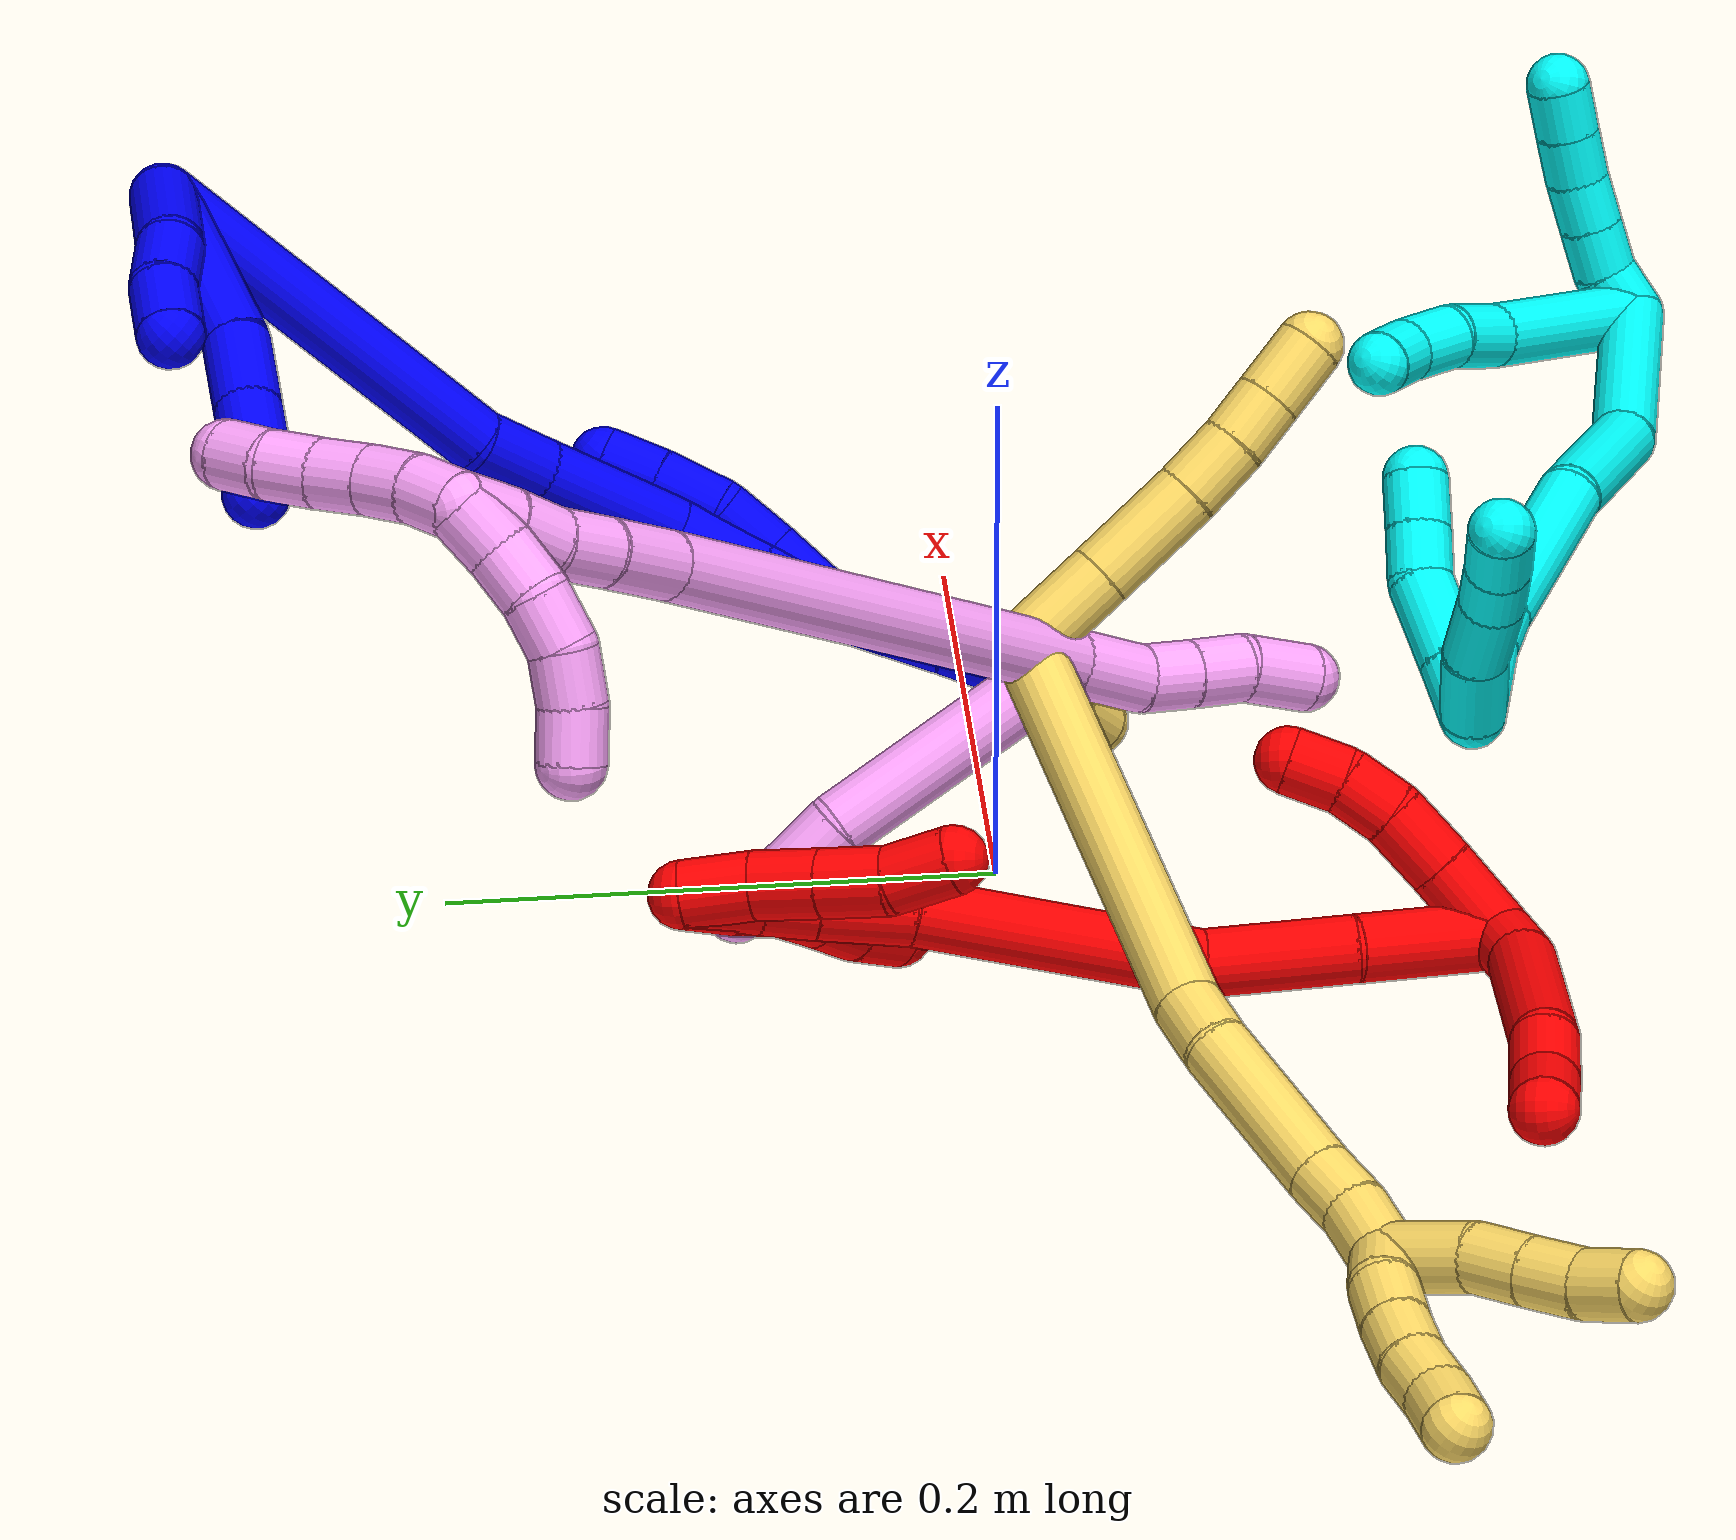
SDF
<sdf version="1.7">
 <world name="default">
  <plugin name="TubeGeneratorPlugin" filename="libtube_generator_plugin.so"/>
  <model name="photoneo_s_sensor">
   <static>1</static>
   <pose>0 0 2 1.57079 1.57079 3.14159</pose>
   <link name="link">
    <inertial><mass>0.1</mass></inertial>
    <sensor name="sensor" type="depth">
     <update_rate>30</update_rate>
     <camera>
      <horizontal_fov>1.22</horizontal_fov>
      <image><width>1920</width><height>1200</height><format>B8G8R8</format></image>
      <clip><near>0.1</near><far>4</far></clip>
      <depth_camera><output>points</output></depth_camera>
     </camera>
     <plugin name="camera_plugin" filename="libgazebo_ros_depth_camera.so">
      <baseline>0.2</baseline>
      <alwaysOn>1</alwaysOn>
      <updateRate>0.0</updateRate>
      <cameraName>camera_ir</cameraName>
      <imageTopicName>/camera/color/image_raw</imageTopicName>
      <cameraInfoTopicName>/camera/color/camera_info</cameraInfoTopicName>
      <depthImageTopicName>/camera/depth/image_raw</depthImageTopicName>
      <depthImageCameraInfoTopicName>/camera/depth/camera_info</depthImageCameraInfoTopicName>
      <pointCloudTopicName>/camera/depth/points</pointCloudTopicName>
      <frameName>fr_optical</frameName>
      <pointCloudCutoff>0.1</pointCloudCutoff>
      <pointCloudCutoffMax>2.0</pointCloudCutoffMax>
      <distortionK1>0</distortionK1>
      <distortionK2>0</distortionK2>
      <distortionK3>0</distortionK3>
      <distortionT1>0</distortionT1>
      <distortionT2>0</distortionT2>
      <CxPrime>0</CxPrime>
      <Cx>0</Cx>
      <Cy>0</Cy>
      <focalLength>0</focalLength>
      <hackBaseline>0</hackBaseline>
     </plugin>
    </sensor>
   </link>
  </model>
  <gravity>0 0 -9.8</gravity>
  <magnetic_field>6e-06 2.3e-05 -4.2e-05</magnetic_field>
  <atmosphere type="adiabatic"/>
  <physics name="default_physics" default="0" type="ode">
   <max_step_size>0.003</max_step_size>
   <real_time_factor>1</real_time_factor>
   <real_time_update_rate>1000</real_time_update_rate>
   <max_contacts>10000</max_contacts>
   <ode>
    <solver>
     <type>quick</type>
     <iters>100</iters>
     <sor>1.3</sor>
     <use_dynamic_moi_rescaling>0</use_dynamic_moi_rescaling>
    </solver>
    <constraints>
     <contact_max_correcting_vel>0</contact_max_correcting_vel>
     <contact_surface_layer>0.001</contact_surface_layer>
     <cfm>0</cfm>
     <erp>0.2</erp>
    </constraints>
   </ode>
  </physics>
  <scene><ambient>0.4 0.4 0.4 1</ambient><background>0.7 0.7 0.7 1</background><shadows>0</shadows></scene>
  <audio><device>default</device></audio>
  <spherical_coordinates>
   <surface_model>EARTH_WGS84</surface_model>
   <latitude_deg>0</latitude_deg>
   <longitude_deg>0</longitude_deg>
   <elevation>0</elevation>
   <heading_deg>0</heading_deg>
  </spherical_coordinates>
  <model name="bin">
   <static>1</static>
   <link name="bottom">
    <collision name="collision-bottom">
     <pose>0 0 -0.01 0 -0 0</pose>
     <geometry><box><size>0.8 0.6 0.02</size></box></geometry>
     <surface>
      <friction><ode><mu>100</mu><mu2>100</mu2></ode></friction>
      <contact><collide_bitmask>65535</collide_bitmask></contact>
     </surface>
    </collision>
   </link>
   <link name="west_wall">
    <collision name="collision-west_wall">
     <pose>-0.41 0 0.1 0 -0 0</pose>
     <geometry><box><size>0.02 0.6 0.2</size></box></geometry>
     <surface>
      <friction><ode><mu>100</mu><mu2>100</mu2></ode></friction>
      <contact><collide_bitmask>65535</collide_bitmask></contact>
     </surface>
    </collision>
   </link>
   <link name="east_wall">
    <collision name="collision-east_wall">
     <pose>0.41 0 0.1 0 -0 0</pose>
     <geometry><box><size>0.02 0.6 0.2</size></box></geometry>
     <surface>
      <friction><ode><mu>100</mu><mu2>100</mu2></ode></friction>
      <contact><collide_bitmask>65535</collide_bitmask></contact>
     </surface>
    </collision>
   </link>
   <link name="south_wall">
    <collision name="collision-south_wall">
     <pose>0 -0.31 0.1 0 -0 0</pose>
     <geometry><box><size>0.8 0.02 0.2</size></box></geometry>
     <surface>
      <friction><ode><mu>100</mu><mu2>100</mu2></ode></friction>
      <contact><collide_bitmask>65535</collide_bitmask></contact>
     </surface>
    </collision>
   </link>
   <link name="north_wall">
    <collision name="collision-north_wall">
     <pose>0 0.31 0.1 0 -0 0</pose>
     <geometry><box><size>0.8 0.02 0.2</size></box></geometry>
     <surface>
      <friction><ode><mu>100</mu><mu2>100</mu2></ode></friction>
      <contact><collide_bitmask>65535</collide_bitmask></contact>
     </surface>
    </collision>
   </link>
  </model>
  <model name="1">
   <static>0</static>
   <link name="1">
    <collision name="collision-cylinder-e_1_2_8">
     <pose>-0.026594 0.011025 -0.02338 -2.70097 -0.799602 2.1669</pose>
     <geometry><cylinder><radius>0.0125</radius><length>0.074173</length></cylinder></geometry>
     <surface>
      <friction><ode><mu>1.16</mu><mu2>1.16</mu2><slip1>0</slip1><slip2>0</slip2></ode></friction>
      <contact><ode><kp>1e+06</kp><kd>1</kd><max_vel>0</max_vel><min_depth>0.001</min_depth></ode></contact>
     </surface>
    </collision>
    <visual name="visual-cylinder-e_1_2_8">
     <pose>-0.026594 0.011025 -0.02338 -2.70097 -0.799602 2.1669</pose>
     <geometry><cylinder><radius>0.0125</radius><length>0.074173</length></cylinder></geometry>
     <material><ambient>0 0 1 1</ambient></material>
    </visual>
    <collision name="collision-cylinder-e_2_8_9">
     <pose>-0.065282 0.029867 -0.054619 -2.35887 -0.828939 1.63482</pose>
     <geometry><cylinder><radius>0.0125</radius><length>0.032811</length></cylinder></geometry>
     <surface>
      <friction><ode><mu>1.16</mu><mu2>1.16</mu2><slip1>0</slip1><slip2>0</slip2></ode></friction>
      <contact><ode><kp>1e+06</kp><kd>1</kd><max_vel>0</max_vel><min_depth>0.001</min_depth></ode></contact>
     </surface>
    </collision>
    <visual name="visual-cylinder-e_2_8_9">
     <pose>-0.065282 0.029867 -0.054619 -2.35887 -0.828939 1.63482</pose>
     <geometry><cylinder><radius>0.0125</radius><length>0.032811</length></cylinder></geometry>
     <material><ambient>0 0 1 1</ambient></material>
    </visual>
    <collision name="collision-cylinder-e_3_9_10">
     <pose>-0.086001 0.042603 -0.067283 -2.34445 -0.897646 1.70463</pose>
     <geometry><cylinder><radius>0.0125</radius><length>0.022062</length></cylinder></geometry>
     <surface>
      <friction><ode><mu>1.16</mu><mu2>1.16</mu2><slip1>0</slip1><slip2>0</slip2></ode></friction>
      <contact><ode><kp>1e+06</kp><kd>1</kd><max_vel>0</max_vel><min_depth>0.001</min_depth></ode></contact>
     </surface>
    </collision>
    <visual name="visual-cylinder-e_3_9_10">
     <pose>-0.086001 0.042603 -0.067283 -2.34445 -0.897646 1.70463</pose>
     <geometry><cylinder><radius>0.0125</radius><length>0.022062</length></cylinder></geometry>
     <material><ambient>0 0 1 1</ambient></material>
    </visual>
    <collision name="collision-cylinder-e_4_10_6">
     <pose>-0.103034 0.052831 -0.07539 -2.12717 -0.931534 1.47062</pose>
     <geometry><cylinder><radius>0.0125</radius><length>0.020955</length></cylinder></geometry>
     <surface>
      <friction><ode><mu>1.16</mu><mu2>1.16</mu2><slip1>0</slip1><slip2>0</slip2></ode></friction>
      <contact><ode><kp>1e+06</kp><kd>1</kd><max_vel>0</max_vel><min_depth>0.001</min_depth></ode></contact>
     </surface>
    </collision>
    <visual name="visual-cylinder-e_4_10_6">
     <pose>-0.103034 0.052831 -0.07539 -2.12717 -0.931534 1.47062</pose>
     <geometry><cylinder><radius>0.0125</radius><length>0.020955</length></cylinder></geometry>
     <material><ambient>0 0 1 1</ambient></material>
    </visual>
    <collision name="collision-cylinder-e_1_2_11">
     <pose>-0.024099 0.006442 -0.003288 -2.0427 -1.27925 1.76428</pose>
     <geometry><cylinder><radius>0.0125</radius><length>0.050323</length></cylinder></geometry>
     <surface>
      <friction><ode><mu>1.16</mu><mu2>1.16</mu2><slip1>0</slip1><slip2>0</slip2></ode></friction>
      <contact><ode><kp>1e+06</kp><kd>1</kd><max_vel>0</max_vel><min_depth>0.001</min_depth></ode></contact>
     </surface>
    </collision>
    <visual name="visual-cylinder-e_1_2_11">
     <pose>-0.024099 0.006442 -0.003288 -2.0427 -1.27925 1.76428</pose>
     <geometry><cylinder><radius>0.0125</radius><length>0.050323</length></cylinder></geometry>
     <material><ambient>0 0 1 1</ambient></material>
    </visual>
    <collision name="collision-cylinder-e_2_11_12">
     <pose>-0.05859 0.019459 -0.009007 -1.92495 -0.97722 1.30397</pose>
     <geometry><cylinder><radius>0.0125</radius><length>0.02507</length></cylinder></geometry>
     <surface>
      <friction><ode><mu>1.16</mu><mu2>1.16</mu2><slip1>0</slip1><slip2>0</slip2></ode></friction>
      <contact><ode><kp>1e+06</kp><kd>1</kd><max_vel>0</max_vel><min_depth>0.001</min_depth></ode></contact>
     </surface>
    </collision>
    <visual name="visual-cylinder-e_2_11_12">
     <pose>-0.05859 0.019459 -0.009007 -1.92495 -0.97722 1.30397</pose>
     <geometry><cylinder><radius>0.0125</radius><length>0.02507</length></cylinder></geometry>
     <material><ambient>0 0 1 1</ambient></material>
    </visual>
    <collision name="collision-cylinder-e_3_12_5">
     <pose>-0.078939 0.031364 -0.016318 -2.31223 -0.943094 1.71727</pose>
     <geometry><cylinder><radius>0.0125</radius><length>0.024608</length></cylinder></geometry>
     <surface>
      <friction><ode><mu>1.16</mu><mu2>1.16</mu2><slip1>0</slip1><slip2>0</slip2></ode></friction>
      <contact><ode><kp>1e+06</kp><kd>1</kd><max_vel>0</max_vel><min_depth>0.001</min_depth></ode></contact>
     </surface>
    </collision>
    <visual name="visual-cylinder-e_3_12_5">
     <pose>-0.078939 0.031364 -0.016318 -2.31223 -0.943094 1.71727</pose>
     <geometry><cylinder><radius>0.0125</radius><length>0.024608</length></cylinder></geometry>
     <material><ambient>0 0 1 1</ambient></material>
    </visual>
    <collision name="collision-cylinder-e_1_2_13">
     <pose>0.00498 -0.006311 -0.074743 3.05736 0.06629 1.33332</pose>
     <geometry><cylinder><radius>0.0125</radius><length>0.150348</length></cylinder></geometry>
     <surface>
      <friction><ode><mu>1.16</mu><mu2>1.16</mu2><slip1>0</slip1><slip2>0</slip2></ode></friction>
      <contact><ode><kp>1e+06</kp><kd>1</kd><max_vel>0</max_vel><min_depth>0.001</min_depth></ode></contact>
     </surface>
    </collision>
    <visual name="visual-cylinder-e_1_2_13">
     <pose>0.00498 -0.006311 -0.074743 3.05736 0.06629 1.33332</pose>
     <geometry><cylinder><radius>0.0125</radius><length>0.150348</length></cylinder></geometry>
     <material><ambient>0 0 1 1</ambient></material>
    </visual>
    <collision name="collision-cylinder-e_2_13_14">
     <pose>0.01373 -0.016651 -0.162655 2.8446 0.267284 1.4642</pose>
     <geometry><cylinder><radius>0.0125</radius><length>0.028557</length></cylinder></geometry>
     <surface>
      <friction><ode><mu>1.16</mu><mu2>1.16</mu2><slip1>0</slip1><slip2>0</slip2></ode></friction>
      <contact><ode><kp>1e+06</kp><kd>1</kd><max_vel>0</max_vel><min_depth>0.001</min_depth></ode></contact>
     </surface>
    </collision>
    <visual name="visual-cylinder-e_2_13_14">
     <pose>0.01373 -0.016651 -0.162655 2.8446 0.267284 1.4642</pose>
     <geometry><cylinder><radius>0.0125</radius><length>0.028557</length></cylinder></geometry>
     <material><ambient>0 0 1 1</ambient></material>
    </visual>
    <collision name="collision-cylinder-e_3_14_15">
     <pose>0.023221 -0.029502 -0.203232 2.83024 0.196079 1.1196</pose>
     <geometry><cylinder><radius>0.0125</radius><length>0.05871</length></cylinder></geometry>
     <surface>
      <friction><ode><mu>1.16</mu><mu2>1.16</mu2><slip1>0</slip1><slip2>0</slip2></ode></friction>
      <contact><ode><kp>1e+06</kp><kd>1</kd><max_vel>0</max_vel><min_depth>0.001</min_depth></ode></contact>
     </surface>
    </collision>
    <visual name="visual-cylinder-e_3_14_15">
     <pose>0.023221 -0.029502 -0.203232 2.83024 0.196079 1.1196</pose>
     <geometry><cylinder><radius>0.0125</radius><length>0.05871</length></cylinder></geometry>
     <material><ambient>0 0 1 1</ambient></material>
    </visual>
    <collision name="collision-cylinder-e_4_15_16">
     <pose>0.026503 -0.042917 -0.247404 2.87413 -0.139319 -0.956853</pose>
     <geometry><cylinder><radius>0.0125</radius><length>0.035104</length></cylinder></geometry>
     <surface>
      <friction><ode><mu>1.16</mu><mu2>1.16</mu2><slip1>0</slip1><slip2>0</slip2></ode></friction>
      <contact><ode><kp>1e+06</kp><kd>1</kd><max_vel>0</max_vel><min_depth>0.001</min_depth></ode></contact>
     </surface>
    </collision>
    <visual name="visual-cylinder-e_4_15_16">
     <pose>0.026503 -0.042917 -0.247404 2.87413 -0.139319 -0.956853</pose>
     <geometry><cylinder><radius>0.0125</radius><length>0.035104</length></cylinder></geometry>
     <material><ambient>0 0 1 1</ambient></material>
    </visual>
    <collision name="collision-cylinder-e_5_16_1">
     <pose>0.02262 -0.051956 -0.276982 2.80767 -0.106131 -0.610627</pose>
     <geometry><cylinder><radius>0.0125</radius><length>0.027281</length></cylinder></geometry>
     <surface>
      <friction><ode><mu>1.16</mu><mu2>1.16</mu2><slip1>0</slip1><slip2>0</slip2></ode></friction>
      <contact><ode><kp>1e+06</kp><kd>1</kd><max_vel>0</max_vel><min_depth>0.001</min_depth></ode></contact>
     </surface>
    </collision>
    <visual name="visual-cylinder-e_5_16_1">
     <pose>0.02262 -0.051956 -0.276982 2.80767 -0.106131 -0.610627</pose>
     <geometry><cylinder><radius>0.0125</radius><length>0.027281</length></cylinder></geometry>
     <material><ambient>0 0 1 1</ambient></material>
    </visual>
    <collision name="collision-cylinder-e_1_1_17">
     <pose>0.026589 -0.056471 -0.277171 0.005488 0.40506 0.001127</pose>
     <geometry><cylinder><radius>0.0125</radius><length>0.027474</length></cylinder></geometry>
     <surface>
      <friction><ode><mu>1.16</mu><mu2>1.16</mu2><slip1>0</slip1><slip2>0</slip2></ode></friction>
      <contact><ode><kp>1e+06</kp><kd>1</kd><max_vel>0</max_vel><min_depth>0.001</min_depth></ode></contact>
     </surface>
    </collision>
    <visual name="visual-cylinder-e_1_1_17">
     <pose>0.026589 -0.056471 -0.277171 0.005488 0.40506 0.001127</pose>
     <geometry><cylinder><radius>0.0125</radius><length>0.027474</length></cylinder></geometry>
     <material><ambient>0 0 1 1</ambient></material>
    </visual>
    <collision name="collision-cylinder-e_2_17_18">
     <pose>0.033947 -0.055952 -0.252501 -0.048744 0.159941 -0.003907</pose>
     <geometry><cylinder><radius>0.0125</radius><length>0.02443</length></cylinder></geometry>
     <surface>
      <friction><ode><mu>1.16</mu><mu2>1.16</mu2><slip1>0</slip1><slip2>0</slip2></ode></friction>
      <contact><ode><kp>1e+06</kp><kd>1</kd><max_vel>0</max_vel><min_depth>0.001</min_depth></ode></contact>
     </surface>
    </collision>
    <visual name="visual-cylinder-e_2_17_18">
     <pose>0.033947 -0.055952 -0.252501 -0.048744 0.159941 -0.003907</pose>
     <geometry><cylinder><radius>0.0125</radius><length>0.02443</length></cylinder></geometry>
     <material><ambient>0 0 1 1</ambient></material>
    </visual>
    <collision name="collision-cylinder-e_3_18_19">
     <pose>0.04044 -0.05183 -0.228742 -0.293061 0.355845 -0.053067</pose>
     <geometry><cylinder><radius>0.0125</radius><length>0.026108</length></cylinder></geometry>
     <surface>
      <friction><ode><mu>1.16</mu><mu2>1.16</mu2><slip1>0</slip1><slip2>0</slip2></ode></friction>
      <contact><ode><kp>1e+06</kp><kd>1</kd><max_vel>0</max_vel><min_depth>0.001</min_depth></ode></contact>
     </surface>
    </collision>
    <visual name="visual-cylinder-e_3_18_19">
     <pose>0.04044 -0.05183 -0.228742 -0.293061 0.355845 -0.053067</pose>
     <geometry><cylinder><radius>0.0125</radius><length>0.026108</length></cylinder></geometry>
     <material><ambient>0 0 1 1</ambient></material>
    </visual>
    <collision name="collision-cylinder-e_4_19_4">
     <pose>0.048437 -0.044507 -0.2073 -0.371395 0.319069 -0.060436</pose>
     <geometry><cylinder><radius>0.0125</radius><length>0.021988</length></cylinder></geometry>
     <surface>
      <friction><ode><mu>1.16</mu><mu2>1.16</mu2><slip1>0</slip1><slip2>0</slip2></ode></friction>
      <contact><ode><kp>1e+06</kp><kd>1</kd><max_vel>0</max_vel><min_depth>0.001</min_depth></ode></contact>
     </surface>
    </collision>
    <visual name="visual-cylinder-e_4_19_4">
     <pose>0.048437 -0.044507 -0.2073 -0.371395 0.319069 -0.060436</pose>
     <geometry><cylinder><radius>0.0125</radius><length>0.021988</length></cylinder></geometry>
     <material><ambient>0 0 1 1</ambient></material>
    </visual>
    <collision name="collision-cylinder-e_1_1_20">
     <pose>0.010615 -0.066167 -0.310127 2.69378 -0.437875 -1.54761</pose>
     <geometry><cylinder><radius>0.0125</radius><length>0.049809</length></cylinder></geometry>
     <surface>
      <friction><ode><mu>1.16</mu><mu2>1.16</mu2><slip1>0</slip1><slip2>0</slip2></ode></friction>
      <contact><ode><kp>1e+06</kp><kd>1</kd><max_vel>0</max_vel><min_depth>0.001</min_depth></ode></contact>
     </surface>
    </collision>
    <visual name="visual-cylinder-e_1_1_20">
     <pose>0.010615 -0.066167 -0.310127 2.69378 -0.437875 -1.54761</pose>
     <geometry><cylinder><radius>0.0125</radius><length>0.049809</length></cylinder></geometry>
     <material><ambient>0 0 1 1</ambient></material>
    </visual>
    <collision name="collision-cylinder-e_2_20_21">
     <pose>-0.003809 -0.080878 -0.341831 2.73151 -0.302051 -1.26349</pose>
     <geometry><cylinder><radius>0.0125</radius><length>0.025979</length></cylinder></geometry>
     <surface>
      <friction><ode><mu>1.16</mu><mu2>1.16</mu2><slip1>0</slip1><slip2>0</slip2></ode></friction>
      <contact><ode><kp>1e+06</kp><kd>1</kd><max_vel>0</max_vel><min_depth>0.001</min_depth></ode></contact>
     </surface>
    </collision>
    <visual name="visual-cylinder-e_2_20_21">
     <pose>-0.003809 -0.080878 -0.341831 2.73151 -0.302051 -1.26349</pose>
     <geometry><cylinder><radius>0.0125</radius><length>0.025979</length></cylinder></geometry>
     <material><ambient>0 0 1 1</ambient></material>
    </visual>
    <collision name="collision-cylinder-e_3_21_3">
     <pose>-0.013061 -0.091433 -0.36248 2.59751 -0.461305 -1.39945</pose>
     <geometry><cylinder><radius>0.0125</radius><length>0.024212</length></cylinder></geometry>
     <surface>
      <friction><ode><mu>1.16</mu><mu2>1.16</mu2><slip1>0</slip1><slip2>0</slip2></ode></friction>
      <contact><ode><kp>1e+06</kp><kd>1</kd><max_vel>0</max_vel><min_depth>0.001</min_depth></ode></contact>
     </surface>
    </collision>
    <visual name="visual-cylinder-e_3_21_3">
     <pose>-0.013061 -0.091433 -0.36248 2.59751 -0.461305 -1.39945</pose>
     <geometry><cylinder><radius>0.0125</radius><length>0.024212</length></cylinder></geometry>
     <material><ambient>0 0 1 1</ambient></material>
    </visual>
    <collision name="collision-sphere-3">
     <pose>-0.01845 -0.097045 -0.371755 0 -0 0</pose>
     <geometry><sphere><radius>0.0125</radius></sphere></geometry>
     <surface>
      <friction><ode><mu>1.16</mu><mu2>1.16</mu2><slip1>0</slip1><slip2>0</slip2></ode></friction>
      <contact><ode><kp>1e+06</kp><kd>1</kd><max_vel>0</max_vel><min_depth>0.001</min_depth></ode></contact>
     </surface>
    </collision>
    <visual name="visual-sphere-3">
     <pose>-0.01845 -0.097045 -0.371755 0 -0 0</pose>
     <geometry><sphere><radius>0.0125</radius></sphere></geometry>
     <material><ambient>0 0 1 1</ambient></material>
    </visual>
    <collision name="collision-sphere-21">
     <pose>-0.007673 -0.085822 -0.353205 0 -0 0</pose>
     <geometry><sphere><radius>0.0125</radius></sphere></geometry>
     <surface>
      <friction><ode><mu>1.16</mu><mu2>1.16</mu2><slip1>0</slip1><slip2>0</slip2></ode></friction>
      <contact><ode><kp>1e+06</kp><kd>1</kd><max_vel>0</max_vel><min_depth>0.001</min_depth></ode></contact>
     </surface>
    </collision>
    <visual name="visual-sphere-21">
     <pose>-0.007673 -0.085822 -0.353205 0 -0 0</pose>
     <geometry><sphere><radius>0.0125</radius></sphere></geometry>
     <material><ambient>0 0 1 1</ambient></material>
    </visual>
    <collision name="collision-sphere-20">
     <pose>5.5e-05 -0.075934 -0.330458 0 -0 0</pose>
     <geometry><sphere><radius>0.0125</radius></sphere></geometry>
     <surface>
      <friction><ode><mu>1.16</mu><mu2>1.16</mu2><slip1>0</slip1><slip2>0</slip2></ode></friction>
      <contact><ode><kp>1e+06</kp><kd>1</kd><max_vel>0</max_vel><min_depth>0.001</min_depth></ode></contact>
     </surface>
    </collision>
    <visual name="visual-sphere-20">
     <pose>5.5e-05 -0.075934 -0.330458 0 -0 0</pose>
     <geometry><sphere><radius>0.0125</radius></sphere></geometry>
     <material><ambient>0 0 1 1</ambient></material>
    </visual>
    <collision name="collision-sphere-4">
     <pose>0.051885 -0.040718 -0.197572 0 -0 0</pose>
     <geometry><sphere><radius>0.0125</radius></sphere></geometry>
     <surface>
      <friction><ode><mu>1.16</mu><mu2>1.16</mu2><slip1>0</slip1><slip2>0</slip2></ode></friction>
      <contact><ode><kp>1e+06</kp><kd>1</kd><max_vel>0</max_vel><min_depth>0.001</min_depth></ode></contact>
     </surface>
    </collision>
    <visual name="visual-sphere-4">
     <pose>0.051885 -0.040718 -0.197572 0 -0 0</pose>
     <geometry><sphere><radius>0.0125</radius></sphere></geometry>
     <material><ambient>0 0 1 1</ambient></material>
    </visual>
    <collision name="collision-sphere-11">
     <pose>-0.048199 0.012883 -0.006575 0 -0 0</pose>
     <geometry><sphere><radius>0.0125</radius></sphere></geometry>
     <surface>
      <friction><ode><mu>1.16</mu><mu2>1.16</mu2><slip1>0</slip1><slip2>0</slip2></ode></friction>
      <contact><ode><kp>1e+06</kp><kd>1</kd><max_vel>0</max_vel><min_depth>0.001</min_depth></ode></contact>
     </surface>
    </collision>
    <visual name="visual-sphere-11">
     <pose>-0.048199 0.012883 -0.006575 0 -0 0</pose>
     <geometry><sphere><radius>0.0125</radius></sphere></geometry>
     <material><ambient>0 0 1 1</ambient></material>
    </visual>
    <collision name="collision-sphere-6">
     <pose>-0.111442 0.058139 -0.078691 0 -0 0</pose>
     <geometry><sphere><radius>0.0125</radius></sphere></geometry>
     <surface>
      <friction><ode><mu>1.16</mu><mu2>1.16</mu2><slip1>0</slip1><slip2>0</slip2></ode></friction>
      <contact><ode><kp>1e+06</kp><kd>1</kd><max_vel>0</max_vel><min_depth>0.001</min_depth></ode></contact>
     </surface>
    </collision>
    <visual name="visual-sphere-6">
     <pose>-0.111442 0.058139 -0.078691 0 -0 0</pose>
     <geometry><sphere><radius>0.0125</radius></sphere></geometry>
     <material><ambient>0 0 1 1</ambient></material>
    </visual>
    <collision name="collision-sphere-10">
     <pose>-0.094626 0.047523 -0.072089 0 -0 0</pose>
     <geometry><sphere><radius>0.0125</radius></sphere></geometry>
     <surface>
      <friction><ode><mu>1.16</mu><mu2>1.16</mu2><slip1>0</slip1><slip2>0</slip2></ode></friction>
      <contact><ode><kp>1e+06</kp><kd>1</kd><max_vel>0</max_vel><min_depth>0.001</min_depth></ode></contact>
     </surface>
    </collision>
    <visual name="visual-sphere-10">
     <pose>-0.094626 0.047523 -0.072089 0 -0 0</pose>
     <geometry><sphere><radius>0.0125</radius></sphere></geometry>
     <material><ambient>0 0 1 1</ambient></material>
    </visual>
    <collision name="collision-sphere-9">
     <pose>-0.077377 0.037683 -0.062478 0 -0 0</pose>
     <geometry><sphere><radius>0.0125</radius></sphere></geometry>
     <surface>
      <friction><ode><mu>1.16</mu><mu2>1.16</mu2><slip1>0</slip1><slip2>0</slip2></ode></friction>
      <contact><ode><kp>1e+06</kp><kd>1</kd><max_vel>0</max_vel><min_depth>0.001</min_depth></ode></contact>
     </surface>
    </collision>
    <visual name="visual-sphere-9">
     <pose>-0.077377 0.037683 -0.062478 0 -0 0</pose>
     <geometry><sphere><radius>0.0125</radius></sphere></geometry>
     <material><ambient>0 0 1 1</ambient></material>
    </visual>
    <collision name="collision-sphere-2">
     <geometry><sphere><radius>0.0125</radius></sphere></geometry>
     <surface>
      <friction><ode><mu>1.16</mu><mu2>1.16</mu2><slip1>0</slip1><slip2>0</slip2></ode></friction>
      <contact><ode><kp>1e+06</kp><kd>1</kd><max_vel>0</max_vel><min_depth>0.001</min_depth></ode></contact>
     </surface>
    </collision>
    <visual name="visual-sphere-2">
     <geometry><sphere><radius>0.0125</radius></sphere></geometry>
     <material><ambient>0 0 1 1</ambient></material>
    </visual>
    <collision name="collision-sphere-19">
     <pose>0.044988 -0.048295 -0.217027 0 -0 0</pose>
     <geometry><sphere><radius>0.0125</radius></sphere></geometry>
     <surface>
      <friction><ode><mu>1.16</mu><mu2>1.16</mu2><slip1>0</slip1><slip2>0</slip2></ode></friction>
      <contact><ode><kp>1e+06</kp><kd>1</kd><max_vel>0</max_vel><min_depth>0.001</min_depth></ode></contact>
     </surface>
    </collision>
    <visual name="visual-sphere-19">
     <pose>0.044988 -0.048295 -0.217027 0 -0 0</pose>
     <geometry><sphere><radius>0.0125</radius></sphere></geometry>
     <material><ambient>0 0 1 1</ambient></material>
    </visual>
    <collision name="collision-sphere-8">
     <pose>-0.053188 0.02205 -0.04676 0 -0 0</pose>
     <geometry><sphere><radius>0.0125</radius></sphere></geometry>
     <surface>
      <friction><ode><mu>1.16</mu><mu2>1.16</mu2><slip1>0</slip1><slip2>0</slip2></ode></friction>
      <contact><ode><kp>1e+06</kp><kd>1</kd><max_vel>0</max_vel><min_depth>0.001</min_depth></ode></contact>
     </surface>
    </collision>
    <visual name="visual-sphere-8">
     <pose>-0.053188 0.02205 -0.04676 0 -0 0</pose>
     <geometry><sphere><radius>0.0125</radius></sphere></geometry>
     <material><ambient>0 0 1 1</ambient></material>
    </visual>
    <collision name="collision-sphere-12">
     <pose>-0.06898 0.026035 -0.011438 0 -0 0</pose>
     <geometry><sphere><radius>0.0125</radius></sphere></geometry>
     <surface>
      <friction><ode><mu>1.16</mu><mu2>1.16</mu2><slip1>0</slip1><slip2>0</slip2></ode></friction>
      <contact><ode><kp>1e+06</kp><kd>1</kd><max_vel>0</max_vel><min_depth>0.001</min_depth></ode></contact>
     </surface>
    </collision>
    <visual name="visual-sphere-12">
     <pose>-0.06898 0.026035 -0.011438 0 -0 0</pose>
     <geometry><sphere><radius>0.0125</radius></sphere></geometry>
     <material><ambient>0 0 1 1</ambient></material>
    </visual>
    <collision name="collision-sphere-5">
     <pose>-0.088897 0.036694 -0.021198 0 -0 0</pose>
     <geometry><sphere><radius>0.0125</radius></sphere></geometry>
     <surface>
      <friction><ode><mu>1.16</mu><mu2>1.16</mu2><slip1>0</slip1><slip2>0</slip2></ode></friction>
      <contact><ode><kp>1e+06</kp><kd>1</kd><max_vel>0</max_vel><min_depth>0.001</min_depth></ode></contact>
     </surface>
    </collision>
    <visual name="visual-sphere-5">
     <pose>-0.088897 0.036694 -0.021198 0 -0 0</pose>
     <geometry><sphere><radius>0.0125</radius></sphere></geometry>
     <material><ambient>0 0 1 1</ambient></material>
    </visual>
    <collision name="collision-sphere-13">
     <pose>0.009959 -0.012621 -0.149486 0 -0 0</pose>
     <geometry><sphere><radius>0.0125</radius></sphere></geometry>
     <surface>
      <friction><ode><mu>1.16</mu><mu2>1.16</mu2><slip1>0</slip1><slip2>0</slip2></ode></friction>
      <contact><ode><kp>1e+06</kp><kd>1</kd><max_vel>0</max_vel><min_depth>0.001</min_depth></ode></contact>
     </surface>
    </collision>
    <visual name="visual-sphere-13">
     <pose>0.009959 -0.012621 -0.149486 0 -0 0</pose>
     <geometry><sphere><radius>0.0125</radius></sphere></geometry>
     <material><ambient>0 0 1 1</ambient></material>
    </visual>
    <collision name="collision-sphere-14">
     <pose>0.017502 -0.020682 -0.175824 0 -0 0</pose>
     <geometry><sphere><radius>0.0125</radius></sphere></geometry>
     <surface>
      <friction><ode><mu>1.16</mu><mu2>1.16</mu2><slip1>0</slip1><slip2>0</slip2></ode></friction>
      <contact><ode><kp>1e+06</kp><kd>1</kd><max_vel>0</max_vel><min_depth>0.001</min_depth></ode></contact>
     </surface>
    </collision>
    <visual name="visual-sphere-14">
     <pose>0.017502 -0.020682 -0.175824 0 -0 0</pose>
     <geometry><sphere><radius>0.0125</radius></sphere></geometry>
     <material><ambient>0 0 1 1</ambient></material>
    </visual>
    <collision name="collision-sphere-15">
     <pose>0.02894 -0.038323 -0.23064 0 -0 0</pose>
     <geometry><sphere><radius>0.0125</radius></sphere></geometry>
     <surface>
      <friction><ode><mu>1.16</mu><mu2>1.16</mu2><slip1>0</slip1><slip2>0</slip2></ode></friction>
      <contact><ode><kp>1e+06</kp><kd>1</kd><max_vel>0</max_vel><min_depth>0.001</min_depth></ode></contact>
     </surface>
    </collision>
    <visual name="visual-sphere-15">
     <pose>0.02894 -0.038323 -0.23064 0 -0 0</pose>
     <geometry><sphere><radius>0.0125</radius></sphere></geometry>
     <material><ambient>0 0 1 1</ambient></material>
    </visual>
    <collision name="collision-sphere-16">
     <pose>0.024065 -0.04751 -0.264168 0 -0 0</pose>
     <geometry><sphere><radius>0.0125</radius></sphere></geometry>
     <surface>
      <friction><ode><mu>1.16</mu><mu2>1.16</mu2><slip1>0</slip1><slip2>0</slip2></ode></friction>
      <contact><ode><kp>1e+06</kp><kd>1</kd><max_vel>0</max_vel><min_depth>0.001</min_depth></ode></contact>
     </surface>
    </collision>
    <visual name="visual-sphere-16">
     <pose>0.024065 -0.04751 -0.264168 0 -0 0</pose>
     <geometry><sphere><radius>0.0125</radius></sphere></geometry>
     <material><ambient>0 0 1 1</ambient></material>
    </visual>
    <collision name="collision-sphere-1">
     <pose>0.021175 -0.056401 -0.289796 0 -0 0</pose>
     <geometry><sphere><radius>0.0125</radius></sphere></geometry>
     <surface>
      <friction><ode><mu>1.16</mu><mu2>1.16</mu2><slip1>0</slip1><slip2>0</slip2></ode></friction>
      <contact><ode><kp>1e+06</kp><kd>1</kd><max_vel>0</max_vel><min_depth>0.001</min_depth></ode></contact>
     </surface>
    </collision>
    <visual name="visual-sphere-1">
     <pose>0.021175 -0.056401 -0.289796 0 -0 0</pose>
     <geometry><sphere><radius>0.0125</radius></sphere></geometry>
     <material><ambient>0 0 1 1</ambient></material>
    </visual>
    <collision name="collision-sphere-18">
     <pose>0.035893 -0.055365 -0.240456 0 -0 0</pose>
     <geometry><sphere><radius>0.0125</radius></sphere></geometry>
     <surface>
      <friction><ode><mu>1.16</mu><mu2>1.16</mu2><slip1>0</slip1><slip2>0</slip2></ode></friction>
      <contact><ode><kp>1e+06</kp><kd>1</kd><max_vel>0</max_vel><min_depth>0.001</min_depth></ode></contact>
     </surface>
    </collision>
    <visual name="visual-sphere-18">
     <pose>0.035893 -0.055365 -0.240456 0 -0 0</pose>
     <geometry><sphere><radius>0.0125</radius></sphere></geometry>
     <material><ambient>0 0 1 1</ambient></material>
    </visual>
    <collision name="collision-sphere-17">
     <pose>0.032002 -0.05654 -0.264546 0 -0 0</pose>
     <geometry><sphere><radius>0.0125</radius></sphere></geometry>
     <surface>
      <friction><ode><mu>1.16</mu><mu2>1.16</mu2><slip1>0</slip1><slip2>0</slip2></ode></friction>
      <contact><ode><kp>1e+06</kp><kd>1</kd><max_vel>0</max_vel><min_depth>0.001</min_depth></ode></contact>
     </surface>
    </collision>
    <visual name="visual-sphere-17">
     <pose>0.032002 -0.05654 -0.264546 0 -0 0</pose>
     <geometry><sphere><radius>0.0125</radius></sphere></geometry>
     <material><ambient>0 0 1 1</ambient></material>
    </visual>
    <inertial>
     <pose>-0.006599 -0.018017 -0.145141 0 -0 0</pose>
     <mass>0.75</mass>
     <inertia>
      <ixx>0.000373</ixx>
      <ixy>0</ixy>
      <ixz>0</ixz>
      <iyy>0.000293</iyy>
      <iyz>0</iyz>
      <izz>1.8e-05</izz>
     </inertia>
    </inertial>
   </link>
   <pose>0.171401 0.288261 0.200804 -0.713594 0.436603 0.13827</pose>
  </model>
  <model name="2">
   <static>0</static>
   <link name="2">
    <collision name="collision-cylinder-e_1_2_8">
     <pose>-0.008782 0.004555 0.00616 -0.636702 -0.853503 0.297485</pose>
     <geometry><cylinder><radius>0.0125</radius><length>0.023308</length></cylinder></geometry>
     <surface>
      <friction><ode><mu>1.16</mu><mu2>1.16</mu2><slip1>0</slip1><slip2>0</slip2></ode></friction>
      <contact><ode><kp>1e+06</kp><kd>1</kd><max_vel>0</max_vel><min_depth>0.001</min_depth></ode></contact>
     </surface>
    </collision>
    <visual name="visual-cylinder-e_1_2_8">
     <pose>-0.008782 0.004555 0.00616 -0.636702 -0.853503 0.297485</pose>
     <geometry><cylinder><radius>0.0125</radius><length>0.023308</length></cylinder></geometry>
     <material><ambient>1 0 0 1</ambient></material>
    </visual>
    <collision name="collision-cylinder-e_2_8_9">
     <pose>-0.048369 0.030845 0.024528 -1.05902 -0.890421 0.544649</pose>
     <geometry><cylinder><radius>0.0125</radius><length>0.079257</length></cylinder></geometry>
     <surface>
      <friction><ode><mu>1.16</mu><mu2>1.16</mu2><slip1>0</slip1><slip2>0</slip2></ode></friction>
      <contact><ode><kp>1e+06</kp><kd>1</kd><max_vel>0</max_vel><min_depth>0.001</min_depth></ode></contact>
     </surface>
    </collision>
    <visual name="visual-cylinder-e_2_8_9">
     <pose>-0.048369 0.030845 0.024528 -1.05902 -0.890421 0.544649</pose>
     <geometry><cylinder><radius>0.0125</radius><length>0.079257</length></cylinder></geometry>
     <material><ambient>1 0 0 1</ambient></material>
    </visual>
    <collision name="collision-cylinder-e_3_9_10">
     <pose>-0.089882 0.055957 0.038657 -1.05355 -1.22281 0.774261</pose>
     <geometry><cylinder><radius>0.0125</radius><length>0.022783</length></cylinder></geometry>
     <surface>
      <friction><ode><mu>1.16</mu><mu2>1.16</mu2><slip1>0</slip1><slip2>0</slip2></ode></friction>
      <contact><ode><kp>1e+06</kp><kd>1</kd><max_vel>0</max_vel><min_depth>0.001</min_depth></ode></contact>
     </surface>
    </collision>
    <visual name="visual-cylinder-e_3_9_10">
     <pose>-0.089882 0.055957 0.038657 -1.05355 -1.22281 0.774261</pose>
     <geometry><cylinder><radius>0.0125</radius><length>0.022783</length></cylinder></geometry>
     <material><ambient>1 0 0 1</ambient></material>
    </visual>
    <collision name="collision-cylinder-e_4_10_6">
     <pose>-0.11052 0.066214 0.043026 -1.22907 -0.936611 0.685726</pose>
     <geometry><cylinder><radius>0.0125</radius><length>0.024653</length></cylinder></geometry>
     <surface>
      <friction><ode><mu>1.16</mu><mu2>1.16</mu2><slip1>0</slip1><slip2>0</slip2></ode></friction>
      <contact><ode><kp>1e+06</kp><kd>1</kd><max_vel>0</max_vel><min_depth>0.001</min_depth></ode></contact>
     </surface>
    </collision>
    <visual name="visual-cylinder-e_4_10_6">
     <pose>-0.11052 0.066214 0.043026 -1.22907 -0.936611 0.685726</pose>
     <geometry><cylinder><radius>0.0125</radius><length>0.024653</length></cylinder></geometry>
     <material><ambient>1 0 0 1</ambient></material>
    </visual>
    <collision name="collision-cylinder-e_1_2_11">
     <pose>0.008349 0.010169 -0.00946 -2.3201 0.541243 -1.13437</pose>
     <geometry><cylinder><radius>0.0125</radius><length>0.03241</length></cylinder></geometry>
     <surface>
      <friction><ode><mu>1.16</mu><mu2>1.16</mu2><slip1>0</slip1><slip2>0</slip2></ode></friction>
      <contact><ode><kp>1e+06</kp><kd>1</kd><max_vel>0</max_vel><min_depth>0.001</min_depth></ode></contact>
     </surface>
    </collision>
    <visual name="visual-cylinder-e_1_2_11">
     <pose>0.008349 0.010169 -0.00946 -2.3201 0.541243 -1.13437</pose>
     <geometry><cylinder><radius>0.0125</radius><length>0.03241</length></cylinder></geometry>
     <material><ambient>1 0 0 1</ambient></material>
    </visual>
    <collision name="collision-cylinder-e_2_11_12">
     <pose>0.023035 0.02809 -0.02674 -2.3605 0.52224 -1.15145</pose>
     <geometry><cylinder><radius>0.0125</radius><length>0.025411</length></cylinder></geometry>
     <surface>
      <friction><ode><mu>1.16</mu><mu2>1.16</mu2><slip1>0</slip1><slip2>0</slip2></ode></friction>
      <contact><ode><kp>1e+06</kp><kd>1</kd><max_vel>0</max_vel><min_depth>0.001</min_depth></ode></contact>
     </surface>
    </collision>
    <visual name="visual-cylinder-e_2_11_12">
     <pose>0.023035 0.02809 -0.02674 -2.3605 0.52224 -1.15145</pose>
     <geometry><cylinder><radius>0.0125</radius><length>0.025411</length></cylinder></geometry>
     <material><ambient>1 0 0 1</ambient></material>
    </visual>
    <collision name="collision-cylinder-e_3_12_13">
     <pose>0.033273 0.041221 -0.042633 -2.55399 0.382257 -1.13793</pose>
     <geometry><cylinder><radius>0.0125</radius><length>0.020909</length></cylinder></geometry>
     <surface>
      <friction><ode><mu>1.16</mu><mu2>1.16</mu2><slip1>0</slip1><slip2>0</slip2></ode></friction>
      <contact><ode><kp>1e+06</kp><kd>1</kd><max_vel>0</max_vel><min_depth>0.001</min_depth></ode></contact>
     </surface>
    </collision>
    <visual name="visual-cylinder-e_3_12_13">
     <pose>0.033273 0.041221 -0.042633 -2.55399 0.382257 -1.13793</pose>
     <geometry><cylinder><radius>0.0125</radius><length>0.020909</length></cylinder></geometry>
     <material><ambient>1 0 0 1</ambient></material>
    </visual>
    <collision name="collision-cylinder-e_4_13_5">
     <pose>0.039003 0.050951 -0.060236 -2.71316 0.173012 -0.758643</pose>
     <geometry><cylinder><radius>0.0125</radius><length>0.02127</length></cylinder></geometry>
     <surface>
      <friction><ode><mu>1.16</mu><mu2>1.16</mu2><slip1>0</slip1><slip2>0</slip2></ode></friction>
      <contact><ode><kp>1e+06</kp><kd>1</kd><max_vel>0</max_vel><min_depth>0.001</min_depth></ode></contact>
     </surface>
    </collision>
    <visual name="visual-cylinder-e_4_13_5">
     <pose>0.039003 0.050951 -0.060236 -2.71316 0.173012 -0.758643</pose>
     <geometry><cylinder><radius>0.0125</radius><length>0.02127</length></cylinder></geometry>
     <material><ambient>1 0 0 1</ambient></material>
    </visual>
    <collision name="collision-cylinder-e_1_2_14">
     <pose>-0.00947 0.011233 -0.02277 -2.68328 -0.357016 1.31678</pose>
     <geometry><cylinder><radius>0.0125</radius><length>0.054197</length></cylinder></geometry>
     <surface>
      <friction><ode><mu>1.16</mu><mu2>1.16</mu2><slip1>0</slip1><slip2>0</slip2></ode></friction>
      <contact><ode><kp>1e+06</kp><kd>1</kd><max_vel>0</max_vel><min_depth>0.001</min_depth></ode></contact>
     </surface>
    </collision>
    <visual name="visual-cylinder-e_1_2_14">
     <pose>-0.00947 0.011233 -0.02277 -2.68328 -0.357016 1.31678</pose>
     <geometry><cylinder><radius>0.0125</radius><length>0.054197</length></cylinder></geometry>
     <material><ambient>1 0 0 1</ambient></material>
    </visual>
    <collision name="collision-cylinder-e_2_14_15">
     <pose>-0.026351 0.030301 -0.071216 -2.84546 -0.269328 1.47481</pose>
     <geometry><cylinder><radius>0.0125</radius><length>0.055698</length></cylinder></geometry>
     <surface>
      <friction><ode><mu>1.16</mu><mu2>1.16</mu2><slip1>0</slip1><slip2>0</slip2></ode></friction>
      <contact><ode><kp>1e+06</kp><kd>1</kd><max_vel>0</max_vel><min_depth>0.001</min_depth></ode></contact>
     </surface>
    </collision>
    <visual name="visual-cylinder-e_2_14_15">
     <pose>-0.026351 0.030301 -0.071216 -2.84546 -0.269328 1.47481</pose>
     <geometry><cylinder><radius>0.0125</radius><length>0.055698</length></cylinder></geometry>
     <material><ambient>1 0 0 1</ambient></material>
    </visual>
    <collision name="collision-cylinder-e_3_15_16">
     <pose>-0.039464 0.066185 -0.141917 -2.58444 -0.107087 0.37047</pose>
     <geometry><cylinder><radius>0.0125</radius><length>0.106706</length></cylinder></geometry>
     <surface>
      <friction><ode><mu>1.16</mu><mu2>1.16</mu2><slip1>0</slip1><slip2>0</slip2></ode></friction>
      <contact><ode><kp>1e+06</kp><kd>1</kd><max_vel>0</max_vel><min_depth>0.001</min_depth></ode></contact>
     </surface>
    </collision>
    <visual name="visual-cylinder-e_3_15_16">
     <pose>-0.039464 0.066185 -0.141917 -2.58444 -0.107087 0.37047</pose>
     <geometry><cylinder><radius>0.0125</radius><length>0.106706</length></cylinder></geometry>
     <material><ambient>1 0 0 1</ambient></material>
    </visual>
    <collision name="collision-cylinder-e_4_16_17">
     <pose>-0.047831 0.101135 -0.202348 -2.72053 -0.156578 0.703658</pose>
     <geometry><cylinder><radius>0.0125</radius><length>0.034179</length></cylinder></geometry>
     <surface>
      <friction><ode><mu>1.16</mu><mu2>1.16</mu2><slip1>0</slip1><slip2>0</slip2></ode></friction>
      <contact><ode><kp>1e+06</kp><kd>1</kd><max_vel>0</max_vel><min_depth>0.001</min_depth></ode></contact>
     </surface>
    </collision>
    <visual name="visual-cylinder-e_4_16_17">
     <pose>-0.047831 0.101135 -0.202348 -2.72053 -0.156578 0.703658</pose>
     <geometry><cylinder><radius>0.0125</radius><length>0.034179</length></cylinder></geometry>
     <material><ambient>1 0 0 1</ambient></material>
    </visual>
    <collision name="collision-cylinder-e_5_17_18">
     <pose>-0.051822 0.112199 -0.226903 -2.71441 -0.131175 0.588081</pose>
     <geometry><cylinder><radius>0.0125</radius><length>0.02028</length></cylinder></geometry>
     <surface>
      <friction><ode><mu>1.16</mu><mu2>1.16</mu2><slip1>0</slip1><slip2>0</slip2></ode></friction>
      <contact><ode><kp>1e+06</kp><kd>1</kd><max_vel>0</max_vel><min_depth>0.001</min_depth></ode></contact>
     </surface>
    </collision>
    <visual name="visual-cylinder-e_5_17_18">
     <pose>-0.051822 0.112199 -0.226903 -2.71441 -0.131175 0.588081</pose>
     <geometry><cylinder><radius>0.0125</radius><length>0.02028</length></cylinder></geometry>
     <material><ambient>1 0 0 1</ambient></material>
    </visual>
    <collision name="collision-cylinder-e_6_18_1">
     <pose>-0.056697 0.124137 -0.24773 -2.55432 -0.247745 0.781226</pose>
     <geometry><cylinder><radius>0.0125</radius><length>0.02894</length></cylinder></geometry>
     <surface>
      <friction><ode><mu>1.16</mu><mu2>1.16</mu2><slip1>0</slip1><slip2>0</slip2></ode></friction>
      <contact><ode><kp>1e+06</kp><kd>1</kd><max_vel>0</max_vel><min_depth>0.001</min_depth></ode></contact>
     </surface>
    </collision>
    <visual name="visual-cylinder-e_6_18_1">
     <pose>-0.056697 0.124137 -0.24773 -2.55432 -0.247745 0.781226</pose>
     <geometry><cylinder><radius>0.0125</radius><length>0.02894</length></cylinder></geometry>
     <material><ambient>1 0 0 1</ambient></material>
    </visual>
    <collision name="collision-cylinder-e_1_1_19">
     <pose>-0.058004 0.130894 -0.246813 0.080461 0.175543 0.007084</pose>
     <geometry><cylinder><radius>0.0125</radius><length>0.025666</length></cylinder></geometry>
     <surface>
      <friction><ode><mu>1.16</mu><mu2>1.16</mu2><slip1>0</slip1><slip2>0</slip2></ode></friction>
      <contact><ode><kp>1e+06</kp><kd>1</kd><max_vel>0</max_vel><min_depth>0.001</min_depth></ode></contact>
     </surface>
    </collision>
    <visual name="visual-cylinder-e_1_1_19">
     <pose>-0.058004 0.130894 -0.246813 0.080461 0.175543 0.007084</pose>
     <geometry><cylinder><radius>0.0125</radius><length>0.025666</length></cylinder></geometry>
     <material><ambient>1 0 0 1</ambient></material>
    </visual>
    <collision name="collision-cylinder-e_2_19_20">
     <pose>-0.05574 0.129865 -0.221694 0.001077 0.001803 1e-06</pose>
     <geometry><cylinder><radius>0.0125</radius><length>0.025049</length></cylinder></geometry>
     <surface>
      <friction><ode><mu>1.16</mu><mu2>1.16</mu2><slip1>0</slip1><slip2>0</slip2></ode></friction>
      <contact><ode><kp>1e+06</kp><kd>1</kd><max_vel>0</max_vel><min_depth>0.001</min_depth></ode></contact>
     </surface>
    </collision>
    <visual name="visual-cylinder-e_2_19_20">
     <pose>-0.05574 0.129865 -0.221694 0.001077 0.001803 1e-06</pose>
     <geometry><cylinder><radius>0.0125</radius><length>0.025049</length></cylinder></geometry>
     <material><ambient>1 0 0 1</ambient></material>
    </visual>
    <collision name="collision-cylinder-e_3_20_21">
     <pose>-0.055642 0.129927 -0.196768 -0.006099 0.006106 -1.9e-05</pose>
     <geometry><cylinder><radius>0.0125</radius><length>0.024805</length></cylinder></geometry>
     <surface>
      <friction><ode><mu>1.16</mu><mu2>1.16</mu2><slip1>0</slip1><slip2>0</slip2></ode></friction>
      <contact><ode><kp>1e+06</kp><kd>1</kd><max_vel>0</max_vel><min_depth>0.001</min_depth></ode></contact>
     </surface>
    </collision>
    <visual name="visual-cylinder-e_3_20_21">
     <pose>-0.055642 0.129927 -0.196768 -0.006099 0.006106 -1.9e-05</pose>
     <geometry><cylinder><radius>0.0125</radius><length>0.024805</length></cylinder></geometry>
     <material><ambient>1 0 0 1</ambient></material>
    </visual>
    <collision name="collision-cylinder-e_4_21_4">
     <pose>-0.052781 0.131658 -0.172562 -0.139324 0.229588 -0.01609</pose>
     <geometry><cylinder><radius>0.0125</radius><length>0.024481</length></cylinder></geometry>
     <surface>
      <friction><ode><mu>1.16</mu><mu2>1.16</mu2><slip1>0</slip1><slip2>0</slip2></ode></friction>
      <contact><ode><kp>1e+06</kp><kd>1</kd><max_vel>0</max_vel><min_depth>0.001</min_depth></ode></contact>
     </surface>
    </collision>
    <visual name="visual-cylinder-e_4_21_4">
     <pose>-0.052781 0.131658 -0.172562 -0.139324 0.229588 -0.01609</pose>
     <geometry><cylinder><radius>0.0125</radius><length>0.024481</length></cylinder></geometry>
     <material><ambient>1 0 0 1</ambient></material>
    </visual>
    <collision name="collision-cylinder-e_1_1_22">
     <pose>-0.057733 0.125688 -0.251994 0.698186 0.253931 0.092864</pose>
     <geometry><cylinder><radius>0.0125</radius><length>0.02</length></cylinder></geometry>
     <surface>
      <friction><ode><mu>1.16</mu><mu2>1.16</mu2><slip1>0</slip1><slip2>0</slip2></ode></friction>
      <contact><ode><kp>1e+06</kp><kd>1</kd><max_vel>0</max_vel><min_depth>0.001</min_depth></ode></contact>
     </surface>
    </collision>
    <visual name="visual-cylinder-e_1_1_22">
     <pose>-0.057733 0.125688 -0.251994 0.698186 0.253931 0.092864</pose>
     <geometry><cylinder><radius>0.0125</radius><length>0.02</length></cylinder></geometry>
     <material><ambient>1 0 0 1</ambient></material>
    </visual>
    <collision name="collision-cylinder-e_2_22_23">
     <pose>-0.050917 0.112231 -0.239182 0.929833 0.444934 0.225963</pose>
     <geometry><cylinder><radius>0.0125</radius><length>0.02</length></cylinder></geometry>
     <surface>
      <friction><ode><mu>1.16</mu><mu2>1.16</mu2><slip1>0</slip1><slip2>0</slip2></ode></friction>
      <contact><ode><kp>1e+06</kp><kd>1</kd><max_vel>0</max_vel><min_depth>0.001</min_depth></ode></contact>
     </surface>
    </collision>
    <visual name="visual-cylinder-e_2_22_23">
     <pose>-0.050917 0.112231 -0.239182 0.929833 0.444934 0.225963</pose>
     <geometry><cylinder><radius>0.0125</radius><length>0.02</length></cylinder></geometry>
     <material><ambient>1 0 0 1</ambient></material>
    </visual>
    <collision name="collision-cylinder-e_3_23_24">
     <pose>-0.043625 0.096425 -0.229587 1.11546 0.303443 0.190175</pose>
     <geometry><cylinder><radius>0.0125</radius><length>0.02</length></cylinder></geometry>
     <surface>
      <friction><ode><mu>1.16</mu><mu2>1.16</mu2><slip1>0</slip1><slip2>0</slip2></ode></friction>
      <contact><ode><kp>1e+06</kp><kd>1</kd><max_vel>0</max_vel><min_depth>0.001</min_depth></ode></contact>
     </surface>
    </collision>
    <visual name="visual-cylinder-e_3_23_24">
     <pose>-0.043625 0.096425 -0.229587 1.11546 0.303443 0.190175</pose>
     <geometry><cylinder><radius>0.0125</radius><length>0.02</length></cylinder></geometry>
     <material><ambient>1 0 0 1</ambient></material>
    </visual>
    <collision name="collision-cylinder-e_4_24_25">
     <pose>-0.037913 0.079167 -0.221255 1.12653 0.275897 0.174897</pose>
     <geometry><cylinder><radius>0.0125</radius><length>0.02</length></cylinder></geometry>
     <surface>
      <friction><ode><mu>1.16</mu><mu2>1.16</mu2><slip1>0</slip1><slip2>0</slip2></ode></friction>
      <contact><ode><kp>1e+06</kp><kd>1</kd><max_vel>0</max_vel><min_depth>0.001</min_depth></ode></contact>
     </surface>
    </collision>
    <visual name="visual-cylinder-e_4_24_25">
     <pose>-0.037913 0.079167 -0.221255 1.12653 0.275897 0.174897</pose>
     <geometry><cylinder><radius>0.0125</radius><length>0.02</length></cylinder></geometry>
     <material><ambient>1 0 0 1</ambient></material>
    </visual>
    <collision name="collision-cylinder-e_5_25_3">
     <pose>-0.031732 0.062978 -0.211482 0.926266 0.352914 0.177614</pose>
     <geometry><cylinder><radius>0.0125</radius><length>0.02</length></cylinder></geometry>
     <surface>
      <friction><ode><mu>1.16</mu><mu2>1.16</mu2><slip1>0</slip1><slip2>0</slip2></ode></friction>
      <contact><ode><kp>1e+06</kp><kd>1</kd><max_vel>0</max_vel><min_depth>0.001</min_depth></ode></contact>
     </surface>
    </collision>
    <visual name="visual-cylinder-e_5_25_3">
     <pose>-0.031732 0.062978 -0.211482 0.926266 0.352914 0.177614</pose>
     <geometry><cylinder><radius>0.0125</radius><length>0.02</length></cylinder></geometry>
     <material><ambient>1 0 0 1</ambient></material>
    </visual>
    <collision name="collision-sphere-3">
     <pose>-0.028276 0.055476 -0.205844 0 -0 0</pose>
     <geometry><sphere><radius>0.0125</radius></sphere></geometry>
     <surface>
      <friction><ode><mu>1.16</mu><mu2>1.16</mu2><slip1>0</slip1><slip2>0</slip2></ode></friction>
      <contact><ode><kp>1e+06</kp><kd>1</kd><max_vel>0</max_vel><min_depth>0.001</min_depth></ode></contact>
     </surface>
    </collision>
    <visual name="visual-sphere-3">
     <pose>-0.028276 0.055476 -0.205844 0 -0 0</pose>
     <geometry><sphere><radius>0.0125</radius></sphere></geometry>
     <material><ambient>1 0 0 1</ambient></material>
    </visual>
    <collision name="collision-sphere-25">
     <pose>-0.035189 0.070479 -0.21712 0 -0 0</pose>
     <geometry><sphere><radius>0.0125</radius></sphere></geometry>
     <surface>
      <friction><ode><mu>1.16</mu><mu2>1.16</mu2><slip1>0</slip1><slip2>0</slip2></ode></friction>
      <contact><ode><kp>1e+06</kp><kd>1</kd><max_vel>0</max_vel><min_depth>0.001</min_depth></ode></contact>
     </surface>
    </collision>
    <visual name="visual-sphere-25">
     <pose>-0.035189 0.070479 -0.21712 0 -0 0</pose>
     <geometry><sphere><radius>0.0125</radius></sphere></geometry>
     <material><ambient>1 0 0 1</ambient></material>
    </visual>
    <collision name="collision-sphere-24">
     <pose>-0.040637 0.087854 -0.225391 0 -0 0</pose>
     <geometry><sphere><radius>0.0125</radius></sphere></geometry>
     <surface>
      <friction><ode><mu>1.16</mu><mu2>1.16</mu2><slip1>0</slip1><slip2>0</slip2></ode></friction>
      <contact><ode><kp>1e+06</kp><kd>1</kd><max_vel>0</max_vel><min_depth>0.001</min_depth></ode></contact>
     </surface>
    </collision>
    <visual name="visual-sphere-24">
     <pose>-0.040637 0.087854 -0.225391 0 -0 0</pose>
     <geometry><sphere><radius>0.0125</radius></sphere></geometry>
     <material><ambient>1 0 0 1</ambient></material>
    </visual>
    <collision name="collision-sphere-23">
     <pose>-0.046613 0.104996 -0.233784 0 -0 0</pose>
     <geometry><sphere><radius>0.0125</radius></sphere></geometry>
     <surface>
      <friction><ode><mu>1.16</mu><mu2>1.16</mu2><slip1>0</slip1><slip2>0</slip2></ode></friction>
      <contact><ode><kp>1e+06</kp><kd>1</kd><max_vel>0</max_vel><min_depth>0.001</min_depth></ode></contact>
     </surface>
    </collision>
    <visual name="visual-sphere-23">
     <pose>-0.046613 0.104996 -0.233784 0 -0 0</pose>
     <geometry><sphere><radius>0.0125</radius></sphere></geometry>
     <material><ambient>1 0 0 1</ambient></material>
    </visual>
    <collision name="collision-sphere-22">
     <pose>-0.055221 0.119466 -0.244579 0 -0 0</pose>
     <geometry><sphere><radius>0.0125</radius></sphere></geometry>
     <surface>
      <friction><ode><mu>1.16</mu><mu2>1.16</mu2><slip1>0</slip1><slip2>0</slip2></ode></friction>
      <contact><ode><kp>1e+06</kp><kd>1</kd><max_vel>0</max_vel><min_depth>0.001</min_depth></ode></contact>
     </surface>
    </collision>
    <visual name="visual-sphere-22">
     <pose>-0.055221 0.119466 -0.244579 0 -0 0</pose>
     <geometry><sphere><radius>0.0125</radius></sphere></geometry>
     <material><ambient>1 0 0 1</ambient></material>
    </visual>
    <collision name="collision-sphere-4">
     <pose>-0.049995 0.133314 -0.160759 0 -0 0</pose>
     <geometry><sphere><radius>0.0125</radius></sphere></geometry>
     <surface>
      <friction><ode><mu>1.16</mu><mu2>1.16</mu2><slip1>0</slip1><slip2>0</slip2></ode></friction>
      <contact><ode><kp>1e+06</kp><kd>1</kd><max_vel>0</max_vel><min_depth>0.001</min_depth></ode></contact>
     </surface>
    </collision>
    <visual name="visual-sphere-4">
     <pose>-0.049995 0.133314 -0.160759 0 -0 0</pose>
     <geometry><sphere><radius>0.0125</radius></sphere></geometry>
     <material><ambient>1 0 0 1</ambient></material>
    </visual>
    <collision name="collision-sphere-21">
     <pose>-0.055566 0.130003 -0.184366 0 -0 0</pose>
     <geometry><sphere><radius>0.0125</radius></sphere></geometry>
     <surface>
      <friction><ode><mu>1.16</mu><mu2>1.16</mu2><slip1>0</slip1><slip2>0</slip2></ode></friction>
      <contact><ode><kp>1e+06</kp><kd>1</kd><max_vel>0</max_vel><min_depth>0.001</min_depth></ode></contact>
     </surface>
    </collision>
    <visual name="visual-sphere-21">
     <pose>-0.055566 0.130003 -0.184366 0 -0 0</pose>
     <geometry><sphere><radius>0.0125</radius></sphere></geometry>
     <material><ambient>1 0 0 1</ambient></material>
    </visual>
    <collision name="collision-sphere-20">
     <pose>-0.055718 0.129852 -0.20917 0 -0 0</pose>
     <geometry><sphere><radius>0.0125</radius></sphere></geometry>
     <surface>
      <friction><ode><mu>1.16</mu><mu2>1.16</mu2><slip1>0</slip1><slip2>0</slip2></ode></friction>
      <contact><ode><kp>1e+06</kp><kd>1</kd><max_vel>0</max_vel><min_depth>0.001</min_depth></ode></contact>
     </surface>
    </collision>
    <visual name="visual-sphere-20">
     <pose>-0.055718 0.129852 -0.20917 0 -0 0</pose>
     <geometry><sphere><radius>0.0125</radius></sphere></geometry>
     <material><ambient>1 0 0 1</ambient></material>
    </visual>
    <collision name="collision-sphere-11">
     <pose>0.016698 0.020338 -0.01892 0 -0 0</pose>
     <geometry><sphere><radius>0.0125</radius></sphere></geometry>
     <surface>
      <friction><ode><mu>1.16</mu><mu2>1.16</mu2><slip1>0</slip1><slip2>0</slip2></ode></friction>
      <contact><ode><kp>1e+06</kp><kd>1</kd><max_vel>0</max_vel><min_depth>0.001</min_depth></ode></contact>
     </surface>
    </collision>
    <visual name="visual-sphere-11">
     <pose>0.016698 0.020338 -0.01892 0 -0 0</pose>
     <geometry><sphere><radius>0.0125</radius></sphere></geometry>
     <material><ambient>1 0 0 1</ambient></material>
    </visual>
    <collision name="collision-sphere-6">
     <pose>-0.12045 0.073096 0.045474 0 -0 0</pose>
     <geometry><sphere><radius>0.0125</radius></sphere></geometry>
     <surface>
      <friction><ode><mu>1.16</mu><mu2>1.16</mu2><slip1>0</slip1><slip2>0</slip2></ode></friction>
      <contact><ode><kp>1e+06</kp><kd>1</kd><max_vel>0</max_vel><min_depth>0.001</min_depth></ode></contact>
     </surface>
    </collision>
    <visual name="visual-sphere-6">
     <pose>-0.12045 0.073096 0.045474 0 -0 0</pose>
     <geometry><sphere><radius>0.0125</radius></sphere></geometry>
     <material><ambient>1 0 0 1</ambient></material>
    </visual>
    <collision name="collision-sphere-10">
     <pose>-0.100591 0.059333 0.040578 0 -0 0</pose>
     <geometry><sphere><radius>0.0125</radius></sphere></geometry>
     <surface>
      <friction><ode><mu>1.16</mu><mu2>1.16</mu2><slip1>0</slip1><slip2>0</slip2></ode></friction>
      <contact><ode><kp>1e+06</kp><kd>1</kd><max_vel>0</max_vel><min_depth>0.001</min_depth></ode></contact>
     </surface>
    </collision>
    <visual name="visual-sphere-10">
     <pose>-0.100591 0.059333 0.040578 0 -0 0</pose>
     <geometry><sphere><radius>0.0125</radius></sphere></geometry>
     <material><ambient>1 0 0 1</ambient></material>
    </visual>
    <collision name="collision-sphere-9">
     <pose>-0.079173 0.05258 0.036737 0 -0 0</pose>
     <geometry><sphere><radius>0.0125</radius></sphere></geometry>
     <surface>
      <friction><ode><mu>1.16</mu><mu2>1.16</mu2><slip1>0</slip1><slip2>0</slip2></ode></friction>
      <contact><ode><kp>1e+06</kp><kd>1</kd><max_vel>0</max_vel><min_depth>0.001</min_depth></ode></contact>
     </surface>
    </collision>
    <visual name="visual-sphere-9">
     <pose>-0.079173 0.05258 0.036737 0 -0 0</pose>
     <geometry><sphere><radius>0.0125</radius></sphere></geometry>
     <material><ambient>1 0 0 1</ambient></material>
    </visual>
    <collision name="collision-sphere-2">
     <geometry><sphere><radius>0.0125</radius></sphere></geometry>
     <surface>
      <friction><ode><mu>1.16</mu><mu2>1.16</mu2><slip1>0</slip1><slip2>0</slip2></ode></friction>
      <contact><ode><kp>1e+06</kp><kd>1</kd><max_vel>0</max_vel><min_depth>0.001</min_depth></ode></contact>
     </surface>
    </collision>
    <visual name="visual-sphere-2">
     <geometry><sphere><radius>0.0125</radius></sphere></geometry>
     <material><ambient>1 0 0 1</ambient></material>
    </visual>
    <collision name="collision-sphere-19">
     <pose>-0.055763 0.129879 -0.234218 0 -0 0</pose>
     <geometry><sphere><radius>0.0125</radius></sphere></geometry>
     <surface>
      <friction><ode><mu>1.16</mu><mu2>1.16</mu2><slip1>0</slip1><slip2>0</slip2></ode></friction>
      <contact><ode><kp>1e+06</kp><kd>1</kd><max_vel>0</max_vel><min_depth>0.001</min_depth></ode></contact>
     </surface>
    </collision>
    <visual name="visual-sphere-19">
     <pose>-0.055763 0.129879 -0.234218 0 -0 0</pose>
     <geometry><sphere><radius>0.0125</radius></sphere></geometry>
     <material><ambient>1 0 0 1</ambient></material>
    </visual>
    <collision name="collision-sphere-8">
     <pose>-0.017564 0.009109 0.012319 0 -0 0</pose>
     <geometry><sphere><radius>0.0125</radius></sphere></geometry>
     <surface>
      <friction><ode><mu>1.16</mu><mu2>1.16</mu2><slip1>0</slip1><slip2>0</slip2></ode></friction>
      <contact><ode><kp>1e+06</kp><kd>1</kd><max_vel>0</max_vel><min_depth>0.001</min_depth></ode></contact>
     </surface>
    </collision>
    <visual name="visual-sphere-8">
     <pose>-0.017564 0.009109 0.012319 0 -0 0</pose>
     <geometry><sphere><radius>0.0125</radius></sphere></geometry>
     <material><ambient>1 0 0 1</ambient></material>
    </visual>
    <collision name="collision-sphere-12">
     <pose>0.029373 0.035843 -0.03456 0 -0 0</pose>
     <geometry><sphere><radius>0.0125</radius></sphere></geometry>
     <surface>
      <friction><ode><mu>1.16</mu><mu2>1.16</mu2><slip1>0</slip1><slip2>0</slip2></ode></friction>
      <contact><ode><kp>1e+06</kp><kd>1</kd><max_vel>0</max_vel><min_depth>0.001</min_depth></ode></contact>
     </surface>
    </collision>
    <visual name="visual-sphere-12">
     <pose>0.029373 0.035843 -0.03456 0 -0 0</pose>
     <geometry><sphere><radius>0.0125</radius></sphere></geometry>
     <material><ambient>1 0 0 1</ambient></material>
    </visual>
    <collision name="collision-sphere-13">
     <pose>0.037172 0.046598 -0.050706 0 -0 0</pose>
     <geometry><sphere><radius>0.0125</radius></sphere></geometry>
     <surface>
      <friction><ode><mu>1.16</mu><mu2>1.16</mu2><slip1>0</slip1><slip2>0</slip2></ode></friction>
      <contact><ode><kp>1e+06</kp><kd>1</kd><max_vel>0</max_vel><min_depth>0.001</min_depth></ode></contact>
     </surface>
    </collision>
    <visual name="visual-sphere-13">
     <pose>0.037172 0.046598 -0.050706 0 -0 0</pose>
     <geometry><sphere><radius>0.0125</radius></sphere></geometry>
     <material><ambient>1 0 0 1</ambient></material>
    </visual>
    <collision name="collision-sphere-5">
     <pose>0.040834 0.055303 -0.069765 0 -0 0</pose>
     <geometry><sphere><radius>0.0125</radius></sphere></geometry>
     <surface>
      <friction><ode><mu>1.16</mu><mu2>1.16</mu2><slip1>0</slip1><slip2>0</slip2></ode></friction>
      <contact><ode><kp>1e+06</kp><kd>1</kd><max_vel>0</max_vel><min_depth>0.001</min_depth></ode></contact>
     </surface>
    </collision>
    <visual name="visual-sphere-5">
     <pose>0.040834 0.055303 -0.069765 0 -0 0</pose>
     <geometry><sphere><radius>0.0125</radius></sphere></geometry>
     <material><ambient>1 0 0 1</ambient></material>
    </visual>
    <collision name="collision-sphere-14">
     <pose>-0.018941 0.022467 -0.045539 0 -0 0</pose>
     <geometry><sphere><radius>0.0125</radius></sphere></geometry>
     <surface>
      <friction><ode><mu>1.16</mu><mu2>1.16</mu2><slip1>0</slip1><slip2>0</slip2></ode></friction>
      <contact><ode><kp>1e+06</kp><kd>1</kd><max_vel>0</max_vel><min_depth>0.001</min_depth></ode></contact>
     </surface>
    </collision>
    <visual name="visual-sphere-14">
     <pose>-0.018941 0.022467 -0.045539 0 -0 0</pose>
     <geometry><sphere><radius>0.0125</radius></sphere></geometry>
     <material><ambient>1 0 0 1</ambient></material>
    </visual>
    <collision name="collision-sphere-15">
     <pose>-0.033761 0.038135 -0.096893 0 -0 0</pose>
     <geometry><sphere><radius>0.0125</radius></sphere></geometry>
     <surface>
      <friction><ode><mu>1.16</mu><mu2>1.16</mu2><slip1>0</slip1><slip2>0</slip2></ode></friction>
      <contact><ode><kp>1e+06</kp><kd>1</kd><max_vel>0</max_vel><min_depth>0.001</min_depth></ode></contact>
     </surface>
    </collision>
    <visual name="visual-sphere-15">
     <pose>-0.033761 0.038135 -0.096893 0 -0 0</pose>
     <geometry><sphere><radius>0.0125</radius></sphere></geometry>
     <material><ambient>1 0 0 1</ambient></material>
    </visual>
    <collision name="collision-sphere-16">
     <pose>-0.045166 0.094235 -0.186942 0 -0 0</pose>
     <geometry><sphere><radius>0.0125</radius></sphere></geometry>
     <surface>
      <friction><ode><mu>1.16</mu><mu2>1.16</mu2><slip1>0</slip1><slip2>0</slip2></ode></friction>
      <contact><ode><kp>1e+06</kp><kd>1</kd><max_vel>0</max_vel><min_depth>0.001</min_depth></ode></contact>
     </surface>
    </collision>
    <visual name="visual-sphere-16">
     <pose>-0.045166 0.094235 -0.186942 0 -0 0</pose>
     <geometry><sphere><radius>0.0125</radius></sphere></geometry>
     <material><ambient>1 0 0 1</ambient></material>
    </visual>
    <collision name="collision-sphere-17">
     <pose>-0.050496 0.108034 -0.217754 0 -0 0</pose>
     <geometry><sphere><radius>0.0125</radius></sphere></geometry>
     <surface>
      <friction><ode><mu>1.16</mu><mu2>1.16</mu2><slip1>0</slip1><slip2>0</slip2></ode></friction>
      <contact><ode><kp>1e+06</kp><kd>1</kd><max_vel>0</max_vel><min_depth>0.001</min_depth></ode></contact>
     </surface>
    </collision>
    <visual name="visual-sphere-17">
     <pose>-0.050496 0.108034 -0.217754 0 -0 0</pose>
     <geometry><sphere><radius>0.0125</radius></sphere></geometry>
     <material><ambient>1 0 0 1</ambient></material>
    </visual>
    <collision name="collision-sphere-18">
     <pose>-0.053149 0.116364 -0.236052 0 -0 0</pose>
     <geometry><sphere><radius>0.0125</radius></sphere></geometry>
     <surface>
      <friction><ode><mu>1.16</mu><mu2>1.16</mu2><slip1>0</slip1><slip2>0</slip2></ode></friction>
      <contact><ode><kp>1e+06</kp><kd>1</kd><max_vel>0</max_vel><min_depth>0.001</min_depth></ode></contact>
     </surface>
    </collision>
    <visual name="visual-sphere-18">
     <pose>-0.053149 0.116364 -0.236052 0 -0 0</pose>
     <geometry><sphere><radius>0.0125</radius></sphere></geometry>
     <material><ambient>1 0 0 1</ambient></material>
    </visual>
    <collision name="collision-sphere-1">
     <pose>-0.060245 0.13191 -0.259408 0 -0 0</pose>
     <geometry><sphere><radius>0.0125</radius></sphere></geometry>
     <surface>
      <friction><ode><mu>1.16</mu><mu2>1.16</mu2><slip1>0</slip1><slip2>0</slip2></ode></friction>
      <contact><ode><kp>1e+06</kp><kd>1</kd><max_vel>0</max_vel><min_depth>0.001</min_depth></ode></contact>
     </surface>
    </collision>
    <visual name="visual-sphere-1">
     <pose>-0.060245 0.13191 -0.259408 0 -0 0</pose>
     <geometry><sphere><radius>0.0125</radius></sphere></geometry>
     <material><ambient>1 0 0 1</ambient></material>
    </visual>
    <inertial>
     <pose>-0.035925 0.066291 -0.109632 0 -0 0</pose>
     <mass>0.75</mass>
     <inertia>
      <ixx>0.000232</ixx>
      <ixy>0</ixy>
      <ixz>0</ixz>
      <iyy>6.2e-05</iyy>
      <iyz>0</iyz>
      <izz>-5.3e-05</izz>
     </inertia>
    </inertial>
   </link>
   <pose>-0.07295 -0.1736 0.012423 1.36157 -0.396646 -0.246259</pose>
  </model>
  <model name="3">
   <static>0</static>
   <link name="3">
    <collision name="collision-cylinder-e_1_2_8">
     <pose>-0.008776 -0.009324 -0.037979 2.90086 -0.220763 -1.48355</pose>
     <geometry><cylinder><radius>0.0125</radius><length>0.08016</length></cylinder></geometry>
     <surface>
      <friction><ode><mu>1.16</mu><mu2>1.16</mu2><slip1>0</slip1><slip2>0</slip2></ode></friction>
      <contact><ode><kp>1e+06</kp><kd>1</kd><max_vel>0</max_vel><min_depth>0.001</min_depth></ode></contact>
     </surface>
    </collision>
    <visual name="visual-cylinder-e_1_2_8">
     <pose>-0.008776 -0.009324 -0.037979 2.90086 -0.220763 -1.48355</pose>
     <geometry><cylinder><radius>0.0125</radius><length>0.08016</length></cylinder></geometry>
     <material><ambient>0.003922 1 0.996078 1</ambient></material>
    </visual>
    <collision name="collision-cylinder-e_2_8_9">
     <pose>-0.019254 -0.020617 -0.088246 2.98267 -0.135834 -1.41387</pose>
     <geometry><cylinder><radius>0.0125</radius><length>0.025119</length></cylinder></geometry>
     <surface>
      <friction><ode><mu>1.16</mu><mu2>1.16</mu2><slip1>0</slip1><slip2>0</slip2></ode></friction>
      <contact><ode><kp>1e+06</kp><kd>1</kd><max_vel>0</max_vel><min_depth>0.001</min_depth></ode></contact>
     </surface>
    </collision>
    <visual name="visual-cylinder-e_2_8_9">
     <pose>-0.019254 -0.020617 -0.088246 2.98267 -0.135834 -1.41387</pose>
     <geometry><cylinder><radius>0.0125</radius><length>0.025119</length></cylinder></geometry>
     <material><ambient>0.003922 1 0.996078 1</ambient></material>
    </visual>
    <collision name="collision-cylinder-e_3_9_10">
     <pose>-0.02482 -0.026413 -0.111176 2.79637 -0.329368 -1.52289</pose>
     <geometry><cylinder><radius>0.0125</radius><length>0.023905</length></cylinder></geometry>
     <surface>
      <friction><ode><mu>1.16</mu><mu2>1.16</mu2><slip1>0</slip1><slip2>0</slip2></ode></friction>
      <contact><ode><kp>1e+06</kp><kd>1</kd><max_vel>0</max_vel><min_depth>0.001</min_depth></ode></contact>
     </surface>
    </collision>
    <visual name="visual-cylinder-e_3_9_10">
     <pose>-0.02482 -0.026413 -0.111176 2.79637 -0.329368 -1.52289</pose>
     <geometry><cylinder><radius>0.0125</radius><length>0.023905</length></cylinder></geometry>
     <material><ambient>0.003922 1 0.996078 1</ambient></material>
    </visual>
    <collision name="collision-cylinder-e_4_10_6">
     <pose>-0.032657 -0.030224 -0.13144 -3.13983 -0.391367 3.13267</pose>
     <geometry><cylinder><radius>0.0125</radius><length>0.020816</length></cylinder></geometry>
     <surface>
      <friction><ode><mu>1.16</mu><mu2>1.16</mu2><slip1>0</slip1><slip2>0</slip2></ode></friction>
      <contact><ode><kp>1e+06</kp><kd>1</kd><max_vel>0</max_vel><min_depth>0.001</min_depth></ode></contact>
     </surface>
    </collision>
    <visual name="visual-cylinder-e_4_10_6">
     <pose>-0.032657 -0.030224 -0.13144 -3.13983 -0.391367 3.13267</pose>
     <geometry><cylinder><radius>0.0125</radius><length>0.020816</length></cylinder></geometry>
     <material><ambient>0.003922 1 0.996078 1</ambient></material>
    </visual>
    <collision name="collision-cylinder-e_1_2_11">
     <pose>0.00811 -0.002723 -0.005178 2.65746 0.945911 2.24244</pose>
     <geometry><cylinder><radius>0.0125</radius><length>0.02</length></cylinder></geometry>
     <surface>
      <friction><ode><mu>1.16</mu><mu2>1.16</mu2><slip1>0</slip1><slip2>0</slip2></ode></friction>
      <contact><ode><kp>1e+06</kp><kd>1</kd><max_vel>0</max_vel><min_depth>0.001</min_depth></ode></contact>
     </surface>
    </collision>
    <visual name="visual-cylinder-e_1_2_11">
     <pose>0.00811 -0.002723 -0.005178 2.65746 0.945911 2.24244</pose>
     <geometry><cylinder><radius>0.0125</radius><length>0.02</length></cylinder></geometry>
     <material><ambient>0.003922 1 0.996078 1</ambient></material>
    </visual>
    <collision name="collision-cylinder-e_2_11_12">
     <pose>0.02479 -0.004983 -0.015489 -3.05162 1.02925 -2.98271</pose>
     <geometry><cylinder><radius>0.0125</radius><length>0.02</length></cylinder></geometry>
     <surface>
      <friction><ode><mu>1.16</mu><mu2>1.16</mu2><slip1>0</slip1><slip2>0</slip2></ode></friction>
      <contact><ode><kp>1e+06</kp><kd>1</kd><max_vel>0</max_vel><min_depth>0.001</min_depth></ode></contact>
     </surface>
    </collision>
    <visual name="visual-cylinder-e_2_11_12">
     <pose>0.02479 -0.004983 -0.015489 -3.05162 1.02925 -2.98271</pose>
     <geometry><cylinder><radius>0.0125</radius><length>0.02</length></cylinder></geometry>
     <material><ambient>0.003922 1 0.996078 1</ambient></material>
    </visual>
    <collision name="collision-cylinder-e_3_12_13">
     <pose>0.041874 -0.00396 -0.025836 -3.03465 1.01891 -2.95056</pose>
     <geometry><cylinder><radius>0.0125</radius><length>0.02</length></cylinder></geometry>
     <surface>
      <friction><ode><mu>1.16</mu><mu2>1.16</mu2><slip1>0</slip1><slip2>0</slip2></ode></friction>
      <contact><ode><kp>1e+06</kp><kd>1</kd><max_vel>0</max_vel><min_depth>0.001</min_depth></ode></contact>
     </surface>
    </collision>
    <visual name="visual-cylinder-e_3_12_13">
     <pose>0.041874 -0.00396 -0.025836 -3.03465 1.01891 -2.95056</pose>
     <geometry><cylinder><radius>0.0125</radius><length>0.02</length></cylinder></geometry>
     <material><ambient>0.003922 1 0.996078 1</ambient></material>
    </visual>
    <collision name="collision-cylinder-e_4_13_14">
     <pose>0.058463 -0.00169 -0.036696 -2.84749 0.939689 -2.57393</pose>
     <geometry><cylinder><radius>0.0125</radius><length>0.02</length></cylinder></geometry>
     <surface>
      <friction><ode><mu>1.16</mu><mu2>1.16</mu2><slip1>0</slip1><slip2>0</slip2></ode></friction>
      <contact><ode><kp>1e+06</kp><kd>1</kd><max_vel>0</max_vel><min_depth>0.001</min_depth></ode></contact>
     </surface>
    </collision>
    <visual name="visual-cylinder-e_4_13_14">
     <pose>0.058463 -0.00169 -0.036696 -2.84749 0.939689 -2.57393</pose>
     <geometry><cylinder><radius>0.0125</radius><length>0.02</length></cylinder></geometry>
     <material><ambient>0.003922 1 0.996078 1</ambient></material>
    </visual>
    <collision name="collision-cylinder-e_5_14_5">
     <pose>0.074674 0.001815 -0.047873 -2.82788 0.950442 -2.54519</pose>
     <geometry><cylinder><radius>0.0125</radius><length>0.02</length></cylinder></geometry>
     <surface>
      <friction><ode><mu>1.16</mu><mu2>1.16</mu2><slip1>0</slip1><slip2>0</slip2></ode></friction>
      <contact><ode><kp>1e+06</kp><kd>1</kd><max_vel>0</max_vel><min_depth>0.001</min_depth></ode></contact>
     </surface>
    </collision>
    <visual name="visual-cylinder-e_5_14_5">
     <pose>0.074674 0.001815 -0.047873 -2.82788 0.950442 -2.54519</pose>
     <geometry><cylinder><radius>0.0125</radius><length>0.02</length></cylinder></geometry>
     <material><ambient>0.003922 1 0.996078 1</ambient></material>
    </visual>
    <collision name="collision-cylinder-e_1_2_15">
     <pose>-0.032061 0.014745 -0.031071 -2.69849 -0.75033 2.1025</pose>
     <geometry><cylinder><radius>0.0125</radius><length>0.094037</length></cylinder></geometry>
     <surface>
      <friction><ode><mu>1.16</mu><mu2>1.16</mu2><slip1>0</slip1><slip2>0</slip2></ode></friction>
      <contact><ode><kp>1e+06</kp><kd>1</kd><max_vel>0</max_vel><min_depth>0.001</min_depth></ode></contact>
     </surface>
    </collision>
    <visual name="visual-cylinder-e_1_2_15">
     <pose>-0.032061 0.014745 -0.031071 -2.69849 -0.75033 2.1025</pose>
     <geometry><cylinder><radius>0.0125</radius><length>0.094037</length></cylinder></geometry>
     <material><ambient>0.003922 1 0.996078 1</ambient></material>
    </visual>
    <collision name="collision-cylinder-e_2_15_16">
     <pose>-0.080345 0.034957 -0.092782 -2.96507 -0.480484 2.44829</pose>
     <geometry><cylinder><radius>0.0125</radius><length>0.070197</length></cylinder></geometry>
     <surface>
      <friction><ode><mu>1.16</mu><mu2>1.16</mu2><slip1>0</slip1><slip2>0</slip2></ode></friction>
      <contact><ode><kp>1e+06</kp><kd>1</kd><max_vel>0</max_vel><min_depth>0.001</min_depth></ode></contact>
     </surface>
    </collision>
    <visual name="visual-cylinder-e_2_15_16">
     <pose>-0.080345 0.034957 -0.092782 -2.96507 -0.480484 2.44829</pose>
     <geometry><cylinder><radius>0.0125</radius><length>0.070197</length></cylinder></geometry>
     <material><ambient>0.003922 1 0.996078 1</ambient></material>
    </visual>
    <collision name="collision-cylinder-e_3_16_17">
     <pose>-0.123386 0.04049 -0.151727 -3.13921 -0.75846 3.13562</pose>
     <geometry><cylinder><radius>0.0125</radius><length>0.077984</length></cylinder></geometry>
     <surface>
      <friction><ode><mu>1.16</mu><mu2>1.16</mu2><slip1>0</slip1><slip2>0</slip2></ode></friction>
      <contact><ode><kp>1e+06</kp><kd>1</kd><max_vel>0</max_vel><min_depth>0.001</min_depth></ode></contact>
     </surface>
    </collision>
    <visual name="visual-cylinder-e_3_16_17">
     <pose>-0.123386 0.04049 -0.151727 -3.13921 -0.75846 3.13562</pose>
     <geometry><cylinder><radius>0.0125</radius><length>0.077984</length></cylinder></geometry>
     <material><ambient>0.003922 1 0.996078 1</ambient></material>
    </visual>
    <collision name="collision-cylinder-e_4_17_18">
     <pose>-0.157614 0.042038 -0.187712 -2.95116 -0.758273 2.67104</pose>
     <geometry><cylinder><radius>0.0125</radius><length>0.021548</length></cylinder></geometry>
     <surface>
      <friction><ode><mu>1.16</mu><mu2>1.16</mu2><slip1>0</slip1><slip2>0</slip2></ode></friction>
      <contact><ode><kp>1e+06</kp><kd>1</kd><max_vel>0</max_vel><min_depth>0.001</min_depth></ode></contact>
     </surface>
    </collision>
    <visual name="visual-cylinder-e_4_17_18">
     <pose>-0.157614 0.042038 -0.187712 -2.95116 -0.758273 2.67104</pose>
     <geometry><cylinder><radius>0.0125</radius><length>0.021548</length></cylinder></geometry>
     <material><ambient>0.003922 1 0.996078 1</ambient></material>
    </visual>
    <collision name="collision-cylinder-e_5_18_1">
     <pose>-0.179502 0.046481 -0.205872 -2.86602 -0.925931 2.59965</pose>
     <geometry><cylinder><radius>0.0125</radius><length>0.036234</length></cylinder></geometry>
     <surface>
      <friction><ode><mu>1.16</mu><mu2>1.16</mu2><slip1>0</slip1><slip2>0</slip2></ode></friction>
      <contact><ode><kp>1e+06</kp><kd>1</kd><max_vel>0</max_vel><min_depth>0.001</min_depth></ode></contact>
     </surface>
    </collision>
    <visual name="visual-cylinder-e_5_18_1">
     <pose>-0.179502 0.046481 -0.205872 -2.86602 -0.925931 2.59965</pose>
     <geometry><cylinder><radius>0.0125</radius><length>0.036234</length></cylinder></geometry>
     <material><ambient>0.003922 1 0.996078 1</ambient></material>
    </visual>
    <collision name="collision-cylinder-e_1_1_19">
     <pose>-0.18319 0.045227 -0.215749 1.42899 1.19476 1.06618</pose>
     <geometry><cylinder><radius>0.0125</radius><length>0.023202</length></cylinder></geometry>
     <surface>
      <friction><ode><mu>1.16</mu><mu2>1.16</mu2><slip1>0</slip1><slip2>0</slip2></ode></friction>
      <contact><ode><kp>1e+06</kp><kd>1</kd><max_vel>0</max_vel><min_depth>0.001</min_depth></ode></contact>
     </surface>
    </collision>
    <visual name="visual-cylinder-e_1_1_19">
     <pose>-0.18319 0.045227 -0.215749 1.42899 1.19476 1.06618</pose>
     <geometry><cylinder><radius>0.0125</radius><length>0.023202</length></cylinder></geometry>
     <material><ambient>0.003922 1 0.996078 1</ambient></material>
    </visual>
    <collision name="collision-cylinder-e_2_19_20">
     <pose>-0.156389 0.034363 -0.214035 1.40508 1.17243 1.02438</pose>
     <geometry><cylinder><radius>0.0125</radius><length>0.034742</length></cylinder></geometry>
     <surface>
      <friction><ode><mu>1.16</mu><mu2>1.16</mu2><slip1>0</slip1><slip2>0</slip2></ode></friction>
      <contact><ode><kp>1e+06</kp><kd>1</kd><max_vel>0</max_vel><min_depth>0.001</min_depth></ode></contact>
     </surface>
    </collision>
    <visual name="visual-cylinder-e_2_19_20">
     <pose>-0.156389 0.034363 -0.214035 1.40508 1.17243 1.02438</pose>
     <geometry><cylinder><radius>0.0125</radius><length>0.034742</length></cylinder></geometry>
     <material><ambient>0.003922 1 0.996078 1</ambient></material>
    </visual>
    <collision name="collision-cylinder-e_3_20_21">
     <pose>-0.130185 0.026595 -0.210922 0.510716 1.34936 0.411723</pose>
     <geometry><cylinder><radius>0.0125</radius><length>0.020897</length></cylinder></geometry>
     <surface>
      <friction><ode><mu>1.16</mu><mu2>1.16</mu2><slip1>0</slip1><slip2>0</slip2></ode></friction>
      <contact><ode><kp>1e+06</kp><kd>1</kd><max_vel>0</max_vel><min_depth>0.001</min_depth></ode></contact>
     </surface>
    </collision>
    <visual name="visual-cylinder-e_3_20_21">
     <pose>-0.130185 0.026595 -0.210922 0.510716 1.34936 0.411723</pose>
     <geometry><cylinder><radius>0.0125</radius><length>0.020897</length></cylinder></geometry>
     <material><ambient>0.003922 1 0.996078 1</ambient></material>
    </visual>
    <collision name="collision-cylinder-e_4_21_4">
     <pose>-0.109559 0.024503 -0.207456 0.585731 1.40398 0.499373</pose>
     <geometry><cylinder><radius>0.0125</radius><length>0.021159</length></cylinder></geometry>
     <surface>
      <friction><ode><mu>1.16</mu><mu2>1.16</mu2><slip1>0</slip1><slip2>0</slip2></ode></friction>
      <contact><ode><kp>1e+06</kp><kd>1</kd><max_vel>0</max_vel><min_depth>0.001</min_depth></ode></contact>
     </surface>
    </collision>
    <visual name="visual-cylinder-e_4_21_4">
     <pose>-0.109559 0.024503 -0.207456 0.585731 1.40398 0.499373</pose>
     <geometry><cylinder><radius>0.0125</radius><length>0.021159</length></cylinder></geometry>
     <material><ambient>0.003922 1 0.996078 1</ambient></material>
    </visual>
    <collision name="collision-cylinder-e_1_1_22">
     <pose>-0.185232 0.056877 -0.226499 -2.50943 0.607703 -1.5287</pose>
     <geometry><cylinder><radius>0.0125</radius><length>0.030644</length></cylinder></geometry>
     <surface>
      <friction><ode><mu>1.16</mu><mu2>1.16</mu2><slip1>0</slip1><slip2>0</slip2></ode></friction>
      <contact><ode><kp>1e+06</kp><kd>1</kd><max_vel>0</max_vel><min_depth>0.001</min_depth></ode></contact>
     </surface>
    </collision>
    <visual name="visual-cylinder-e_1_1_22">
     <pose>-0.185232 0.056877 -0.226499 -2.50943 0.607703 -1.5287</pose>
     <geometry><cylinder><radius>0.0125</radius><length>0.030644</length></cylinder></geometry>
     <material><ambient>0.003922 1 0.996078 1</ambient></material>
    </visual>
    <collision name="collision-cylinder-e_2_22_23">
     <pose>-0.168752 0.073424 -0.244813 -2.30139 0.563489 -1.14989</pose>
     <geometry><cylinder><radius>0.0125</radius><length>0.028948</length></cylinder></geometry>
     <surface>
      <friction><ode><mu>1.16</mu><mu2>1.16</mu2><slip1>0</slip1><slip2>0</slip2></ode></friction>
      <contact><ode><kp>1e+06</kp><kd>1</kd><max_vel>0</max_vel><min_depth>0.001</min_depth></ode></contact>
     </surface>
    </collision>
    <visual name="visual-cylinder-e_2_22_23">
     <pose>-0.168752 0.073424 -0.244813 -2.30139 0.563489 -1.14989</pose>
     <geometry><cylinder><radius>0.0125</radius><length>0.028948</length></cylinder></geometry>
     <material><ambient>0.003922 1 0.996078 1</ambient></material>
    </visual>
    <collision name="collision-cylinder-e_3_23_24">
     <pose>-0.15633 0.088369 -0.259664 -2.4243 0.486423 -1.16941</pose>
     <geometry><cylinder><radius>0.0125</radius><length>0.020072</length></cylinder></geometry>
     <surface>
      <friction><ode><mu>1.16</mu><mu2>1.16</mu2><slip1>0</slip1><slip2>0</slip2></ode></friction>
      <contact><ode><kp>1e+06</kp><kd>1</kd><max_vel>0</max_vel><min_depth>0.001</min_depth></ode></contact>
     </surface>
    </collision>
    <visual name="visual-cylinder-e_3_23_24">
     <pose>-0.15633 0.088369 -0.259664 -2.4243 0.486423 -1.16941</pose>
     <geometry><cylinder><radius>0.0125</radius><length>0.020072</length></cylinder></geometry>
     <material><ambient>0.003922 1 0.996078 1</ambient></material>
    </visual>
    <collision name="collision-cylinder-e_4_24_3">
     <pose>-0.146779 0.099665 -0.273415 -2.48331 0.498248 -1.28037</pose>
     <geometry><cylinder><radius>0.0125</radius><length>0.020336</length></cylinder></geometry>
     <surface>
      <friction><ode><mu>1.16</mu><mu2>1.16</mu2><slip1>0</slip1><slip2>0</slip2></ode></friction>
      <contact><ode><kp>1e+06</kp><kd>1</kd><max_vel>0</max_vel><min_depth>0.001</min_depth></ode></contact>
     </surface>
    </collision>
    <visual name="visual-cylinder-e_4_24_3">
     <pose>-0.146779 0.099665 -0.273415 -2.48331 0.498248 -1.28037</pose>
     <geometry><cylinder><radius>0.0125</radius><length>0.020336</length></cylinder></geometry>
     <material><ambient>0.003922 1 0.996078 1</ambient></material>
    </visual>
    <collision name="collision-sphere-3">
     <pose>-0.14192 0.105129 -0.28048 0 -0 0</pose>
     <geometry><sphere><radius>0.0125</radius></sphere></geometry>
     <surface>
      <friction><ode><mu>1.16</mu><mu2>1.16</mu2><slip1>0</slip1><slip2>0</slip2></ode></friction>
      <contact><ode><kp>1e+06</kp><kd>1</kd><max_vel>0</max_vel><min_depth>0.001</min_depth></ode></contact>
     </surface>
    </collision>
    <visual name="visual-sphere-3">
     <pose>-0.14192 0.105129 -0.28048 0 -0 0</pose>
     <geometry><sphere><radius>0.0125</radius></sphere></geometry>
     <material><ambient>0.003922 1 0.996078 1</ambient></material>
    </visual>
    <collision name="collision-sphere-24">
     <pose>-0.151638 0.094201 -0.26635 0 -0 0</pose>
     <geometry><sphere><radius>0.0125</radius></sphere></geometry>
     <surface>
      <friction><ode><mu>1.16</mu><mu2>1.16</mu2><slip1>0</slip1><slip2>0</slip2></ode></friction>
      <contact><ode><kp>1e+06</kp><kd>1</kd><max_vel>0</max_vel><min_depth>0.001</min_depth></ode></contact>
     </surface>
    </collision>
    <visual name="visual-sphere-24">
     <pose>-0.151638 0.094201 -0.26635 0 -0 0</pose>
     <geometry><sphere><radius>0.0125</radius></sphere></geometry>
     <material><ambient>0.003922 1 0.996078 1</ambient></material>
    </visual>
    <collision name="collision-sphere-23">
     <pose>-0.161021 0.082537 -0.252978 0 -0 0</pose>
     <geometry><sphere><radius>0.0125</radius></sphere></geometry>
     <surface>
      <friction><ode><mu>1.16</mu><mu2>1.16</mu2><slip1>0</slip1><slip2>0</slip2></ode></friction>
      <contact><ode><kp>1e+06</kp><kd>1</kd><max_vel>0</max_vel><min_depth>0.001</min_depth></ode></contact>
     </surface>
    </collision>
    <visual name="visual-sphere-23">
     <pose>-0.161021 0.082537 -0.252978 0 -0 0</pose>
     <geometry><sphere><radius>0.0125</radius></sphere></geometry>
     <material><ambient>0.003922 1 0.996078 1</ambient></material>
    </visual>
    <collision name="collision-sphere-22">
     <pose>-0.176483 0.06431 -0.236647 0 -0 0</pose>
     <geometry><sphere><radius>0.0125</radius></sphere></geometry>
     <surface>
      <friction><ode><mu>1.16</mu><mu2>1.16</mu2><slip1>0</slip1><slip2>0</slip2></ode></friction>
      <contact><ode><kp>1e+06</kp><kd>1</kd><max_vel>0</max_vel><min_depth>0.001</min_depth></ode></contact>
     </surface>
    </collision>
    <visual name="visual-sphere-22">
     <pose>-0.176483 0.06431 -0.236647 0 -0 0</pose>
     <geometry><sphere><radius>0.0125</radius></sphere></geometry>
     <material><ambient>0.003922 1 0.996078 1</ambient></material>
    </visual>
    <collision name="collision-sphere-4">
     <pose>-0.099126 0.023531 -0.205992 0 -0 0</pose>
     <geometry><sphere><radius>0.0125</radius></sphere></geometry>
     <surface>
      <friction><ode><mu>1.16</mu><mu2>1.16</mu2><slip1>0</slip1><slip2>0</slip2></ode></friction>
      <contact><ode><kp>1e+06</kp><kd>1</kd><max_vel>0</max_vel><min_depth>0.001</min_depth></ode></contact>
     </surface>
    </collision>
    <visual name="visual-sphere-4">
     <pose>-0.099126 0.023531 -0.205992 0 -0 0</pose>
     <geometry><sphere><radius>0.0125</radius></sphere></geometry>
     <material><ambient>0.003922 1 0.996078 1</ambient></material>
    </visual>
    <collision name="collision-sphere-21">
     <pose>-0.119991 0.025474 -0.20892 0 -0 0</pose>
     <geometry><sphere><radius>0.0125</radius></sphere></geometry>
     <surface>
      <friction><ode><mu>1.16</mu><mu2>1.16</mu2><slip1>0</slip1><slip2>0</slip2></ode></friction>
      <contact><ode><kp>1e+06</kp><kd>1</kd><max_vel>0</max_vel><min_depth>0.001</min_depth></ode></contact>
     </surface>
    </collision>
    <visual name="visual-sphere-21">
     <pose>-0.119991 0.025474 -0.20892 0 -0 0</pose>
     <geometry><sphere><radius>0.0125</radius></sphere></geometry>
     <material><ambient>0.003922 1 0.996078 1</ambient></material>
    </visual>
    <collision name="collision-sphere-20">
     <pose>-0.140378 0.027717 -0.212924 0 -0 0</pose>
     <geometry><sphere><radius>0.0125</radius></sphere></geometry>
     <surface>
      <friction><ode><mu>1.16</mu><mu2>1.16</mu2><slip1>0</slip1><slip2>0</slip2></ode></friction>
      <contact><ode><kp>1e+06</kp><kd>1</kd><max_vel>0</max_vel><min_depth>0.001</min_depth></ode></contact>
     </surface>
    </collision>
    <visual name="visual-sphere-20">
     <pose>-0.140378 0.027717 -0.212924 0 -0 0</pose>
     <geometry><sphere><radius>0.0125</radius></sphere></geometry>
     <material><ambient>0.003922 1 0.996078 1</ambient></material>
    </visual>
    <collision name="collision-sphere-11">
     <pose>0.016221 -0.005446 -0.010356 0 -0 0</pose>
     <geometry><sphere><radius>0.0125</radius></sphere></geometry>
     <surface>
      <friction><ode><mu>1.16</mu><mu2>1.16</mu2><slip1>0</slip1><slip2>0</slip2></ode></friction>
      <contact><ode><kp>1e+06</kp><kd>1</kd><max_vel>0</max_vel><min_depth>0.001</min_depth></ode></contact>
     </surface>
    </collision>
    <visual name="visual-sphere-11">
     <pose>0.016221 -0.005446 -0.010356 0 -0 0</pose>
     <geometry><sphere><radius>0.0125</radius></sphere></geometry>
     <material><ambient>0.003922 1 0.996078 1</ambient></material>
    </visual>
    <collision name="collision-sphere-6">
     <pose>-0.036627 -0.030207 -0.141061 0 -0 0</pose>
     <geometry><sphere><radius>0.0125</radius></sphere></geometry>
     <surface>
      <friction><ode><mu>1.16</mu><mu2>1.16</mu2><slip1>0</slip1><slip2>0</slip2></ode></friction>
      <contact><ode><kp>1e+06</kp><kd>1</kd><max_vel>0</max_vel><min_depth>0.001</min_depth></ode></contact>
     </surface>
    </collision>
    <visual name="visual-sphere-6">
     <pose>-0.036627 -0.030207 -0.141061 0 -0 0</pose>
     <geometry><sphere><radius>0.0125</radius></sphere></geometry>
     <material><ambient>0.003922 1 0.996078 1</ambient></material>
    </visual>
    <collision name="collision-sphere-10">
     <pose>-0.028687 -0.030241 -0.121819 0 -0 0</pose>
     <geometry><sphere><radius>0.0125</radius></sphere></geometry>
     <surface>
      <friction><ode><mu>1.16</mu><mu2>1.16</mu2><slip1>0</slip1><slip2>0</slip2></ode></friction>
      <contact><ode><kp>1e+06</kp><kd>1</kd><max_vel>0</max_vel><min_depth>0.001</min_depth></ode></contact>
     </surface>
    </collision>
    <visual name="visual-sphere-10">
     <pose>-0.028687 -0.030241 -0.121819 0 -0 0</pose>
     <geometry><sphere><radius>0.0125</radius></sphere></geometry>
     <material><ambient>0.003922 1 0.996078 1</ambient></material>
    </visual>
    <collision name="collision-sphere-9">
     <pose>-0.020954 -0.022586 -0.100533 0 -0 0</pose>
     <geometry><sphere><radius>0.0125</radius></sphere></geometry>
     <surface>
      <friction><ode><mu>1.16</mu><mu2>1.16</mu2><slip1>0</slip1><slip2>0</slip2></ode></friction>
      <contact><ode><kp>1e+06</kp><kd>1</kd><max_vel>0</max_vel><min_depth>0.001</min_depth></ode></contact>
     </surface>
    </collision>
    <visual name="visual-sphere-9">
     <pose>-0.020954 -0.022586 -0.100533 0 -0 0</pose>
     <geometry><sphere><radius>0.0125</radius></sphere></geometry>
     <material><ambient>0.003922 1 0.996078 1</ambient></material>
    </visual>
    <collision name="collision-sphere-2">
     <geometry><sphere><radius>0.0125</radius></sphere></geometry>
     <surface>
      <friction><ode><mu>1.16</mu><mu2>1.16</mu2><slip1>0</slip1><slip2>0</slip2></ode></friction>
      <contact><ode><kp>1e+06</kp><kd>1</kd><max_vel>0</max_vel><min_depth>0.001</min_depth></ode></contact>
     </surface>
    </collision>
    <visual name="visual-sphere-2">
     <geometry><sphere><radius>0.0125</radius></sphere></geometry>
     <material><ambient>0.003922 1 0.996078 1</ambient></material>
    </visual>
    <collision name="collision-sphere-19">
     <pose>-0.1724 0.041009 -0.215147 0 -0 0</pose>
     <geometry><sphere><radius>0.0125</radius></sphere></geometry>
     <surface>
      <friction><ode><mu>1.16</mu><mu2>1.16</mu2><slip1>0</slip1><slip2>0</slip2></ode></friction>
      <contact><ode><kp>1e+06</kp><kd>1</kd><max_vel>0</max_vel><min_depth>0.001</min_depth></ode></contact>
     </surface>
    </collision>
    <visual name="visual-sphere-19">
     <pose>-0.1724 0.041009 -0.215147 0 -0 0</pose>
     <geometry><sphere><radius>0.0125</radius></sphere></geometry>
     <material><ambient>0.003922 1 0.996078 1</ambient></material>
    </visual>
    <collision name="collision-sphere-8">
     <pose>-0.017553 -0.018647 -0.075959 0 -0 0</pose>
     <geometry><sphere><radius>0.0125</radius></sphere></geometry>
     <surface>
      <friction><ode><mu>1.16</mu><mu2>1.16</mu2><slip1>0</slip1><slip2>0</slip2></ode></friction>
      <contact><ode><kp>1e+06</kp><kd>1</kd><max_vel>0</max_vel><min_depth>0.001</min_depth></ode></contact>
     </surface>
    </collision>
    <visual name="visual-sphere-8">
     <pose>-0.017553 -0.018647 -0.075959 0 -0 0</pose>
     <geometry><sphere><radius>0.0125</radius></sphere></geometry>
     <material><ambient>0.003922 1 0.996078 1</ambient></material>
    </visual>
    <collision name="collision-sphere-12">
     <pose>0.033359 -0.004519 -0.020623 0 -0 0</pose>
     <geometry><sphere><radius>0.0125</radius></sphere></geometry>
     <surface>
      <friction><ode><mu>1.16</mu><mu2>1.16</mu2><slip1>0</slip1><slip2>0</slip2></ode></friction>
      <contact><ode><kp>1e+06</kp><kd>1</kd><max_vel>0</max_vel><min_depth>0.001</min_depth></ode></contact>
     </surface>
    </collision>
    <visual name="visual-sphere-12">
     <pose>0.033359 -0.004519 -0.020623 0 -0 0</pose>
     <geometry><sphere><radius>0.0125</radius></sphere></geometry>
     <material><ambient>0.003922 1 0.996078 1</ambient></material>
    </visual>
    <collision name="collision-sphere-13">
     <pose>0.05039 -0.0034 -0.031049 0 -0 0</pose>
     <geometry><sphere><radius>0.0125</radius></sphere></geometry>
     <surface>
      <friction><ode><mu>1.16</mu><mu2>1.16</mu2><slip1>0</slip1><slip2>0</slip2></ode></friction>
      <contact><ode><kp>1e+06</kp><kd>1</kd><max_vel>0</max_vel><min_depth>0.001</min_depth></ode></contact>
     </surface>
    </collision>
    <visual name="visual-sphere-13">
     <pose>0.05039 -0.0034 -0.031049 0 -0 0</pose>
     <geometry><sphere><radius>0.0125</radius></sphere></geometry>
     <material><ambient>0.003922 1 0.996078 1</ambient></material>
    </visual>
    <collision name="collision-sphere-14">
     <pose>0.066537 2.1e-05 -0.042343 0 -0 0</pose>
     <geometry><sphere><radius>0.0125</radius></sphere></geometry>
     <surface>
      <friction><ode><mu>1.16</mu><mu2>1.16</mu2><slip1>0</slip1><slip2>0</slip2></ode></friction>
      <contact><ode><kp>1e+06</kp><kd>1</kd><max_vel>0</max_vel><min_depth>0.001</min_depth></ode></contact>
     </surface>
    </collision>
    <visual name="visual-sphere-14">
     <pose>0.066537 2.1e-05 -0.042343 0 -0 0</pose>
     <geometry><sphere><radius>0.0125</radius></sphere></geometry>
     <material><ambient>0.003922 1 0.996078 1</ambient></material>
    </visual>
    <collision name="collision-sphere-5">
     <pose>0.082811 0.003609 -0.053402 0 -0 0</pose>
     <geometry><sphere><radius>0.0125</radius></sphere></geometry>
     <surface>
      <friction><ode><mu>1.16</mu><mu2>1.16</mu2><slip1>0</slip1><slip2>0</slip2></ode></friction>
      <contact><ode><kp>1e+06</kp><kd>1</kd><max_vel>0</max_vel><min_depth>0.001</min_depth></ode></contact>
     </surface>
    </collision>
    <visual name="visual-sphere-5">
     <pose>0.082811 0.003609 -0.053402 0 -0 0</pose>
     <geometry><sphere><radius>0.0125</radius></sphere></geometry>
     <material><ambient>0.003922 1 0.996078 1</ambient></material>
    </visual>
    <collision name="collision-sphere-15">
     <pose>-0.064122 0.029491 -0.062142 0 -0 0</pose>
     <geometry><sphere><radius>0.0125</radius></sphere></geometry>
     <surface>
      <friction><ode><mu>1.16</mu><mu2>1.16</mu2><slip1>0</slip1><slip2>0</slip2></ode></friction>
      <contact><ode><kp>1e+06</kp><kd>1</kd><max_vel>0</max_vel><min_depth>0.001</min_depth></ode></contact>
     </surface>
    </collision>
    <visual name="visual-sphere-15">
     <pose>-0.064122 0.029491 -0.062142 0 -0 0</pose>
     <geometry><sphere><radius>0.0125</radius></sphere></geometry>
     <material><ambient>0.003922 1 0.996078 1</ambient></material>
    </visual>
    <collision name="collision-sphere-16">
     <pose>-0.096567 0.040422 -0.123423 0 -0 0</pose>
     <geometry><sphere><radius>0.0125</radius></sphere></geometry>
     <surface>
      <friction><ode><mu>1.16</mu><mu2>1.16</mu2><slip1>0</slip1><slip2>0</slip2></ode></friction>
      <contact><ode><kp>1e+06</kp><kd>1</kd><max_vel>0</max_vel><min_depth>0.001</min_depth></ode></contact>
     </surface>
    </collision>
    <visual name="visual-sphere-16">
     <pose>-0.096567 0.040422 -0.123423 0 -0 0</pose>
     <geometry><sphere><radius>0.0125</radius></sphere></geometry>
     <material><ambient>0.003922 1 0.996078 1</ambient></material>
    </visual>
    <collision name="collision-sphere-17">
     <pose>-0.150205 0.040557 -0.180031 0 -0 0</pose>
     <geometry><sphere><radius>0.0125</radius></sphere></geometry>
     <surface>
      <friction><ode><mu>1.16</mu><mu2>1.16</mu2><slip1>0</slip1><slip2>0</slip2></ode></friction>
      <contact><ode><kp>1e+06</kp><kd>1</kd><max_vel>0</max_vel><min_depth>0.001</min_depth></ode></contact>
     </surface>
    </collision>
    <visual name="visual-sphere-17">
     <pose>-0.150205 0.040557 -0.180031 0 -0 0</pose>
     <geometry><sphere><radius>0.0125</radius></sphere></geometry>
     <material><ambient>0.003922 1 0.996078 1</ambient></material>
    </visual>
    <collision name="collision-sphere-18">
     <pose>-0.165023 0.043518 -0.195393 0 -0 0</pose>
     <geometry><sphere><radius>0.0125</radius></sphere></geometry>
     <surface>
      <friction><ode><mu>1.16</mu><mu2>1.16</mu2><slip1>0</slip1><slip2>0</slip2></ode></friction>
      <contact><ode><kp>1e+06</kp><kd>1</kd><max_vel>0</max_vel><min_depth>0.001</min_depth></ode></contact>
     </surface>
    </collision>
    <visual name="visual-sphere-18">
     <pose>-0.165023 0.043518 -0.195393 0 -0 0</pose>
     <geometry><sphere><radius>0.0125</radius></sphere></geometry>
     <material><ambient>0.003922 1 0.996078 1</ambient></material>
    </visual>
    <collision name="collision-sphere-1">
     <pose>-0.193981 0.049445 -0.216351 0 -0 0</pose>
     <geometry><sphere><radius>0.0125</radius></sphere></geometry>
     <surface>
      <friction><ode><mu>1.16</mu><mu2>1.16</mu2><slip1>0</slip1><slip2>0</slip2></ode></friction>
      <contact><ode><kp>1e+06</kp><kd>1</kd><max_vel>0</max_vel><min_depth>0.001</min_depth></ode></contact>
     </surface>
    </collision>
    <visual name="visual-sphere-1">
     <pose>-0.193981 0.049445 -0.216351 0 -0 0</pose>
     <geometry><sphere><radius>0.0125</radius></sphere></geometry>
     <material><ambient>0.003922 1 0.996078 1</ambient></material>
    </visual>
    <inertial>
     <pose>-0.077181 0.023757 -0.122782 0 -0 0</pose>
     <mass>0.75</mass>
     <inertia>
      <ixx>-6.8e-05</ixx>
      <ixy>0</ixy>
      <ixz>0</ixz>
      <iyy>0.000159</iyy>
      <iyz>0</iyz>
      <izz>3.4e-05</izz>
     </inertia>
    </inertial>
   </link>
   <pose>0.346325 -0.28693 0.011938 2.48515 -0.806143 -0.035331</pose>
  </model>
  <model name="4">
   <static>0</static>
   <link name="4">
    <collision name="collision-cylinder-e_1_2_8">
     <pose>0.022114 -0.019424 -0.042139 2.70968 0.444755 1.60104</pose>
     <geometry><cylinder><radius>0.0125</radius><length>0.102801</length></cylinder></geometry>
     <surface>
      <friction><ode><mu>1.16</mu><mu2>1.16</mu2><slip1>0</slip1><slip2>0</slip2></ode></friction>
      <contact><ode><kp>1e+06</kp><kd>1</kd><max_vel>0</max_vel><min_depth>0.001</min_depth></ode></contact>
     </surface>
    </collision>
    <visual name="visual-cylinder-e_1_2_8">
     <pose>0.022114 -0.019424 -0.042139 2.70968 0.444755 1.60104</pose>
     <geometry><cylinder><radius>0.0125</radius><length>0.102801</length></cylinder></geometry>
     <material><ambient>1 0.65098 0.996078 1</ambient></material>
    </visual>
    <collision name="collision-cylinder-e_2_8_9">
     <pose>0.050842 -0.045771 -0.092906 2.46536 0.53883 1.33143</pose>
     <geometry><cylinder><radius>0.0125</radius><length>0.025776</length></cylinder></geometry>
     <surface>
      <friction><ode><mu>1.16</mu><mu2>1.16</mu2><slip1>0</slip1><slip2>0</slip2></ode></friction>
      <contact><ode><kp>1e+06</kp><kd>1</kd><max_vel>0</max_vel><min_depth>0.001</min_depth></ode></contact>
     </surface>
    </collision>
    <visual name="visual-cylinder-e_2_8_9">
     <pose>0.050842 -0.045771 -0.092906 2.46536 0.53883 1.33143</pose>
     <geometry><cylinder><radius>0.0125</radius><length>0.025776</length></cylinder></geometry>
     <material><ambient>1 0.65098 0.996078 1</ambient></material>
    </visual>
    <collision name="collision-cylinder-e_3_9_6">
     <pose>0.061249 -0.05618 -0.110924 2.78609 0.362025 1.58936</pose>
     <geometry><cylinder><radius>0.0125</radius><length>0.021423</length></cylinder></geometry>
     <surface>
      <friction><ode><mu>1.16</mu><mu2>1.16</mu2><slip1>0</slip1><slip2>0</slip2></ode></friction>
      <contact><ode><kp>1e+06</kp><kd>1</kd><max_vel>0</max_vel><min_depth>0.001</min_depth></ode></contact>
     </surface>
    </collision>
    <visual name="visual-cylinder-e_3_9_6">
     <pose>0.061249 -0.05618 -0.110924 2.78609 0.362025 1.58936</pose>
     <geometry><cylinder><radius>0.0125</radius><length>0.021423</length></cylinder></geometry>
     <material><ambient>1 0.65098 0.996078 1</ambient></material>
    </visual>
    <collision name="collision-cylinder-e_1_2_10">
     <pose>-1.8e-05 -0.006381 0.014503 0.41448 -0.001126 -0.000237</pose>
     <geometry><cylinder><radius>0.0125</radius><length>0.031688</length></cylinder></geometry>
     <surface>
      <friction><ode><mu>1.16</mu><mu2>1.16</mu2><slip1>0</slip1><slip2>0</slip2></ode></friction>
      <contact><ode><kp>1e+06</kp><kd>1</kd><max_vel>0</max_vel><min_depth>0.001</min_depth></ode></contact>
     </surface>
    </collision>
    <visual name="visual-cylinder-e_1_2_10">
     <pose>-1.8e-05 -0.006381 0.014503 0.41448 -0.001126 -0.000237</pose>
     <geometry><cylinder><radius>0.0125</radius><length>0.031688</length></cylinder></geometry>
     <material><ambient>1 0.65098 0.996078 1</ambient></material>
    </visual>
    <collision name="collision-cylinder-e_2_10_11">
     <pose>-0.002171 -0.014175 0.03874 0.144246 -0.213743 -0.015501</pose>
     <geometry><cylinder><radius>0.0125</radius><length>0.020132</length></cylinder></geometry>
     <surface>
      <friction><ode><mu>1.16</mu><mu2>1.16</mu2><slip1>0</slip1><slip2>0</slip2></ode></friction>
      <contact><ode><kp>1e+06</kp><kd>1</kd><max_vel>0</max_vel><min_depth>0.001</min_depth></ode></contact>
     </surface>
    </collision>
    <visual name="visual-cylinder-e_2_10_11">
     <pose>-0.002171 -0.014175 0.03874 0.144246 -0.213743 -0.015501</pose>
     <geometry><cylinder><radius>0.0125</radius><length>0.020132</length></cylinder></geometry>
     <material><ambient>1 0.65098 0.996078 1</ambient></material>
    </visual>
    <collision name="collision-cylinder-e_3_11_12">
     <pose>-0.00652 -0.01682 0.058597 0.12101 -0.213843 -0.013004</pose>
     <geometry><cylinder><radius>0.0125</radius><length>0.02087</length></cylinder></geometry>
     <surface>
      <friction><ode><mu>1.16</mu><mu2>1.16</mu2><slip1>0</slip1><slip2>0</slip2></ode></friction>
      <contact><ode><kp>1e+06</kp><kd>1</kd><max_vel>0</max_vel><min_depth>0.001</min_depth></ode></contact>
     </surface>
    </collision>
    <visual name="visual-cylinder-e_3_11_12">
     <pose>-0.00652 -0.01682 0.058597 0.12101 -0.213843 -0.013004</pose>
     <geometry><cylinder><radius>0.0125</radius><length>0.02087</length></cylinder></geometry>
     <material><ambient>1 0.65098 0.996078 1</ambient></material>
    </visual>
    <collision name="collision-cylinder-e_4_12_5">
     <pose>-0.009771 -0.02281 0.081477 0.357008 -0.075941 -0.013708</pose>
     <geometry><cylinder><radius>0.0125</radius><length>0.02731</length></cylinder></geometry>
     <surface>
      <friction><ode><mu>1.16</mu><mu2>1.16</mu2><slip1>0</slip1><slip2>0</slip2></ode></friction>
      <contact><ode><kp>1e+06</kp><kd>1</kd><max_vel>0</max_vel><min_depth>0.001</min_depth></ode></contact>
     </surface>
    </collision>
    <visual name="visual-cylinder-e_4_12_5">
     <pose>-0.009771 -0.02281 0.081477 0.357008 -0.075941 -0.013708</pose>
     <geometry><cylinder><radius>0.0125</radius><length>0.02731</length></cylinder></geometry>
     <material><ambient>1 0.65098 0.996078 1</ambient></material>
    </visual>
    <collision name="collision-cylinder-e_1_2_13">
     <pose>-0.019712 0.036778 -0.094648 -2.77097 -0.191746 0.947996</pose>
     <geometry><cylinder><radius>0.0125</radius><length>0.206875</length></cylinder></geometry>
     <surface>
      <friction><ode><mu>1.16</mu><mu2>1.16</mu2><slip1>0</slip1><slip2>0</slip2></ode></friction>
      <contact><ode><kp>1e+06</kp><kd>1</kd><max_vel>0</max_vel><min_depth>0.001</min_depth></ode></contact>
     </surface>
    </collision>
    <visual name="visual-cylinder-e_1_2_13">
     <pose>-0.019712 0.036778 -0.094648 -2.77097 -0.191746 0.947996</pose>
     <geometry><cylinder><radius>0.0125</radius><length>0.206875</length></cylinder></geometry>
     <material><ambient>1 0.65098 0.996078 1</ambient></material>
    </visual>
    <collision name="collision-cylinder-e_2_13_14">
     <pose>-0.042526 0.078626 -0.2033 -2.79421 -0.205239 1.0615</pose>
     <geometry><cylinder><radius>0.0125</radius><length>0.030427</length></cylinder></geometry>
     <surface>
      <friction><ode><mu>1.16</mu><mu2>1.16</mu2><slip1>0</slip1><slip2>0</slip2></ode></friction>
      <contact><ode><kp>1e+06</kp><kd>1</kd><max_vel>0</max_vel><min_depth>0.001</min_depth></ode></contact>
     </surface>
    </collision>
    <visual name="visual-cylinder-e_2_13_14">
     <pose>-0.042526 0.078626 -0.2033 -2.79421 -0.205239 1.0615</pose>
     <geometry><cylinder><radius>0.0125</radius><length>0.030427</length></cylinder></geometry>
     <material><ambient>1 0.65098 0.996078 1</ambient></material>
    </visual>
    <collision name="collision-cylinder-e_3_14_15">
     <pose>-0.046673 0.087563 -0.227788 -2.78826 -0.093468 0.512415</pose>
     <geometry><cylinder><radius>0.0125</radius><length>0.022446</length></cylinder></geometry>
     <surface>
      <friction><ode><mu>1.16</mu><mu2>1.16</mu2><slip1>0</slip1><slip2>0</slip2></ode></friction>
      <contact><ode><kp>1e+06</kp><kd>1</kd><max_vel>0</max_vel><min_depth>0.001</min_depth></ode></contact>
     </surface>
    </collision>
    <visual name="visual-cylinder-e_3_14_15">
     <pose>-0.046673 0.087563 -0.227788 -2.78826 -0.093468 0.512415</pose>
     <geometry><cylinder><radius>0.0125</radius><length>0.022446</length></cylinder></geometry>
     <material><ambient>1 0.65098 0.996078 1</ambient></material>
    </visual>
    <collision name="collision-cylinder-e_4_15_16">
     <pose>-0.048086 0.096727 -0.246849 -2.58829 -0.036196 0.12732</pose>
     <geometry><cylinder><radius>0.0125</radius><length>0.020176</length></cylinder></geometry>
     <surface>
      <friction><ode><mu>1.16</mu><mu2>1.16</mu2><slip1>0</slip1><slip2>0</slip2></ode></friction>
      <contact><ode><kp>1e+06</kp><kd>1</kd><max_vel>0</max_vel><min_depth>0.001</min_depth></ode></contact>
     </surface>
    </collision>
    <visual name="visual-cylinder-e_4_15_16">
     <pose>-0.048086 0.096727 -0.246849 -2.58829 -0.036196 0.12732</pose>
     <geometry><cylinder><radius>0.0125</radius><length>0.020176</length></cylinder></geometry>
     <material><ambient>1 0.65098 0.996078 1</ambient></material>
    </visual>
    <collision name="collision-cylinder-e_5_16_1">
     <pose>-0.04843 0.10673 -0.264293 -2.6537 0.002051 -0.008239</pose>
     <geometry><cylinder><radius>0.0125</radius><length>0.020076</length></cylinder></geometry>
     <surface>
      <friction><ode><mu>1.16</mu><mu2>1.16</mu2><slip1>0</slip1><slip2>0</slip2></ode></friction>
      <contact><ode><kp>1e+06</kp><kd>1</kd><max_vel>0</max_vel><min_depth>0.001</min_depth></ode></contact>
     </surface>
    </collision>
    <visual name="visual-cylinder-e_5_16_1">
     <pose>-0.04843 0.10673 -0.264293 -2.6537 0.002051 -0.008239</pose>
     <geometry><cylinder><radius>0.0125</radius><length>0.020076</length></cylinder></geometry>
     <material><ambient>1 0.65098 0.996078 1</ambient></material>
    </visual>
    <collision name="collision-cylinder-e_1_1_17">
     <pose>-0.039491 0.115545 -0.275045 -2.001 1.10159 -1.5275</pose>
     <geometry><cylinder><radius>0.0125</radius><length>0.02</length></cylinder></geometry>
     <surface>
      <friction><ode><mu>1.16</mu><mu2>1.16</mu2><slip1>0</slip1><slip2>0</slip2></ode></friction>
      <contact><ode><kp>1e+06</kp><kd>1</kd><max_vel>0</max_vel><min_depth>0.001</min_depth></ode></contact>
     </surface>
    </collision>
    <visual name="visual-cylinder-e_1_1_17">
     <pose>-0.039491 0.115545 -0.275045 -2.001 1.10159 -1.5275</pose>
     <geometry><cylinder><radius>0.0125</radius><length>0.02</length></cylinder></geometry>
     <material><ambient>1 0.65098 0.996078 1</ambient></material>
    </visual>
    <collision name="collision-cylinder-e_2_17_18">
     <pose>-0.021408 0.122517 -0.279732 -2.34559 1.15881 -1.99934</pose>
     <geometry><cylinder><radius>0.0125</radius><length>0.02</length></cylinder></geometry>
     <surface>
      <friction><ode><mu>1.16</mu><mu2>1.16</mu2><slip1>0</slip1><slip2>0</slip2></ode></friction>
      <contact><ode><kp>1e+06</kp><kd>1</kd><max_vel>0</max_vel><min_depth>0.001</min_depth></ode></contact>
     </surface>
    </collision>
    <visual name="visual-cylinder-e_2_17_18">
     <pose>-0.021408 0.122517 -0.279732 -2.34559 1.15881 -1.99934</pose>
     <geometry><cylinder><radius>0.0125</radius><length>0.02</length></cylinder></geometry>
     <material><ambient>1 0.65098 0.996078 1</ambient></material>
    </visual>
    <collision name="collision-cylinder-e_3_18_19">
     <pose>-0.003449 0.128072 -0.286455 -2.53959 1.07495 -2.1812</pose>
     <geometry><cylinder><radius>0.0125</radius><length>0.02</length></cylinder></geometry>
     <surface>
      <friction><ode><mu>1.16</mu><mu2>1.16</mu2><slip1>0</slip1><slip2>0</slip2></ode></friction>
      <contact><ode><kp>1e+06</kp><kd>1</kd><max_vel>0</max_vel><min_depth>0.001</min_depth></ode></contact>
     </surface>
    </collision>
    <visual name="visual-cylinder-e_3_18_19">
     <pose>-0.003449 0.128072 -0.286455 -2.53959 1.07495 -2.1812</pose>
     <geometry><cylinder><radius>0.0125</radius><length>0.02</length></cylinder></geometry>
     <material><ambient>1 0.65098 0.996078 1</ambient></material>
    </visual>
    <collision name="collision-cylinder-e_4_19_20">
     <pose>0.013816 0.133874 -0.294692 -2.51759 1.01013 -2.08541</pose>
     <geometry><cylinder><radius>0.0125</radius><length>0.02</length></cylinder></geometry>
     <surface>
      <friction><ode><mu>1.16</mu><mu2>1.16</mu2><slip1>0</slip1><slip2>0</slip2></ode></friction>
      <contact><ode><kp>1e+06</kp><kd>1</kd><max_vel>0</max_vel><min_depth>0.001</min_depth></ode></contact>
     </surface>
    </collision>
    <visual name="visual-cylinder-e_4_19_20">
     <pose>0.013816 0.133874 -0.294692 -2.51759 1.01013 -2.08541</pose>
     <geometry><cylinder><radius>0.0125</radius><length>0.02</length></cylinder></geometry>
     <material><ambient>1 0.65098 0.996078 1</ambient></material>
    </visual>
    <collision name="collision-cylinder-e_5_20_4">
     <pose>0.03156 0.139989 -0.301225 -2.20595 1.18776 -1.85679</pose>
     <geometry><cylinder><radius>0.0125</radius><length>0.02</length></cylinder></geometry>
     <surface>
      <friction><ode><mu>1.16</mu><mu2>1.16</mu2><slip1>0</slip1><slip2>0</slip2></ode></friction>
      <contact><ode><kp>1e+06</kp><kd>1</kd><max_vel>0</max_vel><min_depth>0.001</min_depth></ode></contact>
     </surface>
    </collision>
    <visual name="visual-cylinder-e_5_20_4">
     <pose>0.03156 0.139989 -0.301225 -2.20595 1.18776 -1.85679</pose>
     <geometry><cylinder><radius>0.0125</radius><length>0.02</length></cylinder></geometry>
     <material><ambient>1 0.65098 0.996078 1</ambient></material>
    </visual>
    <collision name="collision-cylinder-e_1_1_21">
     <pose>-0.051478 0.102807 -0.269142 1.13502 -0.31182 -0.199734</pose>
     <geometry><cylinder><radius>0.0125</radius><length>0.02</length></cylinder></geometry>
     <surface>
      <friction><ode><mu>1.16</mu><mu2>1.16</mu2><slip1>0</slip1><slip2>0</slip2></ode></friction>
      <contact><ode><kp>1e+06</kp><kd>1</kd><max_vel>0</max_vel><min_depth>0.001</min_depth></ode></contact>
     </surface>
    </collision>
    <visual name="visual-cylinder-e_1_1_21">
     <pose>-0.051478 0.102807 -0.269142 1.13502 -0.31182 -0.199734</pose>
     <geometry><cylinder><radius>0.0125</radius><length>0.02</length></cylinder></geometry>
     <material><ambient>1 0.65098 0.996078 1</ambient></material>
    </visual>
    <collision name="collision-cylinder-e_2_21_22">
     <pose>-0.059083 0.085495 -0.263125 1.34454 -0.470911 -0.377365</pose>
     <geometry><cylinder><radius>0.0125</radius><length>0.02</length></cylinder></geometry>
     <surface>
      <friction><ode><mu>1.16</mu><mu2>1.16</mu2><slip1>0</slip1><slip2>0</slip2></ode></friction>
      <contact><ode><kp>1e+06</kp><kd>1</kd><max_vel>0</max_vel><min_depth>0.001</min_depth></ode></contact>
     </surface>
    </collision>
    <visual name="visual-cylinder-e_2_21_22">
     <pose>-0.059083 0.085495 -0.263125 1.34454 -0.470911 -0.377365</pose>
     <geometry><cylinder><radius>0.0125</radius><length>0.02</length></cylinder></geometry>
     <material><ambient>1 0.65098 0.996078 1</ambient></material>
    </visual>
    <collision name="collision-cylinder-e_3_22_23">
     <pose>-0.065387 0.067176 -0.259111 1.36458 -0.177707 -0.144508</pose>
     <geometry><cylinder><radius>0.0125</radius><length>0.02</length></cylinder></geometry>
     <surface>
      <friction><ode><mu>1.16</mu><mu2>1.16</mu2><slip1>0</slip1><slip2>0</slip2></ode></friction>
      <contact><ode><kp>1e+06</kp><kd>1</kd><max_vel>0</max_vel><min_depth>0.001</min_depth></ode></contact>
     </surface>
    </collision>
    <visual name="visual-cylinder-e_3_22_23">
     <pose>-0.065387 0.067176 -0.259111 1.36458 -0.177707 -0.144508</pose>
     <geometry><cylinder><radius>0.0125</radius><length>0.02</length></cylinder></geometry>
     <material><ambient>1 0.65098 0.996078 1</ambient></material>
    </visual>
    <collision name="collision-cylinder-e_4_23_24">
     <pose>-0.066074 0.047602 -0.256937 1.55491 0.108354 0.10665</pose>
     <geometry><cylinder><radius>0.0125</radius><length>0.02</length></cylinder></geometry>
     <surface>
      <friction><ode><mu>1.16</mu><mu2>1.16</mu2><slip1>0</slip1><slip2>0</slip2></ode></friction>
      <contact><ode><kp>1e+06</kp><kd>1</kd><max_vel>0</max_vel><min_depth>0.001</min_depth></ode></contact>
     </surface>
    </collision>
    <visual name="visual-cylinder-e_4_23_24">
     <pose>-0.066074 0.047602 -0.256937 1.55491 0.108354 0.10665</pose>
     <geometry><cylinder><radius>0.0125</radius><length>0.02</length></cylinder></geometry>
     <material><ambient>1 0.65098 0.996078 1</ambient></material>
    </visual>
    <collision name="collision-cylinder-e_5_24_3">
     <pose>-0.063478 0.027941 -0.258569 1.7528 0.152043 0.182424</pose>
     <geometry><cylinder><radius>0.0125</radius><length>0.02</length></cylinder></geometry>
     <surface>
      <friction><ode><mu>1.16</mu><mu2>1.16</mu2><slip1>0</slip1><slip2>0</slip2></ode></friction>
      <contact><ode><kp>1e+06</kp><kd>1</kd><max_vel>0</max_vel><min_depth>0.001</min_depth></ode></contact>
     </surface>
    </collision>
    <visual name="visual-cylinder-e_5_24_3">
     <pose>-0.063478 0.027941 -0.258569 1.7528 0.152043 0.182424</pose>
     <geometry><cylinder><radius>0.0125</radius><length>0.02</length></cylinder></geometry>
     <material><ambient>1 0.65098 0.996078 1</ambient></material>
    </visual>
    <collision name="collision-sphere-3">
     <pose>-0.061963 0.018219 -0.260358 0 -0 0</pose>
     <geometry><sphere><radius>0.0125</radius></sphere></geometry>
     <surface>
      <friction><ode><mu>1.16</mu><mu2>1.16</mu2><slip1>0</slip1><slip2>0</slip2></ode></friction>
      <contact><ode><kp>1e+06</kp><kd>1</kd><max_vel>0</max_vel><min_depth>0.001</min_depth></ode></contact>
     </surface>
    </collision>
    <visual name="visual-sphere-3">
     <pose>-0.061963 0.018219 -0.260358 0 -0 0</pose>
     <geometry><sphere><radius>0.0125</radius></sphere></geometry>
     <material><ambient>1 0.65098 0.996078 1</ambient></material>
    </visual>
    <collision name="collision-sphere-24">
     <pose>-0.064992 0.037662 -0.25678 0 -0 0</pose>
     <geometry><sphere><radius>0.0125</radius></sphere></geometry>
     <surface>
      <friction><ode><mu>1.16</mu><mu2>1.16</mu2><slip1>0</slip1><slip2>0</slip2></ode></friction>
      <contact><ode><kp>1e+06</kp><kd>1</kd><max_vel>0</max_vel><min_depth>0.001</min_depth></ode></contact>
     </surface>
    </collision>
    <visual name="visual-sphere-24">
     <pose>-0.064992 0.037662 -0.25678 0 -0 0</pose>
     <geometry><sphere><radius>0.0125</radius></sphere></geometry>
     <material><ambient>1 0.65098 0.996078 1</ambient></material>
    </visual>
    <collision name="collision-sphere-23">
     <pose>-0.067155 0.057542 -0.257095 0 -0 0</pose>
     <geometry><sphere><radius>0.0125</radius></sphere></geometry>
     <surface>
      <friction><ode><mu>1.16</mu><mu2>1.16</mu2><slip1>0</slip1><slip2>0</slip2></ode></friction>
      <contact><ode><kp>1e+06</kp><kd>1</kd><max_vel>0</max_vel><min_depth>0.001</min_depth></ode></contact>
     </surface>
    </collision>
    <visual name="visual-sphere-23">
     <pose>-0.067155 0.057542 -0.257095 0 -0 0</pose>
     <geometry><sphere><radius>0.0125</radius></sphere></geometry>
     <material><ambient>1 0.65098 0.996078 1</ambient></material>
    </visual>
    <collision name="collision-sphere-22">
     <pose>-0.06362 0.07681 -0.261126 0 -0 0</pose>
     <geometry><sphere><radius>0.0125</radius></sphere></geometry>
     <surface>
      <friction><ode><mu>1.16</mu><mu2>1.16</mu2><slip1>0</slip1><slip2>0</slip2></ode></friction>
      <contact><ode><kp>1e+06</kp><kd>1</kd><max_vel>0</max_vel><min_depth>0.001</min_depth></ode></contact>
     </surface>
    </collision>
    <visual name="visual-sphere-22">
     <pose>-0.06362 0.07681 -0.261126 0 -0 0</pose>
     <geometry><sphere><radius>0.0125</radius></sphere></geometry>
     <material><ambient>1 0.65098 0.996078 1</ambient></material>
    </visual>
    <collision name="collision-sphere-21">
     <pose>-0.054546 0.094179 -0.265124 0 -0 0</pose>
     <geometry><sphere><radius>0.0125</radius></sphere></geometry>
     <surface>
      <friction><ode><mu>1.16</mu><mu2>1.16</mu2><slip1>0</slip1><slip2>0</slip2></ode></friction>
      <contact><ode><kp>1e+06</kp><kd>1</kd><max_vel>0</max_vel><min_depth>0.001</min_depth></ode></contact>
     </surface>
    </collision>
    <visual name="visual-sphere-21">
     <pose>-0.054546 0.094179 -0.265124 0 -0 0</pose>
     <geometry><sphere><radius>0.0125</radius></sphere></geometry>
     <material><ambient>1 0.65098 0.996078 1</ambient></material>
    </visual>
    <collision name="collision-sphere-4">
     <pose>0.040835 0.142998 -0.303442 0 -0 0</pose>
     <geometry><sphere><radius>0.0125</radius></sphere></geometry>
     <surface>
      <friction><ode><mu>1.16</mu><mu2>1.16</mu2><slip1>0</slip1><slip2>0</slip2></ode></friction>
      <contact><ode><kp>1e+06</kp><kd>1</kd><max_vel>0</max_vel><min_depth>0.001</min_depth></ode></contact>
     </surface>
    </collision>
    <visual name="visual-sphere-4">
     <pose>0.040835 0.142998 -0.303442 0 -0 0</pose>
     <geometry><sphere><radius>0.0125</radius></sphere></geometry>
     <material><ambient>1 0.65098 0.996078 1</ambient></material>
    </visual>
    <collision name="collision-sphere-20">
     <pose>0.022285 0.13698 -0.299007 0 -0 0</pose>
     <geometry><sphere><radius>0.0125</radius></sphere></geometry>
     <surface>
      <friction><ode><mu>1.16</mu><mu2>1.16</mu2><slip1>0</slip1><slip2>0</slip2></ode></friction>
      <contact><ode><kp>1e+06</kp><kd>1</kd><max_vel>0</max_vel><min_depth>0.001</min_depth></ode></contact>
     </surface>
    </collision>
    <visual name="visual-sphere-20">
     <pose>0.022285 0.13698 -0.299007 0 -0 0</pose>
     <geometry><sphere><radius>0.0125</radius></sphere></geometry>
     <material><ambient>1 0.65098 0.996078 1</ambient></material>
    </visual>
    <collision name="collision-sphere-11">
     <pose>-0.004306 -0.015589 0.048474 0 -0 0</pose>
     <geometry><sphere><radius>0.0125</radius></sphere></geometry>
     <surface>
      <friction><ode><mu>1.16</mu><mu2>1.16</mu2><slip1>0</slip1><slip2>0</slip2></ode></friction>
      <contact><ode><kp>1e+06</kp><kd>1</kd><max_vel>0</max_vel><min_depth>0.001</min_depth></ode></contact>
     </surface>
    </collision>
    <visual name="visual-sphere-11">
     <pose>-0.004306 -0.015589 0.048474 0 -0 0</pose>
     <geometry><sphere><radius>0.0125</radius></sphere></geometry>
     <material><ambient>1 0.65098 0.996078 1</ambient></material>
    </visual>
    <collision name="collision-sphere-10">
     <pose>-3.6e-05 -0.012761 0.029005 0 -0 0</pose>
     <geometry><sphere><radius>0.0125</radius></sphere></geometry>
     <surface>
      <friction><ode><mu>1.16</mu><mu2>1.16</mu2><slip1>0</slip1><slip2>0</slip2></ode></friction>
      <contact><ode><kp>1e+06</kp><kd>1</kd><max_vel>0</max_vel><min_depth>0.001</min_depth></ode></contact>
     </surface>
    </collision>
    <visual name="visual-sphere-10">
     <pose>-3.6e-05 -0.012761 0.029005 0 -0 0</pose>
     <geometry><sphere><radius>0.0125</radius></sphere></geometry>
     <material><ambient>1 0.65098 0.996078 1</ambient></material>
    </visual>
    <collision name="collision-sphere-6">
     <pose>0.065043 -0.059667 -0.120315 0 -0 0</pose>
     <geometry><sphere><radius>0.0125</radius></sphere></geometry>
     <surface>
      <friction><ode><mu>1.16</mu><mu2>1.16</mu2><slip1>0</slip1><slip2>0</slip2></ode></friction>
      <contact><ode><kp>1e+06</kp><kd>1</kd><max_vel>0</max_vel><min_depth>0.001</min_depth></ode></contact>
     </surface>
    </collision>
    <visual name="visual-sphere-6">
     <pose>0.065043 -0.059667 -0.120315 0 -0 0</pose>
     <geometry><sphere><radius>0.0125</radius></sphere></geometry>
     <material><ambient>1 0.65098 0.996078 1</ambient></material>
    </visual>
    <collision name="collision-sphere-9">
     <pose>0.057455 -0.052694 -0.101533 0 -0 0</pose>
     <geometry><sphere><radius>0.0125</radius></sphere></geometry>
     <surface>
      <friction><ode><mu>1.16</mu><mu2>1.16</mu2><slip1>0</slip1><slip2>0</slip2></ode></friction>
      <contact><ode><kp>1e+06</kp><kd>1</kd><max_vel>0</max_vel><min_depth>0.001</min_depth></ode></contact>
     </surface>
    </collision>
    <visual name="visual-sphere-9">
     <pose>0.057455 -0.052694 -0.101533 0 -0 0</pose>
     <geometry><sphere><radius>0.0125</radius></sphere></geometry>
     <material><ambient>1 0.65098 0.996078 1</ambient></material>
    </visual>
    <collision name="collision-sphere-2">
     <geometry><sphere><radius>0.0125</radius></sphere></geometry>
     <surface>
      <friction><ode><mu>1.16</mu><mu2>1.16</mu2><slip1>0</slip1><slip2>0</slip2></ode></friction>
      <contact><ode><kp>1e+06</kp><kd>1</kd><max_vel>0</max_vel><min_depth>0.001</min_depth></ode></contact>
     </surface>
    </collision>
    <visual name="visual-sphere-2">
     <geometry><sphere><radius>0.0125</radius></sphere></geometry>
     <material><ambient>1 0.65098 0.996078 1</ambient></material>
    </visual>
    <collision name="collision-sphere-19">
     <pose>0.005347 0.130767 -0.290376 0 -0 0</pose>
     <geometry><sphere><radius>0.0125</radius></sphere></geometry>
     <surface>
      <friction><ode><mu>1.16</mu><mu2>1.16</mu2><slip1>0</slip1><slip2>0</slip2></ode></friction>
      <contact><ode><kp>1e+06</kp><kd>1</kd><max_vel>0</max_vel><min_depth>0.001</min_depth></ode></contact>
     </surface>
    </collision>
    <visual name="visual-sphere-19">
     <pose>0.005347 0.130767 -0.290376 0 -0 0</pose>
     <geometry><sphere><radius>0.0125</radius></sphere></geometry>
     <material><ambient>1 0.65098 0.996078 1</ambient></material>
    </visual>
    <collision name="collision-sphere-8">
     <pose>0.044229 -0.038847 -0.084278 0 -0 0</pose>
     <geometry><sphere><radius>0.0125</radius></sphere></geometry>
     <surface>
      <friction><ode><mu>1.16</mu><mu2>1.16</mu2><slip1>0</slip1><slip2>0</slip2></ode></friction>
      <contact><ode><kp>1e+06</kp><kd>1</kd><max_vel>0</max_vel><min_depth>0.001</min_depth></ode></contact>
     </surface>
    </collision>
    <visual name="visual-sphere-8">
     <pose>0.044229 -0.038847 -0.084278 0 -0 0</pose>
     <geometry><sphere><radius>0.0125</radius></sphere></geometry>
     <material><ambient>1 0.65098 0.996078 1</ambient></material>
    </visual>
    <collision name="collision-sphere-12">
     <pose>-0.008735 -0.018051 0.06872 0 -0 0</pose>
     <geometry><sphere><radius>0.0125</radius></sphere></geometry>
     <surface>
      <friction><ode><mu>1.16</mu><mu2>1.16</mu2><slip1>0</slip1><slip2>0</slip2></ode></friction>
      <contact><ode><kp>1e+06</kp><kd>1</kd><max_vel>0</max_vel><min_depth>0.001</min_depth></ode></contact>
     </surface>
    </collision>
    <visual name="visual-sphere-12">
     <pose>-0.008735 -0.018051 0.06872 0 -0 0</pose>
     <geometry><sphere><radius>0.0125</radius></sphere></geometry>
     <material><ambient>1 0.65098 0.996078 1</ambient></material>
    </visual>
    <collision name="collision-sphere-5">
     <pose>-0.010807 -0.027568 0.094234 0 -0 0</pose>
     <geometry><sphere><radius>0.0125</radius></sphere></geometry>
     <surface>
      <friction><ode><mu>1.16</mu><mu2>1.16</mu2><slip1>0</slip1><slip2>0</slip2></ode></friction>
      <contact><ode><kp>1e+06</kp><kd>1</kd><max_vel>0</max_vel><min_depth>0.001</min_depth></ode></contact>
     </surface>
    </collision>
    <visual name="visual-sphere-5">
     <pose>-0.010807 -0.027568 0.094234 0 -0 0</pose>
     <geometry><sphere><radius>0.0125</radius></sphere></geometry>
     <material><ambient>1 0.65098 0.996078 1</ambient></material>
    </visual>
    <collision name="collision-sphere-13">
     <pose>-0.039425 0.073555 -0.189295 0 -0 0</pose>
     <geometry><sphere><radius>0.0125</radius></sphere></geometry>
     <surface>
      <friction><ode><mu>1.16</mu><mu2>1.16</mu2><slip1>0</slip1><slip2>0</slip2></ode></friction>
      <contact><ode><kp>1e+06</kp><kd>1</kd><max_vel>0</max_vel><min_depth>0.001</min_depth></ode></contact>
     </surface>
    </collision>
    <visual name="visual-sphere-13">
     <pose>-0.039425 0.073555 -0.189295 0 -0 0</pose>
     <geometry><sphere><radius>0.0125</radius></sphere></geometry>
     <material><ambient>1 0.65098 0.996078 1</ambient></material>
    </visual>
    <collision name="collision-sphere-14">
     <pose>-0.045626 0.083696 -0.217304 0 -0 0</pose>
     <geometry><sphere><radius>0.0125</radius></sphere></geometry>
     <surface>
      <friction><ode><mu>1.16</mu><mu2>1.16</mu2><slip1>0</slip1><slip2>0</slip2></ode></friction>
      <contact><ode><kp>1e+06</kp><kd>1</kd><max_vel>0</max_vel><min_depth>0.001</min_depth></ode></contact>
     </surface>
    </collision>
    <visual name="visual-sphere-14">
     <pose>-0.045626 0.083696 -0.217304 0 -0 0</pose>
     <geometry><sphere><radius>0.0125</radius></sphere></geometry>
     <material><ambient>1 0.65098 0.996078 1</ambient></material>
    </visual>
    <collision name="collision-sphere-15">
     <pose>-0.047721 0.091429 -0.238272 0 -0 0</pose>
     <geometry><sphere><radius>0.0125</radius></sphere></geometry>
     <surface>
      <friction><ode><mu>1.16</mu><mu2>1.16</mu2><slip1>0</slip1><slip2>0</slip2></ode></friction>
      <contact><ode><kp>1e+06</kp><kd>1</kd><max_vel>0</max_vel><min_depth>0.001</min_depth></ode></contact>
     </surface>
    </collision>
    <visual name="visual-sphere-15">
     <pose>-0.047721 0.091429 -0.238272 0 -0 0</pose>
     <geometry><sphere><radius>0.0125</radius></sphere></geometry>
     <material><ambient>1 0.65098 0.996078 1</ambient></material>
    </visual>
    <collision name="collision-sphere-16">
     <pose>-0.048451 0.102025 -0.255426 0 -0 0</pose>
     <geometry><sphere><radius>0.0125</radius></sphere></geometry>
     <surface>
      <friction><ode><mu>1.16</mu><mu2>1.16</mu2><slip1>0</slip1><slip2>0</slip2></ode></friction>
      <contact><ode><kp>1e+06</kp><kd>1</kd><max_vel>0</max_vel><min_depth>0.001</min_depth></ode></contact>
     </surface>
    </collision>
    <visual name="visual-sphere-16">
     <pose>-0.048451 0.102025 -0.255426 0 -0 0</pose>
     <geometry><sphere><radius>0.0125</radius></sphere></geometry>
     <material><ambient>1 0.65098 0.996078 1</ambient></material>
    </visual>
    <collision name="collision-sphere-1">
     <pose>-0.04841 0.111436 -0.273159 0 -0 0</pose>
     <geometry><sphere><radius>0.0125</radius></sphere></geometry>
     <surface>
      <friction><ode><mu>1.16</mu><mu2>1.16</mu2><slip1>0</slip1><slip2>0</slip2></ode></friction>
      <contact><ode><kp>1e+06</kp><kd>1</kd><max_vel>0</max_vel><min_depth>0.001</min_depth></ode></contact>
     </surface>
    </collision>
    <visual name="visual-sphere-1">
     <pose>-0.04841 0.111436 -0.273159 0 -0 0</pose>
     <geometry><sphere><radius>0.0125</radius></sphere></geometry>
     <material><ambient>1 0.65098 0.996078 1</ambient></material>
    </visual>
    <collision name="collision-sphere-18">
     <pose>-0.012245 0.125378 -0.282534 0 -0 0</pose>
     <geometry><sphere><radius>0.0125</radius></sphere></geometry>
     <surface>
      <friction><ode><mu>1.16</mu><mu2>1.16</mu2><slip1>0</slip1><slip2>0</slip2></ode></friction>
      <contact><ode><kp>1e+06</kp><kd>1</kd><max_vel>0</max_vel><min_depth>0.001</min_depth></ode></contact>
     </surface>
    </collision>
    <visual name="visual-sphere-18">
     <pose>-0.012245 0.125378 -0.282534 0 -0 0</pose>
     <geometry><sphere><radius>0.0125</radius></sphere></geometry>
     <material><ambient>1 0.65098 0.996078 1</ambient></material>
    </visual>
    <collision name="collision-sphere-17">
     <pose>-0.030571 0.119655 -0.276931 0 -0 0</pose>
     <geometry><sphere><radius>0.0125</radius></sphere></geometry>
     <surface>
      <friction><ode><mu>1.16</mu><mu2>1.16</mu2><slip1>0</slip1><slip2>0</slip2></ode></friction>
      <contact><ode><kp>1e+06</kp><kd>1</kd><max_vel>0</max_vel><min_depth>0.001</min_depth></ode></contact>
     </surface>
    </collision>
    <visual name="visual-sphere-17">
     <pose>-0.030571 0.119655 -0.276931 0 -0 0</pose>
     <geometry><sphere><radius>0.0125</radius></sphere></geometry>
     <material><ambient>1 0.65098 0.996078 1</ambient></material>
    </visual>
    <inertial>
     <pose>-0.01387 0.039519 -0.133949 0 -0 0</pose>
     <mass>0.75</mass>
     <inertia>
      <ixx>0.001137</ixx>
      <ixy>0</ixy>
      <ixz>0</ixz>
      <iyy>0.000349</iyy>
      <iyz>0</iyz>
      <izz>-0.000152</izz>
     </inertia>
    </inertial>
   </link>
   <pose>0.007153 -0.02739 0.086134 1.73188 0.521201 0.642931</pose>
  </model>
  <model name="5">
   <static>0</static>
   <link name="5">
    <collision name="collision-cylinder-e_1_2_8">
     <pose>0.013256 -0.002416 0.012412 0.192221 0.80901 0.0825</pose>
     <geometry><cylinder><radius>0.0125</radius><length>0.03664</length></cylinder></geometry>
     <surface>
      <friction><ode><mu>1.16</mu><mu2>1.16</mu2><slip1>0</slip1><slip2>0</slip2></ode></friction>
      <contact><ode><kp>1e+06</kp><kd>1</kd><max_vel>0</max_vel><min_depth>0.001</min_depth></ode></contact>
     </surface>
    </collision>
    <visual name="visual-cylinder-e_1_2_8">
     <pose>0.013256 -0.002416 0.012412 0.192221 0.80901 0.0825</pose>
     <geometry><cylinder><radius>0.0125</radius><length>0.03664</length></cylinder></geometry>
     <material><ambient>1 0.858824 0.4 1</ambient></material>
    </visual>
    <collision name="collision-cylinder-e_2_8_9">
     <pose>0.042057 -0.007506 0.039374 0.181783 0.810112 0.078118</pose>
     <geometry><cylinder><radius>0.0125</radius><length>0.042917</length></cylinder></geometry>
     <surface>
      <friction><ode><mu>1.16</mu><mu2>1.16</mu2><slip1>0</slip1><slip2>0</slip2></ode></friction>
      <contact><ode><kp>1e+06</kp><kd>1</kd><max_vel>0</max_vel><min_depth>0.001</min_depth></ode></contact>
     </surface>
    </collision>
    <visual name="visual-cylinder-e_2_8_9">
     <pose>0.042057 -0.007506 0.039374 0.181783 0.810112 0.078118</pose>
     <geometry><cylinder><radius>0.0125</radius><length>0.042917</length></cylinder></geometry>
     <material><ambient>1 0.858824 0.4 1</ambient></material>
    </visual>
    <collision name="collision-cylinder-e_3_9_10">
     <pose>0.066682 -0.010998 0.062227 0.098152 0.827736 0.04314</pose>
     <geometry><cylinder><radius>0.0125</radius><length>0.024665</length></cylinder></geometry>
     <surface>
      <friction><ode><mu>1.16</mu><mu2>1.16</mu2><slip1>0</slip1><slip2>0</slip2></ode></friction>
      <contact><ode><kp>1e+06</kp><kd>1</kd><max_vel>0</max_vel><min_depth>0.001</min_depth></ode></contact>
     </surface>
    </collision>
    <visual name="visual-cylinder-e_3_9_10">
     <pose>0.066682 -0.010998 0.062227 0.098152 0.827736 0.04314</pose>
     <geometry><cylinder><radius>0.0125</radius><length>0.024665</length></cylinder></geometry>
     <material><ambient>1 0.858824 0.4 1</ambient></material>
    </visual>
    <collision name="collision-cylinder-e_4_10_11">
     <pose>0.083535 -0.011514 0.077332 -0.044248 0.851346 -0.020064</pose>
     <geometry><cylinder><radius>0.0125</radius><length>0.020663</length></cylinder></geometry>
     <surface>
      <friction><ode><mu>1.16</mu><mu2>1.16</mu2><slip1>0</slip1><slip2>0</slip2></ode></friction>
      <contact><ode><kp>1e+06</kp><kd>1</kd><max_vel>0</max_vel><min_depth>0.001</min_depth></ode></contact>
     </surface>
    </collision>
    <visual name="visual-cylinder-e_4_10_11">
     <pose>0.083535 -0.011514 0.077332 -0.044248 0.851346 -0.020064</pose>
     <geometry><cylinder><radius>0.0125</radius><length>0.020663</length></cylinder></geometry>
     <material><ambient>1 0.858824 0.4 1</ambient></material>
    </visual>
    <collision name="collision-cylinder-e_5_11_6">
     <pose>0.100748 -0.010843 0.092404 -0.044694 0.850988 -0.020257</pose>
     <geometry><cylinder><radius>0.0125</radius><length>0.025115</length></cylinder></geometry>
     <surface>
      <friction><ode><mu>1.16</mu><mu2>1.16</mu2><slip1>0</slip1><slip2>0</slip2></ode></friction>
      <contact><ode><kp>1e+06</kp><kd>1</kd><max_vel>0</max_vel><min_depth>0.001</min_depth></ode></contact>
     </surface>
    </collision>
    <visual name="visual-cylinder-e_5_11_6">
     <pose>0.100748 -0.010843 0.092404 -0.044694 0.850988 -0.020257</pose>
     <geometry><cylinder><radius>0.0125</radius><length>0.025115</length></cylinder></geometry>
     <material><ambient>1 0.858824 0.4 1</ambient></material>
    </visual>
    <collision name="collision-cylinder-e_1_2_12">
     <pose>0.009098 -0.002387 -0.011614 2.93891 0.654487 2.55947</pose>
     <geometry><cylinder><radius>0.0125</radius><length>0.029889</length></cylinder></geometry>
     <surface>
      <friction><ode><mu>1.16</mu><mu2>1.16</mu2><slip1>0</slip1><slip2>0</slip2></ode></friction>
      <contact><ode><kp>1e+06</kp><kd>1</kd><max_vel>0</max_vel><min_depth>0.001</min_depth></ode></contact>
     </surface>
    </collision>
    <visual name="visual-cylinder-e_1_2_12">
     <pose>0.009098 -0.002387 -0.011614 2.93891 0.654487 2.55947</pose>
     <geometry><cylinder><radius>0.0125</radius><length>0.029889</length></cylinder></geometry>
     <material><ambient>1 0.858824 0.4 1</ambient></material>
    </visual>
    <collision name="collision-cylinder-e_2_12_13">
     <pose>0.026492 -0.007927 -0.029914 2.70088 0.842956 2.21494</pose>
     <geometry><cylinder><radius>0.0125</radius><length>0.022226</length></cylinder></geometry>
     <surface>
      <friction><ode><mu>1.16</mu><mu2>1.16</mu2><slip1>0</slip1><slip2>0</slip2></ode></friction>
      <contact><ode><kp>1e+06</kp><kd>1</kd><max_vel>0</max_vel><min_depth>0.001</min_depth></ode></contact>
     </surface>
    </collision>
    <visual name="visual-cylinder-e_2_12_13">
     <pose>0.026492 -0.007927 -0.029914 2.70088 0.842956 2.21494</pose>
     <geometry><cylinder><radius>0.0125</radius><length>0.022226</length></cylinder></geometry>
     <material><ambient>1 0.858824 0.4 1</ambient></material>
    </visual>
    <collision name="collision-cylinder-e_3_13_14">
     <pose>0.042073 -0.015034 -0.04438 2.67137 0.695554 1.97377</pose>
     <geometry><cylinder><radius>0.0125</radius><length>0.022733</length></cylinder></geometry>
     <surface>
      <friction><ode><mu>1.16</mu><mu2>1.16</mu2><slip1>0</slip1><slip2>0</slip2></ode></friction>
      <contact><ode><kp>1e+06</kp><kd>1</kd><max_vel>0</max_vel><min_depth>0.001</min_depth></ode></contact>
     </surface>
    </collision>
    <visual name="visual-cylinder-e_3_13_14">
     <pose>0.042073 -0.015034 -0.04438 2.67137 0.695554 1.97377</pose>
     <geometry><cylinder><radius>0.0125</radius><length>0.022733</length></cylinder></geometry>
     <material><ambient>1 0.858824 0.4 1</ambient></material>
    </visual>
    <collision name="collision-cylinder-e_4_14_5">
     <pose>0.058192 -0.025168 -0.058632 2.37942 0.778963 1.5949</pose>
     <geometry><cylinder><radius>0.0125</radius><length>0.025152</length></cylinder></geometry>
     <surface>
      <friction><ode><mu>1.16</mu><mu2>1.16</mu2><slip1>0</slip1><slip2>0</slip2></ode></friction>
      <contact><ode><kp>1e+06</kp><kd>1</kd><max_vel>0</max_vel><min_depth>0.001</min_depth></ode></contact>
     </surface>
    </collision>
    <visual name="visual-cylinder-e_4_14_5">
     <pose>0.058192 -0.025168 -0.058632 2.37942 0.778963 1.5949</pose>
     <geometry><cylinder><radius>0.0125</radius><length>0.025152</length></cylinder></geometry>
     <material><ambient>1 0.858824 0.4 1</ambient></material>
    </visual>
    <collision name="collision-cylinder-e_1_2_15">
     <pose>-0.052295 -0.064424 0.003568 1.51548 -0.681106 -0.647001</pose>
     <geometry><cylinder><radius>0.0125</radius><length>0.166109</length></cylinder></geometry>
     <surface>
      <friction><ode><mu>1.16</mu><mu2>1.16</mu2><slip1>0</slip1><slip2>0</slip2></ode></friction>
      <contact><ode><kp>1e+06</kp><kd>1</kd><max_vel>0</max_vel><min_depth>0.001</min_depth></ode></contact>
     </surface>
    </collision>
    <visual name="visual-cylinder-e_1_2_15">
     <pose>-0.052295 -0.064424 0.003568 1.51548 -0.681106 -0.647001</pose>
     <geometry><cylinder><radius>0.0125</radius><length>0.166109</length></cylinder></geometry>
     <material><ambient>1 0.858824 0.4 1</ambient></material>
    </visual>
    <collision name="collision-cylinder-e_2_15_16">
     <pose>-0.111481 -0.137549 0.00981 1.27257 -0.64795 -0.486357</pose>
     <geometry><cylinder><radius>0.0125</radius><length>0.022832</length></cylinder></geometry>
     <surface>
      <friction><ode><mu>1.16</mu><mu2>1.16</mu2><slip1>0</slip1><slip2>0</slip2></ode></friction>
      <contact><ode><kp>1e+06</kp><kd>1</kd><max_vel>0</max_vel><min_depth>0.001</min_depth></ode></contact>
     </surface>
    </collision>
    <visual name="visual-cylinder-e_2_15_16">
     <pose>-0.111481 -0.137549 0.00981 1.27257 -0.64795 -0.486357</pose>
     <geometry><cylinder><radius>0.0125</radius><length>0.022832</length></cylinder></geometry>
     <material><ambient>1 0.858824 0.4 1</ambient></material>
    </visual>
    <collision name="collision-cylinder-e_3_16_17">
     <pose>-0.13404 -0.17408 0.018859 1.34562 -0.501917 -0.403016</pose>
     <geometry><cylinder><radius>0.0125</radius><length>0.065135</length></cylinder></geometry>
     <surface>
      <friction><ode><mu>1.16</mu><mu2>1.16</mu2><slip1>0</slip1><slip2>0</slip2></ode></friction>
      <contact><ode><kp>1e+06</kp><kd>1</kd><max_vel>0</max_vel><min_depth>0.001</min_depth></ode></contact>
     </surface>
    </collision>
    <visual name="visual-cylinder-e_3_16_17">
     <pose>-0.13404 -0.17408 0.018859 1.34562 -0.501917 -0.403016</pose>
     <geometry><cylinder><radius>0.0125</radius><length>0.065135</length></cylinder></geometry>
     <material><ambient>1 0.858824 0.4 1</ambient></material>
    </visual>
    <collision name="collision-cylinder-e_4_17_18">
     <pose>-0.154666 -0.21055 0.028118 1.2486 -0.498431 -0.362675</pose>
     <geometry><cylinder><radius>0.0125</radius><length>0.02074</length></cylinder></geometry>
     <surface>
      <friction><ode><mu>1.16</mu><mu2>1.16</mu2><slip1>0</slip1><slip2>0</slip2></ode></friction>
      <contact><ode><kp>1e+06</kp><kd>1</kd><max_vel>0</max_vel><min_depth>0.001</min_depth></ode></contact>
     </surface>
    </collision>
    <visual name="visual-cylinder-e_4_17_18">
     <pose>-0.154666 -0.21055 0.028118 1.2486 -0.498431 -0.362675</pose>
     <geometry><cylinder><radius>0.0125</radius><length>0.02074</length></cylinder></geometry>
     <material><ambient>1 0.858824 0.4 1</ambient></material>
    </visual>
    <collision name="collision-cylinder-e_5_18_1">
     <pose>-0.167754 -0.228224 0.034291 1.2217 -0.701947 -0.501913</pose>
     <geometry><cylinder><radius>0.0125</radius><length>0.025184</length></cylinder></geometry>
     <surface>
      <friction><ode><mu>1.16</mu><mu2>1.16</mu2><slip1>0</slip1><slip2>0</slip2></ode></friction>
      <contact><ode><kp>1e+06</kp><kd>1</kd><max_vel>0</max_vel><min_depth>0.001</min_depth></ode></contact>
     </surface>
    </collision>
    <visual name="visual-cylinder-e_5_18_1">
     <pose>-0.167754 -0.228224 0.034291 1.2217 -0.701947 -0.501913</pose>
     <geometry><cylinder><radius>0.0125</radius><length>0.025184</length></cylinder></geometry>
     <material><ambient>1 0.858824 0.4 1</ambient></material>
    </visual>
    <collision name="collision-cylinder-e_1_1_19">
     <pose>-0.175562 -0.248911 0.050204 0.745348 0.01876 0.007334</pose>
     <geometry><cylinder><radius>0.0125</radius><length>0.034365</length></cylinder></geometry>
     <surface>
      <friction><ode><mu>1.16</mu><mu2>1.16</mu2><slip1>0</slip1><slip2>0</slip2></ode></friction>
      <contact><ode><kp>1e+06</kp><kd>1</kd><max_vel>0</max_vel><min_depth>0.001</min_depth></ode></contact>
     </surface>
    </collision>
    <visual name="visual-cylinder-e_1_1_19">
     <pose>-0.175562 -0.248911 0.050204 0.745348 0.01876 0.007334</pose>
     <geometry><cylinder><radius>0.0125</radius><length>0.034365</length></cylinder></geometry>
     <material><ambient>1 0.858824 0.4 1</ambient></material>
    </visual>
    <collision name="collision-cylinder-e_2_19_20">
     <pose>-0.177036 -0.269391 0.069864 0.89792 -0.157769 -0.07613</pose>
     <geometry><cylinder><radius>0.0125</radius><length>0.022864</length></cylinder></geometry>
     <surface>
      <friction><ode><mu>1.16</mu><mu2>1.16</mu2><slip1>0</slip1><slip2>0</slip2></ode></friction>
      <contact><ode><kp>1e+06</kp><kd>1</kd><max_vel>0</max_vel><min_depth>0.001</min_depth></ode></contact>
     </surface>
    </collision>
    <visual name="visual-cylinder-e_2_19_20">
     <pose>-0.177036 -0.269391 0.069864 0.89792 -0.157769 -0.07613</pose>
     <geometry><cylinder><radius>0.0125</radius><length>0.022864</length></cylinder></geometry>
     <material><ambient>1 0.858824 0.4 1</ambient></material>
    </visual>
    <collision name="collision-cylinder-e_3_20_21">
     <pose>-0.180372 -0.286532 0.083664 0.887722 -0.142767 -0.067976</pose>
     <geometry><cylinder><radius>0.0125</radius><length>0.02165</length></cylinder></geometry>
     <surface>
      <friction><ode><mu>1.16</mu><mu2>1.16</mu2><slip1>0</slip1><slip2>0</slip2></ode></friction>
      <contact><ode><kp>1e+06</kp><kd>1</kd><max_vel>0</max_vel><min_depth>0.001</min_depth></ode></contact>
     </surface>
    </collision>
    <visual name="visual-cylinder-e_3_20_21">
     <pose>-0.180372 -0.286532 0.083664 0.887722 -0.142767 -0.067976</pose>
     <geometry><cylinder><radius>0.0125</radius><length>0.02165</length></cylinder></geometry>
     <material><ambient>1 0.858824 0.4 1</ambient></material>
    </visual>
    <collision name="collision-cylinder-e_4_21_4">
     <pose>-0.18279 -0.301733 0.098382 0.713823 -0.083159 -0.031024</pose>
     <geometry><cylinder><radius>0.0125</radius><length>0.021121</length></cylinder></geometry>
     <surface>
      <friction><ode><mu>1.16</mu><mu2>1.16</mu2><slip1>0</slip1><slip2>0</slip2></ode></friction>
      <contact><ode><kp>1e+06</kp><kd>1</kd><max_vel>0</max_vel><min_depth>0.001</min_depth></ode></contact>
     </surface>
    </collision>
    <visual name="visual-cylinder-e_4_21_4">
     <pose>-0.18279 -0.301733 0.098382 0.713823 -0.083159 -0.031024</pose>
     <geometry><cylinder><radius>0.0125</radius><length>0.021121</length></cylinder></geometry>
     <material><ambient>1 0.858824 0.4 1</ambient></material>
    </visual>
    <collision name="collision-cylinder-e_1_1_22">
     <pose>-0.185062 -0.240195 0.040255 0.831878 -1.16233 -0.564754</pose>
     <geometry><cylinder><radius>0.0125</radius><length>0.02</length></cylinder></geometry>
     <surface>
      <friction><ode><mu>1.16</mu><mu2>1.16</mu2><slip1>0</slip1><slip2>0</slip2></ode></friction>
      <contact><ode><kp>1e+06</kp><kd>1</kd><max_vel>0</max_vel><min_depth>0.001</min_depth></ode></contact>
     </surface>
    </collision>
    <visual name="visual-cylinder-e_1_1_22">
     <pose>-0.185062 -0.240195 0.040255 0.831878 -1.16233 -0.564754</pose>
     <geometry><cylinder><radius>0.0125</radius><length>0.02</length></cylinder></geometry>
     <material><ambient>1 0.858824 0.4 1</ambient></material>
    </visual>
    <collision name="collision-cylinder-e_2_22_23">
     <pose>-0.202176 -0.248826 0.045066 1.21191 -0.916967 -0.65905</pose>
     <geometry><cylinder><radius>0.0125</radius><length>0.02</length></cylinder></geometry>
     <surface>
      <friction><ode><mu>1.16</mu><mu2>1.16</mu2><slip1>0</slip1><slip2>0</slip2></ode></friction>
      <contact><ode><kp>1e+06</kp><kd>1</kd><max_vel>0</max_vel><min_depth>0.001</min_depth></ode></contact>
     </surface>
    </collision>
    <visual name="visual-cylinder-e_2_22_23">
     <pose>-0.202176 -0.248826 0.045066 1.21191 -0.916967 -0.65905</pose>
     <geometry><cylinder><radius>0.0125</radius><length>0.02</length></cylinder></geometry>
     <material><ambient>1 0.858824 0.4 1</ambient></material>
    </visual>
    <collision name="collision-cylinder-e_3_23_24">
     <pose>-0.21766 -0.260506 0.049894 1.14815 -0.85503 -0.573107</pose>
     <geometry><cylinder><radius>0.0125</radius><length>0.02</length></cylinder></geometry>
     <surface>
      <friction><ode><mu>1.16</mu><mu2>1.16</mu2><slip1>0</slip1><slip2>0</slip2></ode></friction>
      <contact><ode><kp>1e+06</kp><kd>1</kd><max_vel>0</max_vel><min_depth>0.001</min_depth></ode></contact>
     </surface>
    </collision>
    <visual name="visual-cylinder-e_3_23_24">
     <pose>-0.21766 -0.260506 0.049894 1.14815 -0.85503 -0.573107</pose>
     <geometry><cylinder><radius>0.0125</radius><length>0.02</length></cylinder></geometry>
     <material><ambient>1 0.858824 0.4 1</ambient></material>
    </visual>
    <collision name="collision-cylinder-e_4_24_25">
     <pose>-0.231609 -0.273296 0.056147 1.08865 -0.694912 -0.431606</pose>
     <geometry><cylinder><radius>0.0125</radius><length>0.02</length></cylinder></geometry>
     <surface>
      <friction><ode><mu>1.16</mu><mu2>1.16</mu2><slip1>0</slip1><slip2>0</slip2></ode></friction>
      <contact><ode><kp>1e+06</kp><kd>1</kd><max_vel>0</max_vel><min_depth>0.001</min_depth></ode></contact>
     </surface>
    </collision>
    <visual name="visual-cylinder-e_4_24_25">
     <pose>-0.231609 -0.273296 0.056147 1.08865 -0.694912 -0.431606</pose>
     <geometry><cylinder><radius>0.0125</radius><length>0.02</length></cylinder></geometry>
     <material><ambient>1 0.858824 0.4 1</ambient></material>
    </visual>
    <collision name="collision-cylinder-e_5_25_3">
     <pose>-0.245466 -0.285259 0.063932 0.884737 -0.841049 -0.417487</pose>
     <geometry><cylinder><radius>0.0125</radius><length>0.02</length></cylinder></geometry>
     <surface>
      <friction><ode><mu>1.16</mu><mu2>1.16</mu2><slip1>0</slip1><slip2>0</slip2></ode></friction>
      <contact><ode><kp>1e+06</kp><kd>1</kd><max_vel>0</max_vel><min_depth>0.001</min_depth></ode></contact>
     </surface>
    </collision>
    <visual name="visual-cylinder-e_5_25_3">
     <pose>-0.245466 -0.285259 0.063932 0.884737 -0.841049 -0.417487</pose>
     <geometry><cylinder><radius>0.0125</radius><length>0.02</length></cylinder></geometry>
     <material><ambient>1 0.858824 0.4 1</ambient></material>
    </visual>
    <collision name="collision-sphere-3">
     <pose>-0.252919 -0.290418 0.068155 0 -0 0</pose>
     <geometry><sphere><radius>0.0125</radius></sphere></geometry>
     <surface>
      <friction><ode><mu>1.16</mu><mu2>1.16</mu2><slip1>0</slip1><slip2>0</slip2></ode></friction>
      <contact><ode><kp>1e+06</kp><kd>1</kd><max_vel>0</max_vel><min_depth>0.001</min_depth></ode></contact>
     </surface>
    </collision>
    <visual name="visual-sphere-3">
     <pose>-0.252919 -0.290418 0.068155 0 -0 0</pose>
     <geometry><sphere><radius>0.0125</radius></sphere></geometry>
     <material><ambient>1 0.858824 0.4 1</ambient></material>
    </visual>
    <collision name="collision-sphere-25">
     <pose>-0.238012 -0.280101 0.059709 0 -0 0</pose>
     <geometry><sphere><radius>0.0125</radius></sphere></geometry>
     <surface>
      <friction><ode><mu>1.16</mu><mu2>1.16</mu2><slip1>0</slip1><slip2>0</slip2></ode></friction>
      <contact><ode><kp>1e+06</kp><kd>1</kd><max_vel>0</max_vel><min_depth>0.001</min_depth></ode></contact>
     </surface>
    </collision>
    <visual name="visual-sphere-25">
     <pose>-0.238012 -0.280101 0.059709 0 -0 0</pose>
     <geometry><sphere><radius>0.0125</radius></sphere></geometry>
     <material><ambient>1 0.858824 0.4 1</ambient></material>
    </visual>
    <collision name="collision-sphere-24">
     <pose>-0.225206 -0.26649 0.052585 0 -0 0</pose>
     <geometry><sphere><radius>0.0125</radius></sphere></geometry>
     <surface>
      <friction><ode><mu>1.16</mu><mu2>1.16</mu2><slip1>0</slip1><slip2>0</slip2></ode></friction>
      <contact><ode><kp>1e+06</kp><kd>1</kd><max_vel>0</max_vel><min_depth>0.001</min_depth></ode></contact>
     </surface>
    </collision>
    <visual name="visual-sphere-24">
     <pose>-0.225206 -0.26649 0.052585 0 -0 0</pose>
     <geometry><sphere><radius>0.0125</radius></sphere></geometry>
     <material><ambient>1 0.858824 0.4 1</ambient></material>
    </visual>
    <collision name="collision-sphere-23">
     <pose>-0.210114 -0.254521 0.047202 0 -0 0</pose>
     <geometry><sphere><radius>0.0125</radius></sphere></geometry>
     <surface>
      <friction><ode><mu>1.16</mu><mu2>1.16</mu2><slip1>0</slip1><slip2>0</slip2></ode></friction>
      <contact><ode><kp>1e+06</kp><kd>1</kd><max_vel>0</max_vel><min_depth>0.001</min_depth></ode></contact>
     </surface>
    </collision>
    <visual name="visual-sphere-23">
     <pose>-0.210114 -0.254521 0.047202 0 -0 0</pose>
     <geometry><sphere><radius>0.0125</radius></sphere></geometry>
     <material><ambient>1 0.858824 0.4 1</ambient></material>
    </visual>
    <collision name="collision-sphere-22">
     <pose>-0.194239 -0.243131 0.04293 0 -0 0</pose>
     <geometry><sphere><radius>0.0125</radius></sphere></geometry>
     <surface>
      <friction><ode><mu>1.16</mu><mu2>1.16</mu2><slip1>0</slip1><slip2>0</slip2></ode></friction>
      <contact><ode><kp>1e+06</kp><kd>1</kd><max_vel>0</max_vel><min_depth>0.001</min_depth></ode></contact>
     </surface>
    </collision>
    <visual name="visual-sphere-22">
     <pose>-0.194239 -0.243131 0.04293 0 -0 0</pose>
     <geometry><sphere><radius>0.0125</radius></sphere></geometry>
     <material><ambient>1 0.858824 0.4 1</ambient></material>
    </visual>
    <collision name="collision-sphere-4">
     <pose>-0.183667 -0.308623 0.106336 0 -0 0</pose>
     <geometry><sphere><radius>0.0125</radius></sphere></geometry>
     <surface>
      <friction><ode><mu>1.16</mu><mu2>1.16</mu2><slip1>0</slip1><slip2>0</slip2></ode></friction>
      <contact><ode><kp>1e+06</kp><kd>1</kd><max_vel>0</max_vel><min_depth>0.001</min_depth></ode></contact>
     </surface>
    </collision>
    <visual name="visual-sphere-4">
     <pose>-0.183667 -0.308623 0.106336 0 -0 0</pose>
     <geometry><sphere><radius>0.0125</radius></sphere></geometry>
     <material><ambient>1 0.858824 0.4 1</ambient></material>
    </visual>
    <collision name="collision-sphere-21">
     <pose>-0.181912 -0.294842 0.090427 0 -0 0</pose>
     <geometry><sphere><radius>0.0125</radius></sphere></geometry>
     <surface>
      <friction><ode><mu>1.16</mu><mu2>1.16</mu2><slip1>0</slip1><slip2>0</slip2></ode></friction>
      <contact><ode><kp>1e+06</kp><kd>1</kd><max_vel>0</max_vel><min_depth>0.001</min_depth></ode></contact>
     </surface>
    </collision>
    <visual name="visual-sphere-21">
     <pose>-0.181912 -0.294842 0.090427 0 -0 0</pose>
     <geometry><sphere><radius>0.0125</radius></sphere></geometry>
     <material><ambient>1 0.858824 0.4 1</ambient></material>
    </visual>
    <collision name="collision-sphere-20">
     <pose>-0.178832 -0.278221 0.076901 0 -0 0</pose>
     <geometry><sphere><radius>0.0125</radius></sphere></geometry>
     <surface>
      <friction><ode><mu>1.16</mu><mu2>1.16</mu2><slip1>0</slip1><slip2>0</slip2></ode></friction>
      <contact><ode><kp>1e+06</kp><kd>1</kd><max_vel>0</max_vel><min_depth>0.001</min_depth></ode></contact>
     </surface>
    </collision>
    <visual name="visual-sphere-20">
     <pose>-0.178832 -0.278221 0.076901 0 -0 0</pose>
     <geometry><sphere><radius>0.0125</radius></sphere></geometry>
     <material><ambient>1 0.858824 0.4 1</ambient></material>
    </visual>
    <collision name="collision-sphere-6">
     <pose>0.110191 -0.010473 0.100674 0 -0 0</pose>
     <geometry><sphere><radius>0.0125</radius></sphere></geometry>
     <surface>
      <friction><ode><mu>1.16</mu><mu2>1.16</mu2><slip1>0</slip1><slip2>0</slip2></ode></friction>
      <contact><ode><kp>1e+06</kp><kd>1</kd><max_vel>0</max_vel><min_depth>0.001</min_depth></ode></contact>
     </surface>
    </collision>
    <visual name="visual-sphere-6">
     <pose>0.110191 -0.010473 0.100674 0 -0 0</pose>
     <geometry><sphere><radius>0.0125</radius></sphere></geometry>
     <material><ambient>1 0.858824 0.4 1</ambient></material>
    </visual>
    <collision name="collision-sphere-11">
     <pose>0.091306 -0.011213 0.084133 0 -0 0</pose>
     <geometry><sphere><radius>0.0125</radius></sphere></geometry>
     <surface>
      <friction><ode><mu>1.16</mu><mu2>1.16</mu2><slip1>0</slip1><slip2>0</slip2></ode></friction>
      <contact><ode><kp>1e+06</kp><kd>1</kd><max_vel>0</max_vel><min_depth>0.001</min_depth></ode></contact>
     </surface>
    </collision>
    <visual name="visual-sphere-11">
     <pose>0.091306 -0.011213 0.084133 0 -0 0</pose>
     <geometry><sphere><radius>0.0125</radius></sphere></geometry>
     <material><ambient>1 0.858824 0.4 1</ambient></material>
    </visual>
    <collision name="collision-sphere-10">
     <pose>0.075763 -0.011815 0.07053 0 -0 0</pose>
     <geometry><sphere><radius>0.0125</radius></sphere></geometry>
     <surface>
      <friction><ode><mu>1.16</mu><mu2>1.16</mu2><slip1>0</slip1><slip2>0</slip2></ode></friction>
      <contact><ode><kp>1e+06</kp><kd>1</kd><max_vel>0</max_vel><min_depth>0.001</min_depth></ode></contact>
     </surface>
    </collision>
    <visual name="visual-sphere-10">
     <pose>0.075763 -0.011815 0.07053 0 -0 0</pose>
     <geometry><sphere><radius>0.0125</radius></sphere></geometry>
     <material><ambient>1 0.858824 0.4 1</ambient></material>
    </visual>
    <collision name="collision-sphere-9">
     <pose>0.0576 -0.01018 0.053924 0 -0 0</pose>
     <geometry><sphere><radius>0.0125</radius></sphere></geometry>
     <surface>
      <friction><ode><mu>1.16</mu><mu2>1.16</mu2><slip1>0</slip1><slip2>0</slip2></ode></friction>
      <contact><ode><kp>1e+06</kp><kd>1</kd><max_vel>0</max_vel><min_depth>0.001</min_depth></ode></contact>
     </surface>
    </collision>
    <visual name="visual-sphere-9">
     <pose>0.0576 -0.01018 0.053924 0 -0 0</pose>
     <geometry><sphere><radius>0.0125</radius></sphere></geometry>
     <material><ambient>1 0.858824 0.4 1</ambient></material>
    </visual>
    <collision name="collision-sphere-2">
     <geometry><sphere><radius>0.0125</radius></sphere></geometry>
     <surface>
      <friction><ode><mu>1.16</mu><mu2>1.16</mu2><slip1>0</slip1><slip2>0</slip2></ode></friction>
      <contact><ode><kp>1e+06</kp><kd>1</kd><max_vel>0</max_vel><min_depth>0.001</min_depth></ode></contact>
     </surface>
    </collision>
    <visual name="visual-sphere-2">
     <geometry><sphere><radius>0.0125</radius></sphere></geometry>
     <material><ambient>1 0.858824 0.4 1</ambient></material>
    </visual>
    <collision name="collision-sphere-19">
     <pose>-0.17524 -0.260562 0.062828 0 -0 0</pose>
     <geometry><sphere><radius>0.0125</radius></sphere></geometry>
     <surface>
      <friction><ode><mu>1.16</mu><mu2>1.16</mu2><slip1>0</slip1><slip2>0</slip2></ode></friction>
      <contact><ode><kp>1e+06</kp><kd>1</kd><max_vel>0</max_vel><min_depth>0.001</min_depth></ode></contact>
     </surface>
    </collision>
    <visual name="visual-sphere-19">
     <pose>-0.17524 -0.260562 0.062828 0 -0 0</pose>
     <geometry><sphere><radius>0.0125</radius></sphere></geometry>
     <material><ambient>1 0.858824 0.4 1</ambient></material>
    </visual>
    <collision name="collision-sphere-8">
     <pose>0.026513 -0.004831 0.024824 0 -0 0</pose>
     <geometry><sphere><radius>0.0125</radius></sphere></geometry>
     <surface>
      <friction><ode><mu>1.16</mu><mu2>1.16</mu2><slip1>0</slip1><slip2>0</slip2></ode></friction>
      <contact><ode><kp>1e+06</kp><kd>1</kd><max_vel>0</max_vel><min_depth>0.001</min_depth></ode></contact>
     </surface>
    </collision>
    <visual name="visual-sphere-8">
     <pose>0.026513 -0.004831 0.024824 0 -0 0</pose>
     <geometry><sphere><radius>0.0125</radius></sphere></geometry>
     <material><ambient>1 0.858824 0.4 1</ambient></material>
    </visual>
    <collision name="collision-sphere-12">
     <pose>0.018195 -0.004773 -0.023227 0 -0 0</pose>
     <geometry><sphere><radius>0.0125</radius></sphere></geometry>
     <surface>
      <friction><ode><mu>1.16</mu><mu2>1.16</mu2><slip1>0</slip1><slip2>0</slip2></ode></friction>
      <contact><ode><kp>1e+06</kp><kd>1</kd><max_vel>0</max_vel><min_depth>0.001</min_depth></ode></contact>
     </surface>
    </collision>
    <visual name="visual-sphere-12">
     <pose>0.018195 -0.004773 -0.023227 0 -0 0</pose>
     <geometry><sphere><radius>0.0125</radius></sphere></geometry>
     <material><ambient>1 0.858824 0.4 1</ambient></material>
    </visual>
    <collision name="collision-sphere-13">
     <pose>0.034789 -0.011081 -0.036601 0 -0 0</pose>
     <geometry><sphere><radius>0.0125</radius></sphere></geometry>
     <surface>
      <friction><ode><mu>1.16</mu><mu2>1.16</mu2><slip1>0</slip1><slip2>0</slip2></ode></friction>
      <contact><ode><kp>1e+06</kp><kd>1</kd><max_vel>0</max_vel><min_depth>0.001</min_depth></ode></contact>
     </surface>
    </collision>
    <visual name="visual-sphere-13">
     <pose>0.034789 -0.011081 -0.036601 0 -0 0</pose>
     <geometry><sphere><radius>0.0125</radius></sphere></geometry>
     <material><ambient>1 0.858824 0.4 1</ambient></material>
    </visual>
    <collision name="collision-sphere-14">
     <pose>0.049357 -0.018988 -0.052159 0 -0 0</pose>
     <geometry><sphere><radius>0.0125</radius></sphere></geometry>
     <surface>
      <friction><ode><mu>1.16</mu><mu2>1.16</mu2><slip1>0</slip1><slip2>0</slip2></ode></friction>
      <contact><ode><kp>1e+06</kp><kd>1</kd><max_vel>0</max_vel><min_depth>0.001</min_depth></ode></contact>
     </surface>
    </collision>
    <visual name="visual-sphere-14">
     <pose>0.049357 -0.018988 -0.052159 0 -0 0</pose>
     <geometry><sphere><radius>0.0125</radius></sphere></geometry>
     <material><ambient>1 0.858824 0.4 1</ambient></material>
    </visual>
    <collision name="collision-sphere-5">
     <pose>0.067027 -0.031347 -0.065106 0 -0 0</pose>
     <geometry><sphere><radius>0.0125</radius></sphere></geometry>
     <surface>
      <friction><ode><mu>1.16</mu><mu2>1.16</mu2><slip1>0</slip1><slip2>0</slip2></ode></friction>
      <contact><ode><kp>1e+06</kp><kd>1</kd><max_vel>0</max_vel><min_depth>0.001</min_depth></ode></contact>
     </surface>
    </collision>
    <visual name="visual-sphere-5">
     <pose>0.067027 -0.031347 -0.065106 0 -0 0</pose>
     <geometry><sphere><radius>0.0125</radius></sphere></geometry>
     <material><ambient>1 0.858824 0.4 1</ambient></material>
    </visual>
    <collision name="collision-sphere-15">
     <pose>-0.104591 -0.128849 0.007135 0 -0 0</pose>
     <geometry><sphere><radius>0.0125</radius></sphere></geometry>
     <surface>
      <friction><ode><mu>1.16</mu><mu2>1.16</mu2><slip1>0</slip1><slip2>0</slip2></ode></friction>
      <contact><ode><kp>1e+06</kp><kd>1</kd><max_vel>0</max_vel><min_depth>0.001</min_depth></ode></contact>
     </surface>
    </collision>
    <visual name="visual-sphere-15">
     <pose>-0.104591 -0.128849 0.007135 0 -0 0</pose>
     <geometry><sphere><radius>0.0125</radius></sphere></geometry>
     <material><ambient>1 0.858824 0.4 1</ambient></material>
    </visual>
    <collision name="collision-sphere-16">
     <pose>-0.118371 -0.14625 0.012484 0 -0 0</pose>
     <geometry><sphere><radius>0.0125</radius></sphere></geometry>
     <surface>
      <friction><ode><mu>1.16</mu><mu2>1.16</mu2><slip1>0</slip1><slip2>0</slip2></ode></friction>
      <contact><ode><kp>1e+06</kp><kd>1</kd><max_vel>0</max_vel><min_depth>0.001</min_depth></ode></contact>
     </surface>
    </collision>
    <visual name="visual-sphere-16">
     <pose>-0.118371 -0.14625 0.012484 0 -0 0</pose>
     <geometry><sphere><radius>0.0125</radius></sphere></geometry>
     <material><ambient>1 0.858824 0.4 1</ambient></material>
    </visual>
    <collision name="collision-sphere-17">
     <pose>-0.149708 -0.20191 0.025234 0 -0 0</pose>
     <geometry><sphere><radius>0.0125</radius></sphere></geometry>
     <surface>
      <friction><ode><mu>1.16</mu><mu2>1.16</mu2><slip1>0</slip1><slip2>0</slip2></ode></friction>
      <contact><ode><kp>1e+06</kp><kd>1</kd><max_vel>0</max_vel><min_depth>0.001</min_depth></ode></contact>
     </surface>
    </collision>
    <visual name="visual-sphere-17">
     <pose>-0.149708 -0.20191 0.025234 0 -0 0</pose>
     <geometry><sphere><radius>0.0125</radius></sphere></geometry>
     <material><ambient>1 0.858824 0.4 1</ambient></material>
    </visual>
    <collision name="collision-sphere-18">
     <pose>-0.159623 -0.219189 0.031002 0 -0 0</pose>
     <geometry><sphere><radius>0.0125</radius></sphere></geometry>
     <surface>
      <friction><ode><mu>1.16</mu><mu2>1.16</mu2><slip1>0</slip1><slip2>0</slip2></ode></friction>
      <contact><ode><kp>1e+06</kp><kd>1</kd><max_vel>0</max_vel><min_depth>0.001</min_depth></ode></contact>
     </surface>
    </collision>
    <visual name="visual-sphere-18">
     <pose>-0.159623 -0.219189 0.031002 0 -0 0</pose>
     <geometry><sphere><radius>0.0125</radius></sphere></geometry>
     <material><ambient>1 0.858824 0.4 1</ambient></material>
    </visual>
    <collision name="collision-sphere-1">
     <pose>-0.175884 -0.237259 0.037579 0 -0 0</pose>
     <geometry><sphere><radius>0.0125</radius></sphere></geometry>
     <surface>
      <friction><ode><mu>1.16</mu><mu2>1.16</mu2><slip1>0</slip1><slip2>0</slip2></ode></friction>
      <contact><ode><kp>1e+06</kp><kd>1</kd><max_vel>0</max_vel><min_depth>0.001</min_depth></ode></contact>
     </surface>
    </collision>
    <visual name="visual-sphere-1">
     <pose>-0.175884 -0.237259 0.037579 0 -0 0</pose>
     <geometry><sphere><radius>0.0125</radius></sphere></geometry>
     <material><ambient>1 0.858824 0.4 1</ambient></material>
    </visual>
    <inertial>
     <pose>-0.073878 -0.121548 0.026549 0 -0 0</pose>
     <mass>0.75</mass>
     <inertia><ixx>9.4e-05</ixx><ixy>0</ixy><ixz>0</ixz><iyy>-4e-06</iyy><iyz>0</iyz><izz>0.000602</izz></inertia>
    </inertial>
   </link>
   <pose>0.005065 -0.010885 0.095782 0.506544 0.019362 -0.565423</pose>
  </model>
 </world>
</sdf>
